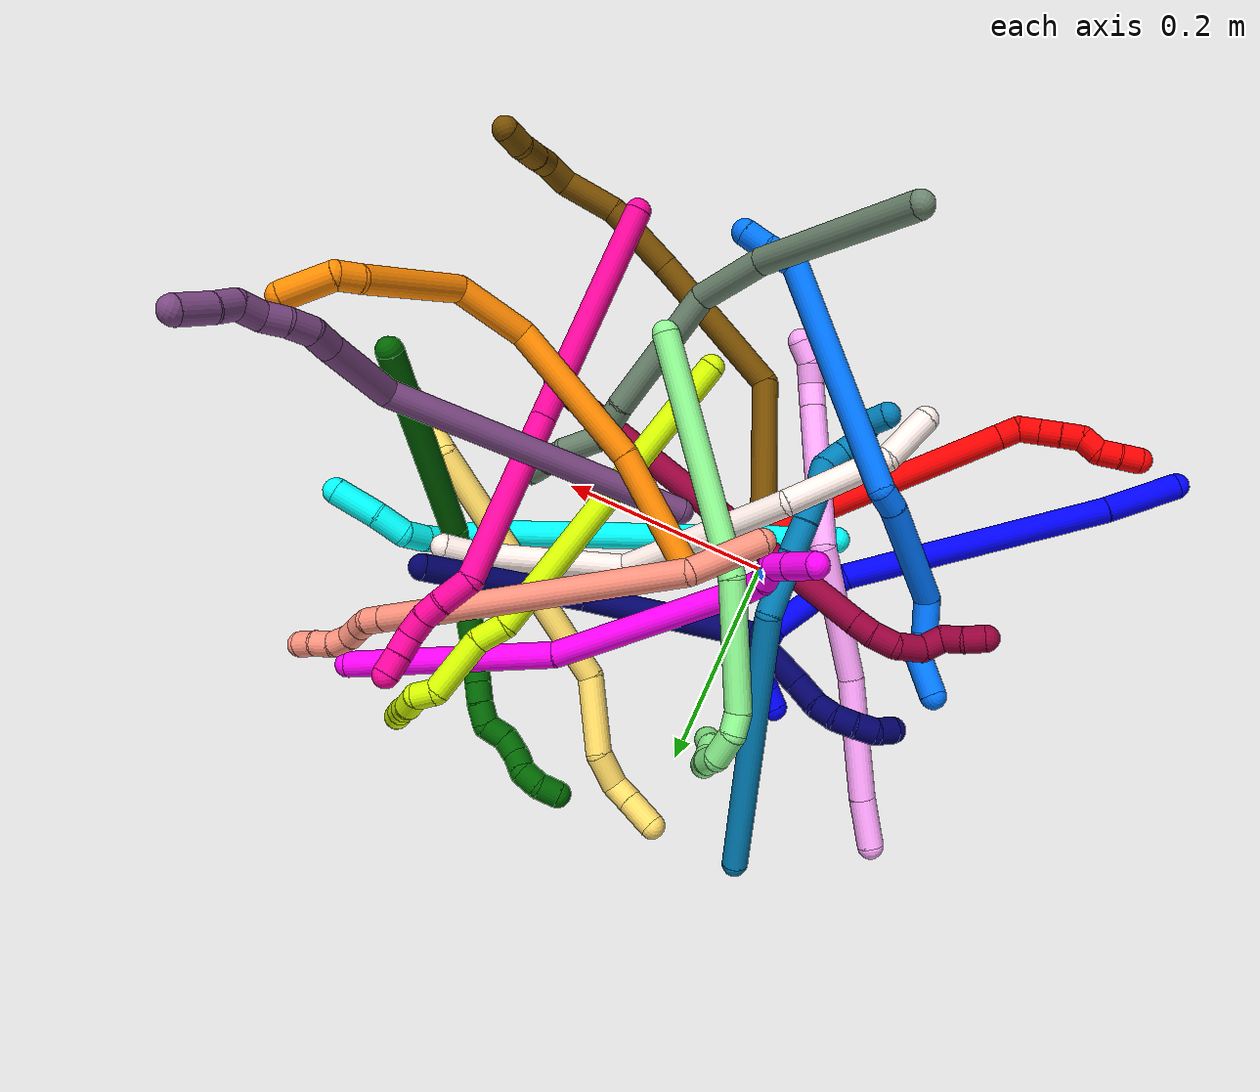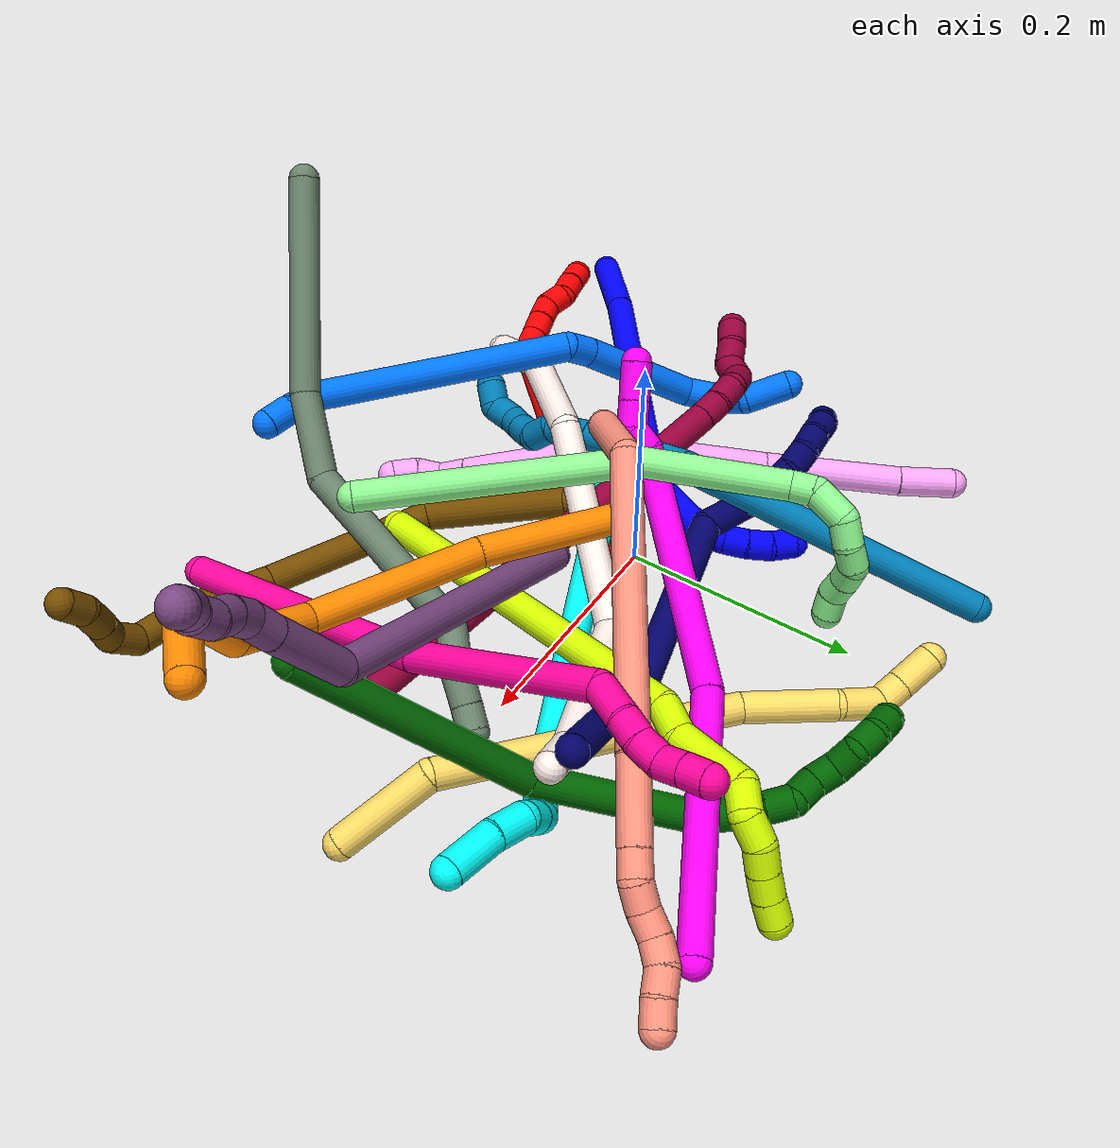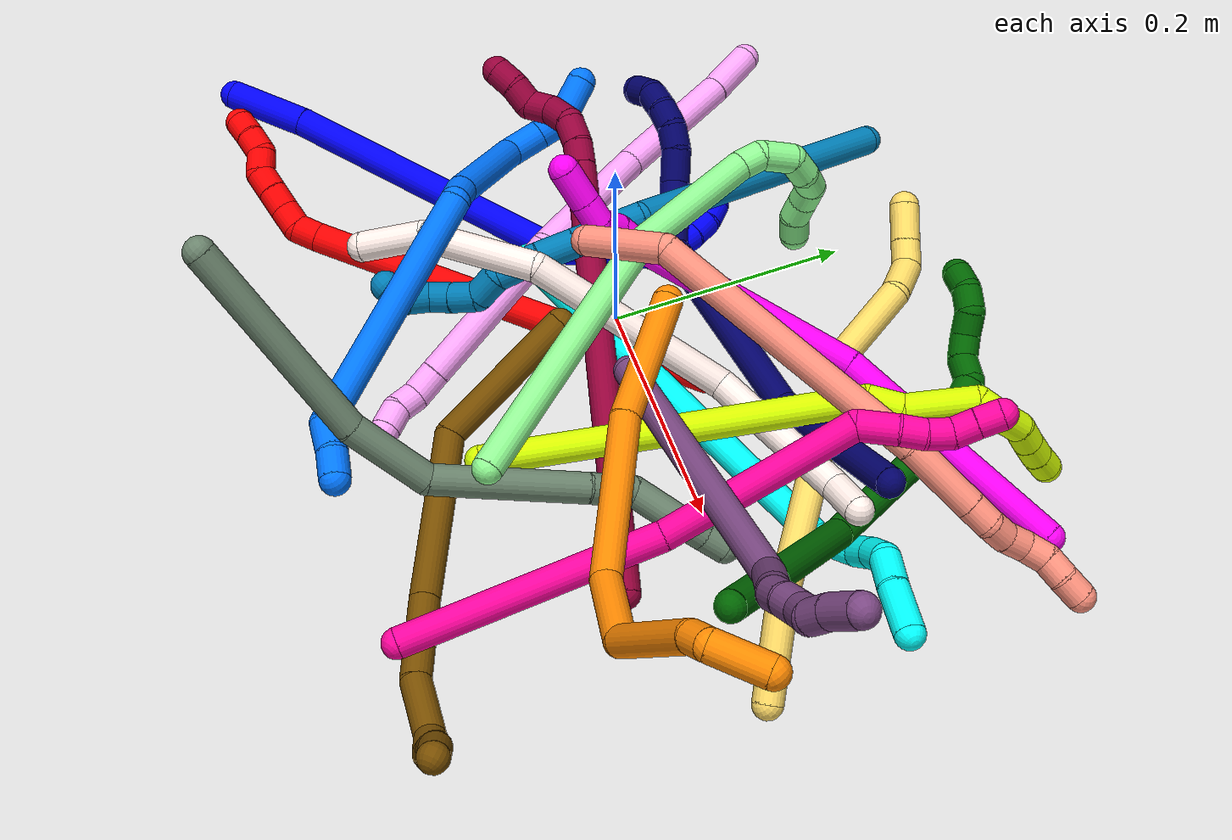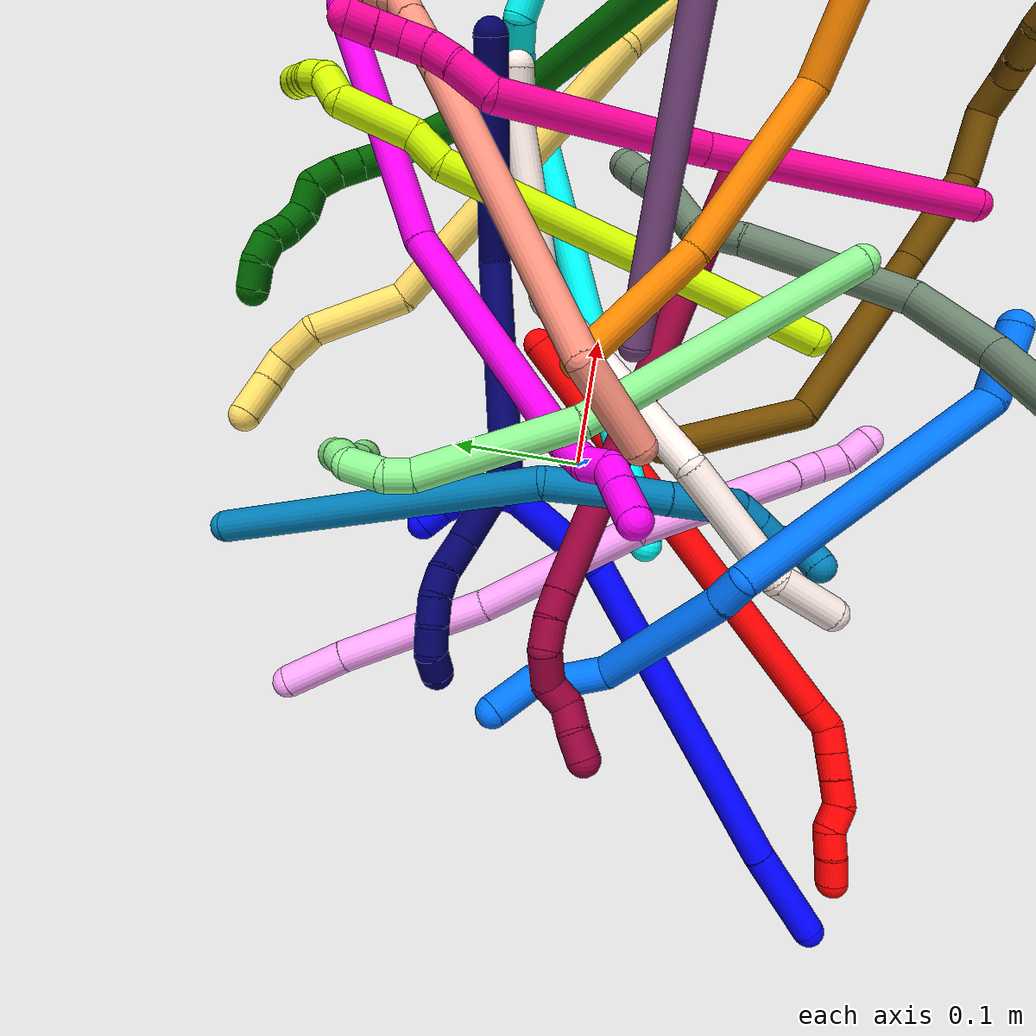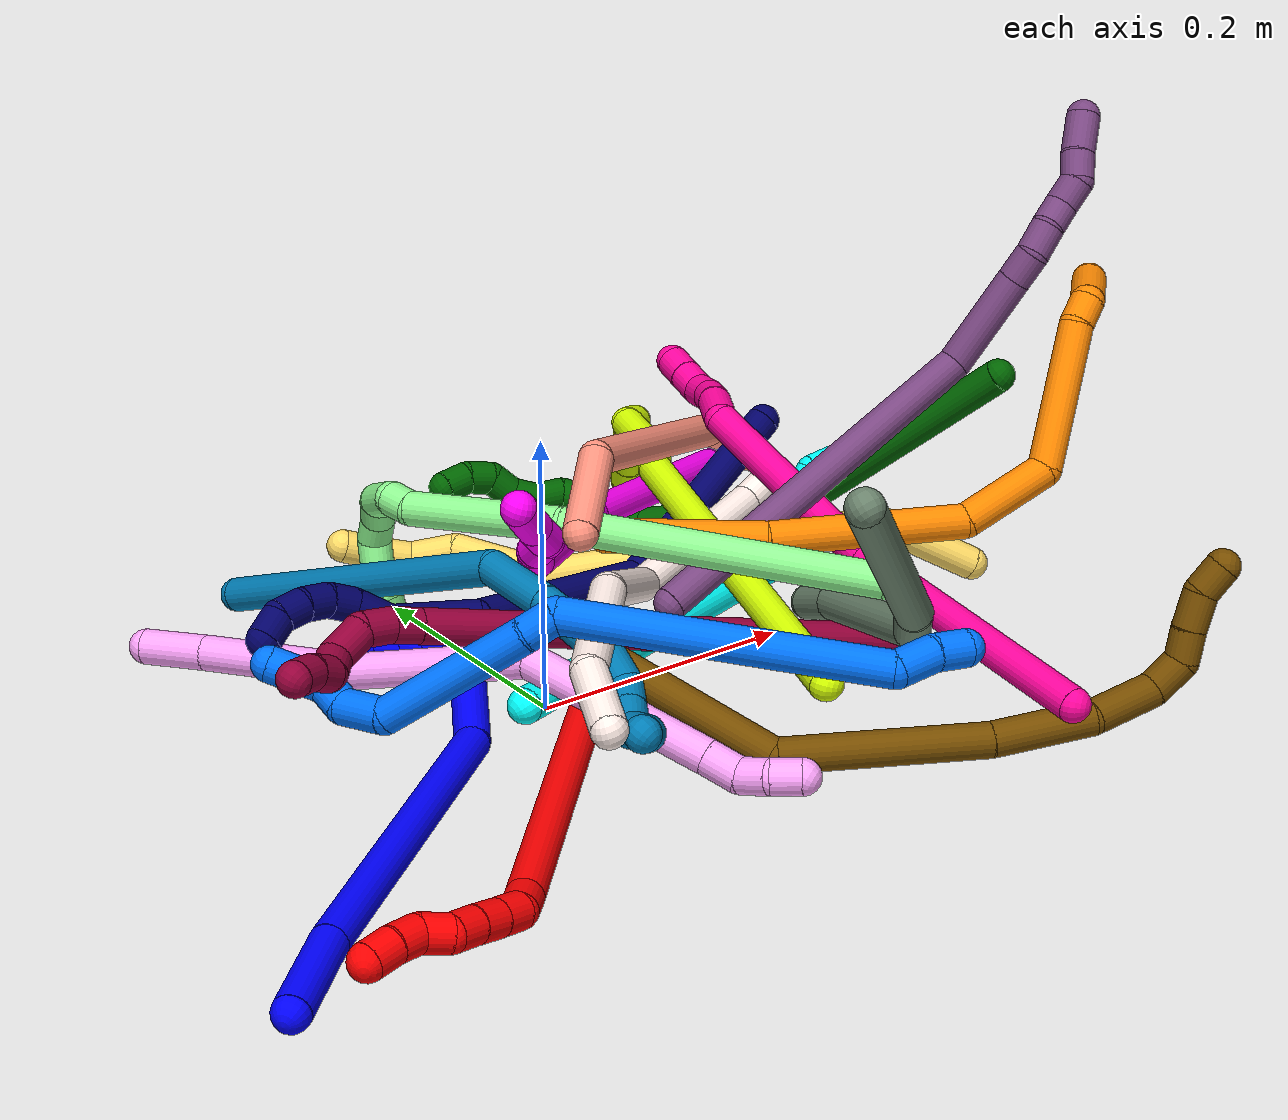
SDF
<sdf version="1.7">
 <world name="default">
  <plugin name="TubeGeneratorPlugin" filename="libtube_generator_plugin.so"/>
  <model name="photoneo_s_sensor">
   <static>1</static>
   <pose>0 0 2 1.57079 1.57079 3.14159</pose>
   <link name="link">
    <inertial><mass>0.1</mass></inertial>
    <sensor name="sensor" type="depth">
     <update_rate>30</update_rate>
     <camera>
      <horizontal_fov>1.22</horizontal_fov>
      <image><width>1920</width><height>1200</height><format>B8G8R8</format></image>
      <clip><near>0.1</near><far>4</far></clip>
      <depth_camera><output>points</output></depth_camera>
     </camera>
     <plugin name="camera_plugin" filename="libgazebo_ros_depth_camera.so">
      <baseline>0.2</baseline>
      <alwaysOn>1</alwaysOn>
      <updateRate>0.0</updateRate>
      <cameraName>camera_ir</cameraName>
      <imageTopicName>/camera/color/image_raw</imageTopicName>
      <cameraInfoTopicName>/camera/color/camera_info</cameraInfoTopicName>
      <depthImageTopicName>/camera/depth/image_raw</depthImageTopicName>
      <depthImageCameraInfoTopicName>/camera/depth/camera_info</depthImageCameraInfoTopicName>
      <pointCloudTopicName>/camera/depth/points</pointCloudTopicName>
      <frameName>fr_optical</frameName>
      <pointCloudCutoff>0.1</pointCloudCutoff>
      <pointCloudCutoffMax>2.0</pointCloudCutoffMax>
      <distortionK1>0</distortionK1>
      <distortionK2>0</distortionK2>
      <distortionK3>0</distortionK3>
      <distortionT1>0</distortionT1>
      <distortionT2>0</distortionT2>
      <CxPrime>0</CxPrime>
      <Cx>0</Cx>
      <Cy>0</Cy>
      <focalLength>0</focalLength>
      <hackBaseline>0</hackBaseline>
     </plugin>
    </sensor>
   </link>
  </model>
  <gravity>0 0 -9.8</gravity>
  <magnetic_field>6e-06 2.3e-05 -4.2e-05</magnetic_field>
  <atmosphere type="adiabatic"/>
  <physics name="default_physics" default="0" type="ode">
   <max_step_size>0.003</max_step_size>
   <real_time_factor>1</real_time_factor>
   <real_time_update_rate>1000</real_time_update_rate>
   <max_contacts>10000</max_contacts>
   <ode>
    <solver>
     <type>quick</type>
     <iters>100</iters>
     <sor>1.3</sor>
     <use_dynamic_moi_rescaling>0</use_dynamic_moi_rescaling>
    </solver>
    <constraints>
     <contact_max_correcting_vel>0</contact_max_correcting_vel>
     <contact_surface_layer>0.001</contact_surface_layer>
     <cfm>0</cfm>
     <erp>0.2</erp>
    </constraints>
   </ode>
  </physics>
  <scene><ambient>0.4 0.4 0.4 1</ambient><background>0.7 0.7 0.7 1</background><shadows>0</shadows></scene>
  <audio><device>default</device></audio>
  <spherical_coordinates>
   <surface_model>EARTH_WGS84</surface_model>
   <latitude_deg>0</latitude_deg>
   <longitude_deg>0</longitude_deg>
   <elevation>0</elevation>
   <heading_deg>0</heading_deg>
  </spherical_coordinates>
  <model name="bin">
   <static>1</static>
   <link name="bottom">
    <collision name="collision-bottom">
     <pose>0 0 -0.01 0 -0 0</pose>
     <geometry><box><size>0.8 0.6 0.02</size></box></geometry>
     <surface>
      <friction><ode><mu>100</mu><mu2>100</mu2></ode></friction>
      <contact><collide_bitmask>65535</collide_bitmask></contact>
     </surface>
    </collision>
   </link>
   <link name="west_wall">
    <collision name="collision-west_wall">
     <pose>-0.41 0 0.1 0 -0 0</pose>
     <geometry><box><size>0.02 0.6 0.2</size></box></geometry>
     <surface>
      <friction><ode><mu>100</mu><mu2>100</mu2></ode></friction>
      <contact><collide_bitmask>65535</collide_bitmask></contact>
     </surface>
    </collision>
   </link>
   <link name="east_wall">
    <collision name="collision-east_wall">
     <pose>0.41 0 0.1 0 -0 0</pose>
     <geometry><box><size>0.02 0.6 0.2</size></box></geometry>
     <surface>
      <friction><ode><mu>100</mu><mu2>100</mu2></ode></friction>
      <contact><collide_bitmask>65535</collide_bitmask></contact>
     </surface>
    </collision>
   </link>
   <link name="south_wall">
    <collision name="collision-south_wall">
     <pose>0 -0.31 0.1 0 -0 0</pose>
     <geometry><box><size>0.8 0.02 0.2</size></box></geometry>
     <surface>
      <friction><ode><mu>100</mu><mu2>100</mu2></ode></friction>
      <contact><collide_bitmask>65535</collide_bitmask></contact>
     </surface>
    </collision>
   </link>
   <link name="north_wall">
    <collision name="collision-north_wall">
     <pose>0 0.31 0.1 0 -0 0</pose>
     <geometry><box><size>0.8 0.02 0.2</size></box></geometry>
     <surface>
      <friction><ode><mu>100</mu><mu2>100</mu2></ode></friction>
      <contact><collide_bitmask>65535</collide_bitmask></contact>
     </surface>
    </collision>
   </link>
  </model>
  <model name="1">
   <static>0</static>
   <link name="1">
    <collision name="collision-cylinder-e_1_1_4">
     <pose>0.001435 0.006426 -0.035388 -2.96195 0.039873 -0.43575</pose>
     <geometry><cylinder><radius>0.0125</radius><length>0.07199</length></cylinder></geometry>
     <surface>
      <friction><ode><mu>1.16</mu><mu2>1.16</mu2><slip1>0</slip1><slip2>0</slip2></ode></friction>
      <contact><ode><kp>1e+06</kp><kd>1</kd><max_vel>0</max_vel><min_depth>0.001</min_depth></ode></contact>
     </surface>
    </collision>
    <visual name="visual-cylinder-e_1_1_4">
     <pose>0.001435 0.006426 -0.035388 -2.96195 0.039873 -0.43575</pose>
     <geometry><cylinder><radius>0.0125</radius><length>0.07199</length></cylinder></geometry>
     <material><ambient>0 0 1 1</ambient></material>
    </visual>
    <collision name="collision-cylinder-e_2_4_5">
     <pose>-0.002937 0.037322 -0.198801 -2.95274 -0.044517 0.46175</pose>
     <geometry><cylinder><radius>0.0125</radius><length>0.260944</length></cylinder></geometry>
     <surface>
      <friction><ode><mu>1.16</mu><mu2>1.16</mu2><slip1>0</slip1><slip2>0</slip2></ode></friction>
      <contact><ode><kp>1e+06</kp><kd>1</kd><max_vel>0</max_vel><min_depth>0.001</min_depth></ode></contact>
     </surface>
    </collision>
    <visual name="visual-cylinder-e_2_4_5">
     <pose>-0.002937 0.037322 -0.198801 -2.95274 -0.044517 0.46175</pose>
     <geometry><cylinder><radius>0.0125</radius><length>0.260944</length></cylinder></geometry>
     <material><ambient>0 0 1 1</ambient></material>
    </visual>
    <collision name="collision-cylinder-e_3_5_6">
     <pose>0.006308 0.068455 -0.366462 -2.97501 0.358316 -2.27769</pose>
     <geometry><cylinder><radius>0.0125</radius><length>0.085836</length></cylinder></geometry>
     <surface>
      <friction><ode><mu>1.16</mu><mu2>1.16</mu2><slip1>0</slip1><slip2>0</slip2></ode></friction>
      <contact><ode><kp>1e+06</kp><kd>1</kd><max_vel>0</max_vel><min_depth>0.001</min_depth></ode></contact>
     </surface>
    </collision>
    <visual name="visual-cylinder-e_3_5_6">
     <pose>0.006308 0.068455 -0.366462 -2.97501 0.358316 -2.27769</pose>
     <geometry><cylinder><radius>0.0125</radius><length>0.085836</length></cylinder></geometry>
     <material><ambient>0 0 1 1</ambient></material>
    </visual>
    <collision name="collision-cylinder-e_4_6_7">
     <pose>0.028628 0.077443 -0.413286 -2.82904 0.766112 -2.39613</pose>
     <geometry><cylinder><radius>0.0125</radius><length>0.020967</length></cylinder></geometry>
     <surface>
      <friction><ode><mu>1.16</mu><mu2>1.16</mu2><slip1>0</slip1><slip2>0</slip2></ode></friction>
      <contact><ode><kp>1e+06</kp><kd>1</kd><max_vel>0</max_vel><min_depth>0.001</min_depth></ode></contact>
     </surface>
    </collision>
    <visual name="visual-cylinder-e_4_6_7">
     <pose>0.028628 0.077443 -0.413286 -2.82904 0.766112 -2.39613</pose>
     <geometry><cylinder><radius>0.0125</radius><length>0.020967</length></cylinder></geometry>
     <material><ambient>0 0 1 1</ambient></material>
    </visual>
    <collision name="collision-cylinder-e_5_7_8">
     <pose>0.044106 0.085349 -0.422339 -1.89303 0.948767 -1.23853</pose>
     <geometry><cylinder><radius>0.0125</radius><length>0.020203</length></cylinder></geometry>
     <surface>
      <friction><ode><mu>1.16</mu><mu2>1.16</mu2><slip1>0</slip1><slip2>0</slip2></ode></friction>
      <contact><ode><kp>1e+06</kp><kd>1</kd><max_vel>0</max_vel><min_depth>0.001</min_depth></ode></contact>
     </surface>
    </collision>
    <visual name="visual-cylinder-e_5_7_8">
     <pose>0.044106 0.085349 -0.422339 -1.89303 0.948767 -1.23853</pose>
     <geometry><cylinder><radius>0.0125</radius><length>0.020203</length></cylinder></geometry>
     <material><ambient>0 0 1 1</ambient></material>
    </visual>
    <collision name="collision-cylinder-e_6_8_9">
     <pose>0.060987 0.095904 -0.424872 -1.7046 1.04627 -1.16614</pose>
     <geometry><cylinder><radius>0.0125</radius><length>0.020036</length></cylinder></geometry>
     <surface>
      <friction><ode><mu>1.16</mu><mu2>1.16</mu2><slip1>0</slip1><slip2>0</slip2></ode></friction>
      <contact><ode><kp>1e+06</kp><kd>1</kd><max_vel>0</max_vel><min_depth>0.001</min_depth></ode></contact>
     </surface>
    </collision>
    <visual name="visual-cylinder-e_6_8_9">
     <pose>0.060987 0.095904 -0.424872 -1.7046 1.04627 -1.16614</pose>
     <geometry><cylinder><radius>0.0125</radius><length>0.020036</length></cylinder></geometry>
     <material><ambient>0 0 1 1</ambient></material>
    </visual>
    <collision name="collision-cylinder-e_7_9_2">
     <pose>0.078496 0.105126 -0.423524 -1.12752 1.08167 -0.725732</pose>
     <geometry><cylinder><radius>0.0125</radius><length>0.020024</length></cylinder></geometry>
     <surface>
      <friction><ode><mu>1.16</mu><mu2>1.16</mu2><slip1>0</slip1><slip2>0</slip2></ode></friction>
      <contact><ode><kp>1e+06</kp><kd>1</kd><max_vel>0</max_vel><min_depth>0.001</min_depth></ode></contact>
     </surface>
    </collision>
    <visual name="visual-cylinder-e_7_9_2">
     <pose>0.078496 0.105126 -0.423524 -1.12752 1.08167 -0.725732</pose>
     <geometry><cylinder><radius>0.0125</radius><length>0.020024</length></cylinder></geometry>
     <material><ambient>0 0 1 1</ambient></material>
    </visual>
    <collision name="collision-sphere-2">
     <pose>0.087334 0.109375 -0.421507 0 -0 0</pose>
     <geometry><sphere><radius>0.0125</radius></sphere></geometry>
     <surface>
      <friction><ode><mu>1.16</mu><mu2>1.16</mu2><slip1>0</slip1><slip2>0</slip2></ode></friction>
      <contact><ode><kp>1e+06</kp><kd>1</kd><max_vel>0</max_vel><min_depth>0.001</min_depth></ode></contact>
     </surface>
    </collision>
    <visual name="visual-sphere-2">
     <pose>0.087334 0.109375 -0.421507 0 -0 0</pose>
     <geometry><sphere><radius>0.0125</radius></sphere></geometry>
     <material><ambient>0 0 1 1</ambient></material>
    </visual>
    <collision name="collision-sphere-9">
     <pose>0.069658 0.100876 -0.425542 0 -0 0</pose>
     <geometry><sphere><radius>0.0125</radius></sphere></geometry>
     <surface>
      <friction><ode><mu>1.16</mu><mu2>1.16</mu2><slip1>0</slip1><slip2>0</slip2></ode></friction>
      <contact><ode><kp>1e+06</kp><kd>1</kd><max_vel>0</max_vel><min_depth>0.001</min_depth></ode></contact>
     </surface>
    </collision>
    <visual name="visual-sphere-9">
     <pose>0.069658 0.100876 -0.425542 0 -0 0</pose>
     <geometry><sphere><radius>0.0125</radius></sphere></geometry>
     <material><ambient>0 0 1 1</ambient></material>
    </visual>
    <collision name="collision-sphere-4">
     <pose>0.00287 0.012853 -0.070775 0 -0 0</pose>
     <geometry><sphere><radius>0.0125</radius></sphere></geometry>
     <surface>
      <friction><ode><mu>1.16</mu><mu2>1.16</mu2><slip1>0</slip1><slip2>0</slip2></ode></friction>
      <contact><ode><kp>1e+06</kp><kd>1</kd><max_vel>0</max_vel><min_depth>0.001</min_depth></ode></contact>
     </surface>
    </collision>
    <visual name="visual-sphere-4">
     <pose>0.00287 0.012853 -0.070775 0 -0 0</pose>
     <geometry><sphere><radius>0.0125</radius></sphere></geometry>
     <material><ambient>0 0 1 1</ambient></material>
    </visual>
    <collision name="collision-sphere-1">
     <geometry><sphere><radius>0.0125</radius></sphere></geometry>
     <surface>
      <friction><ode><mu>1.16</mu><mu2>1.16</mu2><slip1>0</slip1><slip2>0</slip2></ode></friction>
      <contact><ode><kp>1e+06</kp><kd>1</kd><max_vel>0</max_vel><min_depth>0.001</min_depth></ode></contact>
     </surface>
    </collision>
    <visual name="visual-sphere-1">
     <geometry><sphere><radius>0.0125</radius></sphere></geometry>
     <material><ambient>0 0 1 1</ambient></material>
    </visual>
    <collision name="collision-sphere-8">
     <pose>0.052316 0.090932 -0.424203 0 -0 0</pose>
     <geometry><sphere><radius>0.0125</radius></sphere></geometry>
     <surface>
      <friction><ode><mu>1.16</mu><mu2>1.16</mu2><slip1>0</slip1><slip2>0</slip2></ode></friction>
      <contact><ode><kp>1e+06</kp><kd>1</kd><max_vel>0</max_vel><min_depth>0.001</min_depth></ode></contact>
     </surface>
    </collision>
    <visual name="visual-sphere-8">
     <pose>0.052316 0.090932 -0.424203 0 -0 0</pose>
     <geometry><sphere><radius>0.0125</radius></sphere></geometry>
     <material><ambient>0 0 1 1</ambient></material>
    </visual>
    <collision name="collision-sphere-5">
     <pose>-0.008743 0.061791 -0.326826 0 -0 0</pose>
     <geometry><sphere><radius>0.0125</radius></sphere></geometry>
     <surface>
      <friction><ode><mu>1.16</mu><mu2>1.16</mu2><slip1>0</slip1><slip2>0</slip2></ode></friction>
      <contact><ode><kp>1e+06</kp><kd>1</kd><max_vel>0</max_vel><min_depth>0.001</min_depth></ode></contact>
     </surface>
    </collision>
    <visual name="visual-sphere-5">
     <pose>-0.008743 0.061791 -0.326826 0 -0 0</pose>
     <geometry><sphere><radius>0.0125</radius></sphere></geometry>
     <material><ambient>0 0 1 1</ambient></material>
    </visual>
    <collision name="collision-sphere-6">
     <pose>0.021359 0.07512 -0.406098 0 -0 0</pose>
     <geometry><sphere><radius>0.0125</radius></sphere></geometry>
     <surface>
      <friction><ode><mu>1.16</mu><mu2>1.16</mu2><slip1>0</slip1><slip2>0</slip2></ode></friction>
      <contact><ode><kp>1e+06</kp><kd>1</kd><max_vel>0</max_vel><min_depth>0.001</min_depth></ode></contact>
     </surface>
    </collision>
    <visual name="visual-sphere-6">
     <pose>0.021359 0.07512 -0.406098 0 -0 0</pose>
     <geometry><sphere><radius>0.0125</radius></sphere></geometry>
     <material><ambient>0 0 1 1</ambient></material>
    </visual>
    <collision name="collision-sphere-7">
     <pose>0.035897 0.079766 -0.420475 0 -0 0</pose>
     <geometry><sphere><radius>0.0125</radius></sphere></geometry>
     <surface>
      <friction><ode><mu>1.16</mu><mu2>1.16</mu2><slip1>0</slip1><slip2>0</slip2></ode></friction>
      <contact><ode><kp>1e+06</kp><kd>1</kd><max_vel>0</max_vel><min_depth>0.001</min_depth></ode></contact>
     </surface>
    </collision>
    <visual name="visual-sphere-7">
     <pose>0.035897 0.079766 -0.420475 0 -0 0</pose>
     <geometry><sphere><radius>0.0125</radius></sphere></geometry>
     <material><ambient>0 0 1 1</ambient></material>
    </visual>
    <inertial>
     <pose>0.008327 0.046904 -0.240141 0 -0 0</pose>
     <mass>0.5</mass>
     <inertia>
      <ixx>0.001944</ixx>
      <ixy>0</ixy>
      <ixz>0</ixz>
      <iyy>-0.000677</iyy>
      <iyz>0</iyz>
      <izz>-0.000289</izz>
     </inertia>
    </inertial>
   </link>
   <pose>-0.335368 -0.239201 0.011723 -1.76735 -0.413409 2.2858</pose>
  </model>
  <model name="2">
   <static>0</static>
   <link name="2">
    <collision name="collision-cylinder-e_1_1_4">
     <pose>-0.006723 -0.006391 0.179255 0.035641 -0.037463 -0.000668</pose>
     <geometry><cylinder><radius>0.0125</radius><length>0.358989</length></cylinder></geometry>
     <surface>
      <friction><ode><mu>1.16</mu><mu2>1.16</mu2><slip1>0</slip1><slip2>0</slip2></ode></friction>
      <contact><ode><kp>1e+06</kp><kd>1</kd><max_vel>0</max_vel><min_depth>0.001</min_depth></ode></contact>
     </surface>
    </collision>
    <visual name="visual-cylinder-e_1_1_4">
     <pose>-0.006723 -0.006391 0.179255 0.035641 -0.037463 -0.000668</pose>
     <geometry><cylinder><radius>0.0125</radius><length>0.358989</length></cylinder></geometry>
     <material><ambient>1 0 0 1</ambient></material>
    </visual>
    <collision name="collision-cylinder-e_2_4_5">
     <pose>-0.015063 -0.012864 0.368669 0.007967 -0.157913 -0.00063</pose>
     <geometry><cylinder><radius>0.0125</radius><length>0.020577</length></cylinder></geometry>
     <surface>
      <friction><ode><mu>1.16</mu><mu2>1.16</mu2><slip1>0</slip1><slip2>0</slip2></ode></friction>
      <contact><ode><kp>1e+06</kp><kd>1</kd><max_vel>0</max_vel><min_depth>0.001</min_depth></ode></contact>
     </surface>
    </collision>
    <visual name="visual-cylinder-e_2_4_5">
     <pose>-0.015063 -0.012864 0.368669 0.007967 -0.157913 -0.00063</pose>
     <geometry><cylinder><radius>0.0125</radius><length>0.020577</length></cylinder></geometry>
     <material><ambient>1 0 0 1</ambient></material>
    </visual>
    <collision name="collision-cylinder-e_3_5_6">
     <pose>-0.019873 -0.017906 0.386927 0.549661 -0.324202 -0.092158</pose>
     <geometry><cylinder><radius>0.0125</radius><length>0.020036</length></cylinder></geometry>
     <surface>
      <friction><ode><mu>1.16</mu><mu2>1.16</mu2><slip1>0</slip1><slip2>0</slip2></ode></friction>
      <contact><ode><kp>1e+06</kp><kd>1</kd><max_vel>0</max_vel><min_depth>0.001</min_depth></ode></contact>
     </surface>
    </collision>
    <visual name="visual-cylinder-e_3_5_6">
     <pose>-0.019873 -0.017906 0.386927 0.549661 -0.324202 -0.092158</pose>
     <geometry><cylinder><radius>0.0125</radius><length>0.020036</length></cylinder></geometry>
     <material><ambient>1 0 0 1</ambient></material>
    </visual>
    <collision name="collision-cylinder-e_4_6_7">
     <pose>-0.026626 -0.027901 0.403121 0.556305 -0.35753 -0.103105</pose>
     <geometry><cylinder><radius>0.0125</radius><length>0.020355</length></cylinder></geometry>
     <surface>
      <friction><ode><mu>1.16</mu><mu2>1.16</mu2><slip1>0</slip1><slip2>0</slip2></ode></friction>
      <contact><ode><kp>1e+06</kp><kd>1</kd><max_vel>0</max_vel><min_depth>0.001</min_depth></ode></contact>
     </surface>
    </collision>
    <visual name="visual-cylinder-e_4_6_7">
     <pose>-0.026626 -0.027901 0.403121 0.556305 -0.35753 -0.103105</pose>
     <geometry><cylinder><radius>0.0125</radius><length>0.020355</length></cylinder></geometry>
     <material><ambient>1 0 0 1</ambient></material>
    </visual>
    <collision name="collision-cylinder-e_5_7_8">
     <pose>-0.033214 -0.038044 0.419276 0.565014 -0.307133 -0.089799</pose>
     <geometry><cylinder><radius>0.0125</radius><length>0.02002</length></cylinder></geometry>
     <surface>
      <friction><ode><mu>1.16</mu><mu2>1.16</mu2><slip1>0</slip1><slip2>0</slip2></ode></friction>
      <contact><ode><kp>1e+06</kp><kd>1</kd><max_vel>0</max_vel><min_depth>0.001</min_depth></ode></contact>
     </surface>
    </collision>
    <visual name="visual-cylinder-e_5_7_8">
     <pose>-0.033214 -0.038044 0.419276 0.565014 -0.307133 -0.089799</pose>
     <geometry><cylinder><radius>0.0125</radius><length>0.02002</length></cylinder></geometry>
     <material><ambient>1 0 0 1</ambient></material>
    </visual>
    <collision name="collision-cylinder-e_6_8_9">
     <pose>-0.039876 -0.051731 0.430984 1.16855 -0.371834 -0.247494</pose>
     <geometry><cylinder><radius>0.0125</radius><length>0.020012</length></cylinder></geometry>
     <surface>
      <friction><ode><mu>1.16</mu><mu2>1.16</mu2><slip1>0</slip1><slip2>0</slip2></ode></friction>
      <contact><ode><kp>1e+06</kp><kd>1</kd><max_vel>0</max_vel><min_depth>0.001</min_depth></ode></contact>
     </surface>
    </collision>
    <visual name="visual-cylinder-e_6_8_9">
     <pose>-0.039876 -0.051731 0.430984 1.16855 -0.371834 -0.247494</pose>
     <geometry><cylinder><radius>0.0125</radius><length>0.020012</length></cylinder></geometry>
     <material><ambient>1 0 0 1</ambient></material>
    </visual>
    <collision name="collision-cylinder-e_7_9_10">
     <pose>-0.045433 -0.066053 0.442594 0.624996 -0.193368 -0.062649</pose>
     <geometry><cylinder><radius>0.0125</radius><length>0.020004</length></cylinder></geometry>
     <surface>
      <friction><ode><mu>1.16</mu><mu2>1.16</mu2><slip1>0</slip1><slip2>0</slip2></ode></friction>
      <contact><ode><kp>1e+06</kp><kd>1</kd><max_vel>0</max_vel><min_depth>0.001</min_depth></ode></contact>
     </surface>
    </collision>
    <visual name="visual-cylinder-e_7_9_10">
     <pose>-0.045433 -0.066053 0.442594 0.624996 -0.193368 -0.062649</pose>
     <geometry><cylinder><radius>0.0125</radius><length>0.020004</length></cylinder></geometry>
     <material><ambient>1 0 0 1</ambient></material>
    </visual>
    <collision name="collision-cylinder-e_8_10_2">
     <pose>-0.047848 -0.077702 0.458612 0.632527 -0.04931 -0.01614</pose>
     <geometry><cylinder><radius>0.0125</radius><length>0.020006</length></cylinder></geometry>
     <surface>
      <friction><ode><mu>1.16</mu><mu2>1.16</mu2><slip1>0</slip1><slip2>0</slip2></ode></friction>
      <contact><ode><kp>1e+06</kp><kd>1</kd><max_vel>0</max_vel><min_depth>0.001</min_depth></ode></contact>
     </surface>
    </collision>
    <visual name="visual-cylinder-e_8_10_2">
     <pose>-0.047848 -0.077702 0.458612 0.632527 -0.04931 -0.01614</pose>
     <geometry><cylinder><radius>0.0125</radius><length>0.020006</length></cylinder></geometry>
     <material><ambient>1 0 0 1</ambient></material>
    </visual>
    <collision name="collision-sphere-2">
     <pose>-0.048341 -0.083609 0.46667 0 -0 0</pose>
     <geometry><sphere><radius>0.0125</radius></sphere></geometry>
     <surface>
      <friction><ode><mu>1.16</mu><mu2>1.16</mu2><slip1>0</slip1><slip2>0</slip2></ode></friction>
      <contact><ode><kp>1e+06</kp><kd>1</kd><max_vel>0</max_vel><min_depth>0.001</min_depth></ode></contact>
     </surface>
    </collision>
    <visual name="visual-sphere-2">
     <pose>-0.048341 -0.083609 0.46667 0 -0 0</pose>
     <geometry><sphere><radius>0.0125</radius></sphere></geometry>
     <material><ambient>1 0 0 1</ambient></material>
    </visual>
    <collision name="collision-sphere-10">
     <pose>-0.047355 -0.071796 0.450554 0 -0 0</pose>
     <geometry><sphere><radius>0.0125</radius></sphere></geometry>
     <surface>
      <friction><ode><mu>1.16</mu><mu2>1.16</mu2><slip1>0</slip1><slip2>0</slip2></ode></friction>
      <contact><ode><kp>1e+06</kp><kd>1</kd><max_vel>0</max_vel><min_depth>0.001</min_depth></ode></contact>
     </surface>
    </collision>
    <visual name="visual-sphere-10">
     <pose>-0.047355 -0.071796 0.450554 0 -0 0</pose>
     <geometry><sphere><radius>0.0125</radius></sphere></geometry>
     <material><ambient>1 0 0 1</ambient></material>
    </visual>
    <collision name="collision-sphere-9">
     <pose>-0.043511 -0.060309 0.434634 0 -0 0</pose>
     <geometry><sphere><radius>0.0125</radius></sphere></geometry>
     <surface>
      <friction><ode><mu>1.16</mu><mu2>1.16</mu2><slip1>0</slip1><slip2>0</slip2></ode></friction>
      <contact><ode><kp>1e+06</kp><kd>1</kd><max_vel>0</max_vel><min_depth>0.001</min_depth></ode></contact>
     </surface>
    </collision>
    <visual name="visual-sphere-9">
     <pose>-0.043511 -0.060309 0.434634 0 -0 0</pose>
     <geometry><sphere><radius>0.0125</radius></sphere></geometry>
     <material><ambient>1 0 0 1</ambient></material>
    </visual>
    <collision name="collision-sphere-4">
     <pose>-0.013445 -0.012783 0.358509 0 -0 0</pose>
     <geometry><sphere><radius>0.0125</radius></sphere></geometry>
     <surface>
      <friction><ode><mu>1.16</mu><mu2>1.16</mu2><slip1>0</slip1><slip2>0</slip2></ode></friction>
      <contact><ode><kp>1e+06</kp><kd>1</kd><max_vel>0</max_vel><min_depth>0.001</min_depth></ode></contact>
     </surface>
    </collision>
    <visual name="visual-sphere-4">
     <pose>-0.013445 -0.012783 0.358509 0 -0 0</pose>
     <geometry><sphere><radius>0.0125</radius></sphere></geometry>
     <material><ambient>1 0 0 1</ambient></material>
    </visual>
    <collision name="collision-sphere-1">
     <geometry><sphere><radius>0.0125</radius></sphere></geometry>
     <surface>
      <friction><ode><mu>1.16</mu><mu2>1.16</mu2><slip1>0</slip1><slip2>0</slip2></ode></friction>
      <contact><ode><kp>1e+06</kp><kd>1</kd><max_vel>0</max_vel><min_depth>0.001</min_depth></ode></contact>
     </surface>
    </collision>
    <visual name="visual-sphere-1">
     <geometry><sphere><radius>0.0125</radius></sphere></geometry>
     <material><ambient>1 0 0 1</ambient></material>
    </visual>
    <collision name="collision-sphere-8">
     <pose>-0.03624 -0.043153 0.427335 0 -0 0</pose>
     <geometry><sphere><radius>0.0125</radius></sphere></geometry>
     <surface>
      <friction><ode><mu>1.16</mu><mu2>1.16</mu2><slip1>0</slip1><slip2>0</slip2></ode></friction>
      <contact><ode><kp>1e+06</kp><kd>1</kd><max_vel>0</max_vel><min_depth>0.001</min_depth></ode></contact>
     </surface>
    </collision>
    <visual name="visual-sphere-8">
     <pose>-0.03624 -0.043153 0.427335 0 -0 0</pose>
     <geometry><sphere><radius>0.0125</radius></sphere></geometry>
     <material><ambient>1 0 0 1</ambient></material>
    </visual>
    <collision name="collision-sphere-5">
     <pose>-0.016681 -0.012945 0.378829 0 -0 0</pose>
     <geometry><sphere><radius>0.0125</radius></sphere></geometry>
     <surface>
      <friction><ode><mu>1.16</mu><mu2>1.16</mu2><slip1>0</slip1><slip2>0</slip2></ode></friction>
      <contact><ode><kp>1e+06</kp><kd>1</kd><max_vel>0</max_vel><min_depth>0.001</min_depth></ode></contact>
     </surface>
    </collision>
    <visual name="visual-sphere-5">
     <pose>-0.016681 -0.012945 0.378829 0 -0 0</pose>
     <geometry><sphere><radius>0.0125</radius></sphere></geometry>
     <material><ambient>1 0 0 1</ambient></material>
    </visual>
    <collision name="collision-sphere-6">
     <pose>-0.023064 -0.022866 0.395024 0 -0 0</pose>
     <geometry><sphere><radius>0.0125</radius></sphere></geometry>
     <surface>
      <friction><ode><mu>1.16</mu><mu2>1.16</mu2><slip1>0</slip1><slip2>0</slip2></ode></friction>
      <contact><ode><kp>1e+06</kp><kd>1</kd><max_vel>0</max_vel><min_depth>0.001</min_depth></ode></contact>
     </surface>
    </collision>
    <visual name="visual-sphere-6">
     <pose>-0.023064 -0.022866 0.395024 0 -0 0</pose>
     <geometry><sphere><radius>0.0125</radius></sphere></geometry>
     <material><ambient>1 0 0 1</ambient></material>
    </visual>
    <collision name="collision-sphere-7">
     <pose>-0.030187 -0.032935 0.411217 0 -0 0</pose>
     <geometry><sphere><radius>0.0125</radius></sphere></geometry>
     <surface>
      <friction><ode><mu>1.16</mu><mu2>1.16</mu2><slip1>0</slip1><slip2>0</slip2></ode></friction>
      <contact><ode><kp>1e+06</kp><kd>1</kd><max_vel>0</max_vel><min_depth>0.001</min_depth></ode></contact>
     </surface>
    </collision>
    <visual name="visual-sphere-7">
     <pose>-0.030187 -0.032935 0.411217 0 -0 0</pose>
     <geometry><sphere><radius>0.0125</radius></sphere></geometry>
     <material><ambient>1 0 0 1</ambient></material>
    </visual>
    <inertial>
     <pose>-0.013985 -0.016317 0.245885 0 -0 0</pose>
     <mass>0.5</mass>
     <inertia>
      <ixx>0.003869</ixx>
      <ixy>0</ixy>
      <ixz>0</ixz>
      <iyy>0.003865</iyy>
      <iyz>0</iyz>
      <izz>0.000327</izz>
     </inertia>
    </inertial>
   </link>
   <pose>0.088803 0.046941 0.011486 1.74738 1.39472 -0.546762</pose>
  </model>
  <model name="3">
   <static>0</static>
   <link name="3">
    <collision name="collision-cylinder-e_1_1_4">
     <pose>0.08779 0.041048 0.138961 -0.287221 0.544733 -0.080735</pose>
     <geometry><cylinder><radius>0.0125</radius><length>0.338835</length></cylinder></geometry>
     <surface>
      <friction><ode><mu>1.16</mu><mu2>1.16</mu2><slip1>0</slip1><slip2>0</slip2></ode></friction>
      <contact><ode><kp>1e+06</kp><kd>1</kd><max_vel>0</max_vel><min_depth>0.001</min_depth></ode></contact>
     </surface>
    </collision>
    <visual name="visual-cylinder-e_1_1_4">
     <pose>0.08779 0.041048 0.138961 -0.287221 0.544733 -0.080735</pose>
     <geometry><cylinder><radius>0.0125</radius><length>0.338835</length></cylinder></geometry>
     <material><ambient>0.003922 1 0.996078 1</ambient></material>
    </visual>
    <collision name="collision-cylinder-e_2_4_5">
     <pose>0.17766 0.092827 0.294052 -0.587089 0.1069 -0.032341</pose>
     <geometry><cylinder><radius>0.0125</radius><length>0.038969</length></cylinder></geometry>
     <surface>
      <friction><ode><mu>1.16</mu><mu2>1.16</mu2><slip1>0</slip1><slip2>0</slip2></ode></friction>
      <contact><ode><kp>1e+06</kp><kd>1</kd><max_vel>0</max_vel><min_depth>0.001</min_depth></ode></contact>
     </surface>
    </collision>
    <visual name="visual-cylinder-e_2_4_5">
     <pose>0.17766 0.092827 0.294052 -0.587089 0.1069 -0.032341</pose>
     <geometry><cylinder><radius>0.0125</radius><length>0.038969</length></cylinder></geometry>
     <material><ambient>0.003922 1 0.996078 1</ambient></material>
    </visual>
    <collision name="collision-cylinder-e_3_5_6">
     <pose>0.174338 0.108961 0.320677 -0.475337 -0.429104 0.105476</pose>
     <geometry><cylinder><radius>0.0125</radius><length>0.025962</length></cylinder></geometry>
     <surface>
      <friction><ode><mu>1.16</mu><mu2>1.16</mu2><slip1>0</slip1><slip2>0</slip2></ode></friction>
      <contact><ode><kp>1e+06</kp><kd>1</kd><max_vel>0</max_vel><min_depth>0.001</min_depth></ode></contact>
     </surface>
    </collision>
    <visual name="visual-cylinder-e_3_5_6">
     <pose>0.174338 0.108961 0.320677 -0.475337 -0.429104 0.105476</pose>
     <geometry><cylinder><radius>0.0125</radius><length>0.025962</length></cylinder></geometry>
     <material><ambient>0.003922 1 0.996078 1</ambient></material>
    </visual>
    <collision name="collision-cylinder-e_4_6_7">
     <pose>0.163821 0.117746 0.341367 -0.320465 -0.444458 0.073006</pose>
     <geometry><cylinder><radius>0.0125</radius><length>0.023794</length></cylinder></geometry>
     <surface>
      <friction><ode><mu>1.16</mu><mu2>1.16</mu2><slip1>0</slip1><slip2>0</slip2></ode></friction>
      <contact><ode><kp>1e+06</kp><kd>1</kd><max_vel>0</max_vel><min_depth>0.001</min_depth></ode></contact>
     </surface>
    </collision>
    <visual name="visual-cylinder-e_4_6_7">
     <pose>0.163821 0.117746 0.341367 -0.320465 -0.444458 0.073006</pose>
     <geometry><cylinder><radius>0.0125</radius><length>0.023794</length></cylinder></geometry>
     <material><ambient>0.003922 1 0.996078 1</ambient></material>
    </visual>
    <collision name="collision-cylinder-e_5_7_8">
     <pose>0.158695 0.118267 0.366193 0.19317 -0.000761 -7.4e-05</pose>
     <geometry><cylinder><radius>0.0125</radius><length>0.029819</length></cylinder></geometry>
     <surface>
      <friction><ode><mu>1.16</mu><mu2>1.16</mu2><slip1>0</slip1><slip2>0</slip2></ode></friction>
      <contact><ode><kp>1e+06</kp><kd>1</kd><max_vel>0</max_vel><min_depth>0.001</min_depth></ode></contact>
     </surface>
    </collision>
    <visual name="visual-cylinder-e_5_7_8">
     <pose>0.158695 0.118267 0.366193 0.19317 -0.000761 -7.4e-05</pose>
     <geometry><cylinder><radius>0.0125</radius><length>0.029819</length></cylinder></geometry>
     <material><ambient>0.003922 1 0.996078 1</ambient></material>
    </visual>
    <collision name="collision-cylinder-e_6_8_2">
     <pose>0.162154 0.111825 0.401544 0.171087 0.163573 0.014058</pose>
     <geometry><cylinder><radius>0.0125</radius><length>0.042621</length></cylinder></geometry>
     <surface>
      <friction><ode><mu>1.16</mu><mu2>1.16</mu2><slip1>0</slip1><slip2>0</slip2></ode></friction>
      <contact><ode><kp>1e+06</kp><kd>1</kd><max_vel>0</max_vel><min_depth>0.001</min_depth></ode></contact>
     </surface>
    </collision>
    <visual name="visual-cylinder-e_6_8_2">
     <pose>0.162154 0.111825 0.401544 0.171087 0.163573 0.014058</pose>
     <geometry><cylinder><radius>0.0125</radius><length>0.042621</length></cylinder></geometry>
     <material><ambient>0.003922 1 0.996078 1</ambient></material>
    </visual>
    <collision name="collision-sphere-2">
     <pose>0.165624 0.108246 0.422263 0 -0 0</pose>
     <geometry><sphere><radius>0.0125</radius></sphere></geometry>
     <surface>
      <friction><ode><mu>1.16</mu><mu2>1.16</mu2><slip1>0</slip1><slip2>0</slip2></ode></friction>
      <contact><ode><kp>1e+06</kp><kd>1</kd><max_vel>0</max_vel><min_depth>0.001</min_depth></ode></contact>
     </surface>
    </collision>
    <visual name="visual-sphere-2">
     <pose>0.165624 0.108246 0.422263 0 -0 0</pose>
     <geometry><sphere><radius>0.0125</radius></sphere></geometry>
     <material><ambient>0.003922 1 0.996078 1</ambient></material>
    </visual>
    <collision name="collision-sphere-4">
     <pose>0.175581 0.082095 0.277922 0 -0 0</pose>
     <geometry><sphere><radius>0.0125</radius></sphere></geometry>
     <surface>
      <friction><ode><mu>1.16</mu><mu2>1.16</mu2><slip1>0</slip1><slip2>0</slip2></ode></friction>
      <contact><ode><kp>1e+06</kp><kd>1</kd><max_vel>0</max_vel><min_depth>0.001</min_depth></ode></contact>
     </surface>
    </collision>
    <visual name="visual-sphere-4">
     <pose>0.175581 0.082095 0.277922 0 -0 0</pose>
     <geometry><sphere><radius>0.0125</radius></sphere></geometry>
     <material><ambient>0.003922 1 0.996078 1</ambient></material>
    </visual>
    <collision name="collision-sphere-1">
     <geometry><sphere><radius>0.0125</radius></sphere></geometry>
     <surface>
      <friction><ode><mu>1.16</mu><mu2>1.16</mu2><slip1>0</slip1><slip2>0</slip2></ode></friction>
      <contact><ode><kp>1e+06</kp><kd>1</kd><max_vel>0</max_vel><min_depth>0.001</min_depth></ode></contact>
     </surface>
    </collision>
    <visual name="visual-sphere-1">
     <geometry><sphere><radius>0.0125</radius></sphere></geometry>
     <material><ambient>0.003922 1 0.996078 1</ambient></material>
    </visual>
    <collision name="collision-sphere-8">
     <pose>0.158683 0.115405 0.380826 0 -0 0</pose>
     <geometry><sphere><radius>0.0125</radius></sphere></geometry>
     <surface>
      <friction><ode><mu>1.16</mu><mu2>1.16</mu2><slip1>0</slip1><slip2>0</slip2></ode></friction>
      <contact><ode><kp>1e+06</kp><kd>1</kd><max_vel>0</max_vel><min_depth>0.001</min_depth></ode></contact>
     </surface>
    </collision>
    <visual name="visual-sphere-8">
     <pose>0.158683 0.115405 0.380826 0 -0 0</pose>
     <geometry><sphere><radius>0.0125</radius></sphere></geometry>
     <material><ambient>0.003922 1 0.996078 1</ambient></material>
    </visual>
    <collision name="collision-sphere-5">
     <pose>0.179738 0.103558 0.310181 0 -0 0</pose>
     <geometry><sphere><radius>0.0125</radius></sphere></geometry>
     <surface>
      <friction><ode><mu>1.16</mu><mu2>1.16</mu2><slip1>0</slip1><slip2>0</slip2></ode></friction>
      <contact><ode><kp>1e+06</kp><kd>1</kd><max_vel>0</max_vel><min_depth>0.001</min_depth></ode></contact>
     </surface>
    </collision>
    <visual name="visual-sphere-5">
     <pose>0.179738 0.103558 0.310181 0 -0 0</pose>
     <geometry><sphere><radius>0.0125</radius></sphere></geometry>
     <material><ambient>0.003922 1 0.996078 1</ambient></material>
    </visual>
    <collision name="collision-sphere-6">
     <pose>0.168937 0.114363 0.331172 0 -0 0</pose>
     <geometry><sphere><radius>0.0125</radius></sphere></geometry>
     <surface>
      <friction><ode><mu>1.16</mu><mu2>1.16</mu2><slip1>0</slip1><slip2>0</slip2></ode></friction>
      <contact><ode><kp>1e+06</kp><kd>1</kd><max_vel>0</max_vel><min_depth>0.001</min_depth></ode></contact>
     </surface>
    </collision>
    <visual name="visual-sphere-6">
     <pose>0.168937 0.114363 0.331172 0 -0 0</pose>
     <geometry><sphere><radius>0.0125</radius></sphere></geometry>
     <material><ambient>0.003922 1 0.996078 1</ambient></material>
    </visual>
    <collision name="collision-sphere-7">
     <pose>0.158706 0.12113 0.351561 0 -0 0</pose>
     <geometry><sphere><radius>0.0125</radius></sphere></geometry>
     <surface>
      <friction><ode><mu>1.16</mu><mu2>1.16</mu2><slip1>0</slip1><slip2>0</slip2></ode></friction>
      <contact><ode><kp>1e+06</kp><kd>1</kd><max_vel>0</max_vel><min_depth>0.001</min_depth></ode></contact>
     </surface>
    </collision>
    <visual name="visual-sphere-7">
     <pose>0.158706 0.12113 0.351561 0 -0 0</pose>
     <geometry><sphere><radius>0.0125</radius></sphere></geometry>
     <material><ambient>0.003922 1 0.996078 1</ambient></material>
    </visual>
    <inertial>
     <pose>0.113474 0.062898 0.206051 0 -0 0</pose>
     <mass>0.5</mass>
     <inertia>
      <ixx>0.002585</ixx>
      <ixy>0</ixy>
      <ixz>0</ixz>
      <iyy>0.002955</iyy>
      <iyz>0</iyz>
      <izz>-0.002446</izz>
     </inertia>
    </inertial>
   </link>
   <pose>-0.053994 -0.057381 0.043581 0.845409 1.05698 0.873826</pose>
  </model>
  <model name="4">
   <static>0</static>
   <link name="4">
    <collision name="collision-cylinder-e_1_1_4">
     <pose>0.007373 -0.007372 -0.021221 2.80725 0.317135 1.51703</pose>
     <geometry><cylinder><radius>0.0125</radius><length>0.047288</length></cylinder></geometry>
     <surface>
      <friction><ode><mu>1.16</mu><mu2>1.16</mu2><slip1>0</slip1><slip2>0</slip2></ode></friction>
      <contact><ode><kp>1e+06</kp><kd>1</kd><max_vel>0</max_vel><min_depth>0.001</min_depth></ode></contact>
     </surface>
    </collision>
    <visual name="visual-cylinder-e_1_1_4">
     <pose>0.007373 -0.007372 -0.021221 2.80725 0.317135 1.51703</pose>
     <geometry><cylinder><radius>0.0125</radius><length>0.047288</length></cylinder></geometry>
     <material><ambient>1 0.65098 0.996078 1</ambient></material>
    </visual>
    <collision name="collision-cylinder-e_2_4_5">
     <pose>0.03032 -0.036474 -0.094349 2.74512 0.269987 1.18907</pose>
     <geometry><cylinder><radius>0.0125</radius><length>0.116774</length></cylinder></geometry>
     <surface>
      <friction><ode><mu>1.16</mu><mu2>1.16</mu2><slip1>0</slip1><slip2>0</slip2></ode></friction>
      <contact><ode><kp>1e+06</kp><kd>1</kd><max_vel>0</max_vel><min_depth>0.001</min_depth></ode></contact>
     </surface>
    </collision>
    <visual name="visual-cylinder-e_2_4_5">
     <pose>0.03032 -0.036474 -0.094349 2.74512 0.269987 1.18907</pose>
     <geometry><cylinder><radius>0.0125</radius><length>0.116774</length></cylinder></geometry>
     <material><ambient>1 0.65098 0.996078 1</ambient></material>
    </visual>
    <collision name="collision-cylinder-e_3_5_6">
     <pose>0.073631 -0.082759 -0.199274 2.70788 0.443236 1.59322</pose>
     <geometry><cylinder><radius>0.0125</radius><length>0.129357</length></cylinder></geometry>
     <surface>
      <friction><ode><mu>1.16</mu><mu2>1.16</mu2><slip1>0</slip1><slip2>0</slip2></ode></friction>
      <contact><ode><kp>1e+06</kp><kd>1</kd><max_vel>0</max_vel><min_depth>0.001</min_depth></ode></contact>
     </surface>
    </collision>
    <visual name="visual-cylinder-e_3_5_6">
     <pose>0.073631 -0.082759 -0.199274 2.70788 0.443236 1.59322</pose>
     <geometry><cylinder><radius>0.0125</radius><length>0.129357</length></cylinder></geometry>
     <material><ambient>1 0.65098 0.996078 1</ambient></material>
    </visual>
    <collision name="collision-cylinder-e_4_6_7">
     <pose>0.101384 -0.115601 -0.320945 3.02145 0.000211 0.003514</pose>
     <geometry><cylinder><radius>0.0125</radius><length>0.138301</length></cylinder></geometry>
     <surface>
      <friction><ode><mu>1.16</mu><mu2>1.16</mu2><slip1>0</slip1><slip2>0</slip2></ode></friction>
      <contact><ode><kp>1e+06</kp><kd>1</kd><max_vel>0</max_vel><min_depth>0.001</min_depth></ode></contact>
     </surface>
    </collision>
    <visual name="visual-cylinder-e_4_6_7">
     <pose>0.101384 -0.115601 -0.320945 3.02145 0.000211 0.003514</pose>
     <geometry><cylinder><radius>0.0125</radius><length>0.138301</length></cylinder></geometry>
     <material><ambient>1 0.65098 0.996078 1</ambient></material>
    </visual>
    <collision name="collision-cylinder-e_5_7_8">
     <pose>0.10116 -0.125139 -0.40213 3.04214 -0.01894 -0.37609</pose>
     <geometry><cylinder><radius>0.0125</radius><length>0.025194</length></cylinder></geometry>
     <surface>
      <friction><ode><mu>1.16</mu><mu2>1.16</mu2><slip1>0</slip1><slip2>0</slip2></ode></friction>
      <contact><ode><kp>1e+06</kp><kd>1</kd><max_vel>0</max_vel><min_depth>0.001</min_depth></ode></contact>
     </surface>
    </collision>
    <visual name="visual-cylinder-e_5_7_8">
     <pose>0.10116 -0.125139 -0.40213 3.04214 -0.01894 -0.37609</pose>
     <geometry><cylinder><radius>0.0125</radius><length>0.025194</length></cylinder></geometry>
     <material><ambient>1 0.65098 0.996078 1</ambient></material>
    </visual>
    <collision name="collision-cylinder-e_6_8_9">
     <pose>0.104256 -0.131446 -0.423688 2.6309 0.311798 1.08393</pose>
     <geometry><cylinder><radius>0.0125</radius><length>0.021738</length></cylinder></geometry>
     <surface>
      <friction><ode><mu>1.16</mu><mu2>1.16</mu2><slip1>0</slip1><slip2>0</slip2></ode></friction>
      <contact><ode><kp>1e+06</kp><kd>1</kd><max_vel>0</max_vel><min_depth>0.001</min_depth></ode></contact>
     </surface>
    </collision>
    <visual name="visual-cylinder-e_6_8_9">
     <pose>0.104256 -0.131446 -0.423688 2.6309 0.311798 1.08393</pose>
     <geometry><cylinder><radius>0.0125</radius><length>0.021738</length></cylinder></geometry>
     <material><ambient>1 0.65098 0.996078 1</ambient></material>
    </visual>
    <collision name="collision-cylinder-e_7_9_2">
     <pose>0.112731 -0.138038 -0.44194 2.97676 0.502525 2.51891</pose>
     <geometry><cylinder><radius>0.0125</radius><length>0.021347</length></cylinder></geometry>
     <surface>
      <friction><ode><mu>1.16</mu><mu2>1.16</mu2><slip1>0</slip1><slip2>0</slip2></ode></friction>
      <contact><ode><kp>1e+06</kp><kd>1</kd><max_vel>0</max_vel><min_depth>0.001</min_depth></ode></contact>
     </surface>
    </collision>
    <visual name="visual-cylinder-e_7_9_2">
     <pose>0.112731 -0.138038 -0.44194 2.97676 0.502525 2.51891</pose>
     <geometry><cylinder><radius>0.0125</radius><length>0.021347</length></cylinder></geometry>
     <material><ambient>1 0.65098 0.996078 1</ambient></material>
    </visual>
    <collision name="collision-sphere-2">
     <pose>0.117871 -0.139572 -0.451167 0 -0 0</pose>
     <geometry><sphere><radius>0.0125</radius></sphere></geometry>
     <surface>
      <friction><ode><mu>1.16</mu><mu2>1.16</mu2><slip1>0</slip1><slip2>0</slip2></ode></friction>
      <contact><ode><kp>1e+06</kp><kd>1</kd><max_vel>0</max_vel><min_depth>0.001</min_depth></ode></contact>
     </surface>
    </collision>
    <visual name="visual-sphere-2">
     <pose>0.117871 -0.139572 -0.451167 0 -0 0</pose>
     <geometry><sphere><radius>0.0125</radius></sphere></geometry>
     <material><ambient>1 0.65098 0.996078 1</ambient></material>
    </visual>
    <collision name="collision-sphere-9">
     <pose>0.10759 -0.136503 -0.432713 0 -0 0</pose>
     <geometry><sphere><radius>0.0125</radius></sphere></geometry>
     <surface>
      <friction><ode><mu>1.16</mu><mu2>1.16</mu2><slip1>0</slip1><slip2>0</slip2></ode></friction>
      <contact><ode><kp>1e+06</kp><kd>1</kd><max_vel>0</max_vel><min_depth>0.001</min_depth></ode></contact>
     </surface>
    </collision>
    <visual name="visual-sphere-9">
     <pose>0.10759 -0.136503 -0.432713 0 -0 0</pose>
     <geometry><sphere><radius>0.0125</radius></sphere></geometry>
     <material><ambient>1 0.65098 0.996078 1</ambient></material>
    </visual>
    <collision name="collision-sphere-4">
     <pose>0.014747 -0.014744 -0.042442 0 -0 0</pose>
     <geometry><sphere><radius>0.0125</radius></sphere></geometry>
     <surface>
      <friction><ode><mu>1.16</mu><mu2>1.16</mu2><slip1>0</slip1><slip2>0</slip2></ode></friction>
      <contact><ode><kp>1e+06</kp><kd>1</kd><max_vel>0</max_vel><min_depth>0.001</min_depth></ode></contact>
     </surface>
    </collision>
    <visual name="visual-sphere-4">
     <pose>0.014747 -0.014744 -0.042442 0 -0 0</pose>
     <geometry><sphere><radius>0.0125</radius></sphere></geometry>
     <material><ambient>1 0.65098 0.996078 1</ambient></material>
    </visual>
    <collision name="collision-sphere-1">
     <geometry><sphere><radius>0.0125</radius></sphere></geometry>
     <surface>
      <friction><ode><mu>1.16</mu><mu2>1.16</mu2><slip1>0</slip1><slip2>0</slip2></ode></friction>
      <contact><ode><kp>1e+06</kp><kd>1</kd><max_vel>0</max_vel><min_depth>0.001</min_depth></ode></contact>
     </surface>
    </collision>
    <visual name="visual-sphere-1">
     <geometry><sphere><radius>0.0125</radius></sphere></geometry>
     <material><ambient>1 0.65098 0.996078 1</ambient></material>
    </visual>
    <collision name="collision-sphere-8">
     <pose>0.100921 -0.12639 -0.414663 0 -0 0</pose>
     <geometry><sphere><radius>0.0125</radius></sphere></geometry>
     <surface>
      <friction><ode><mu>1.16</mu><mu2>1.16</mu2><slip1>0</slip1><slip2>0</slip2></ode></friction>
      <contact><ode><kp>1e+06</kp><kd>1</kd><max_vel>0</max_vel><min_depth>0.001</min_depth></ode></contact>
     </surface>
    </collision>
    <visual name="visual-sphere-8">
     <pose>0.100921 -0.12639 -0.414663 0 -0 0</pose>
     <geometry><sphere><radius>0.0125</radius></sphere></geometry>
     <material><ambient>1 0.65098 0.996078 1</ambient></material>
    </visual>
    <collision name="collision-sphere-5">
     <pose>0.045892 -0.058204 -0.146256 0 -0 0</pose>
     <geometry><sphere><radius>0.0125</radius></sphere></geometry>
     <surface>
      <friction><ode><mu>1.16</mu><mu2>1.16</mu2><slip1>0</slip1><slip2>0</slip2></ode></friction>
      <contact><ode><kp>1e+06</kp><kd>1</kd><max_vel>0</max_vel><min_depth>0.001</min_depth></ode></contact>
     </surface>
    </collision>
    <visual name="visual-sphere-5">
     <pose>0.045892 -0.058204 -0.146256 0 -0 0</pose>
     <geometry><sphere><radius>0.0125</radius></sphere></geometry>
     <material><ambient>1 0.65098 0.996078 1</ambient></material>
    </visual>
    <collision name="collision-sphere-6">
     <pose>0.101369 -0.107313 -0.252293 0 -0 0</pose>
     <geometry><sphere><radius>0.0125</radius></sphere></geometry>
     <surface>
      <friction><ode><mu>1.16</mu><mu2>1.16</mu2><slip1>0</slip1><slip2>0</slip2></ode></friction>
      <contact><ode><kp>1e+06</kp><kd>1</kd><max_vel>0</max_vel><min_depth>0.001</min_depth></ode></contact>
     </surface>
    </collision>
    <visual name="visual-sphere-6">
     <pose>0.101369 -0.107313 -0.252293 0 -0 0</pose>
     <geometry><sphere><radius>0.0125</radius></sphere></geometry>
     <material><ambient>1 0.65098 0.996078 1</ambient></material>
    </visual>
    <collision name="collision-sphere-7">
     <pose>0.101398 -0.123889 -0.389598 0 -0 0</pose>
     <geometry><sphere><radius>0.0125</radius></sphere></geometry>
     <surface>
      <friction><ode><mu>1.16</mu><mu2>1.16</mu2><slip1>0</slip1><slip2>0</slip2></ode></friction>
      <contact><ode><kp>1e+06</kp><kd>1</kd><max_vel>0</max_vel><min_depth>0.001</min_depth></ode></contact>
     </surface>
    </collision>
    <visual name="visual-sphere-7">
     <pose>0.101398 -0.123889 -0.389598 0 -0 0</pose>
     <geometry><sphere><radius>0.0125</radius></sphere></geometry>
     <material><ambient>1 0.65098 0.996078 1</ambient></material>
    </visual>
    <inertial>
     <pose>0.069314 -0.080516 -0.221923 0 -0 0</pose>
     <mass>0.5</mass>
     <inertia><ixx>0.000585</ixx><ixy>0</ixy><ixz>0</ixz><iyy>7e-05</iyy><iyz>0</iyz><izz>-3e-06</izz></inertia>
    </inertial>
   </link>
   <pose>-0.203582 0.196083 0.029973 -1.07228 -0.641198 0.242874</pose>
  </model>
  <model name="5">
   <static>0</static>
   <link name="5">
    <collision name="collision-cylinder-e_1_1_4">
     <pose>-0.037051 0.008114 -0.01436 -2.62729 -1.15197 2.37211</pose>
     <geometry><cylinder><radius>0.0125</radius><length>0.081112</length></cylinder></geometry>
     <surface>
      <friction><ode><mu>1.16</mu><mu2>1.16</mu2><slip1>0</slip1><slip2>0</slip2></ode></friction>
      <contact><ode><kp>1e+06</kp><kd>1</kd><max_vel>0</max_vel><min_depth>0.001</min_depth></ode></contact>
     </surface>
    </collision>
    <visual name="visual-cylinder-e_1_1_4">
     <pose>-0.037051 0.008114 -0.01436 -2.62729 -1.15197 2.37211</pose>
     <geometry><cylinder><radius>0.0125</radius><length>0.081112</length></cylinder></geometry>
     <material><ambient>1 0.858824 0.4 1</ambient></material>
    </visual>
    <collision name="collision-cylinder-e_2_4_5">
     <pose>-0.179542 0.083252 -0.006091 -1.24519 -0.97986 0.731219</pose>
     <geometry><cylinder><radius>0.0125</radius><length>0.253944</length></cylinder></geometry>
     <surface>
      <friction><ode><mu>1.16</mu><mu2>1.16</mu2><slip1>0</slip1><slip2>0</slip2></ode></friction>
      <contact><ode><kp>1e+06</kp><kd>1</kd><max_vel>0</max_vel><min_depth>0.001</min_depth></ode></contact>
     </surface>
    </collision>
    <visual name="visual-cylinder-e_2_4_5">
     <pose>-0.179542 0.083252 -0.006091 -1.24519 -0.97986 0.731219</pose>
     <geometry><cylinder><radius>0.0125</radius><length>0.253944</length></cylinder></geometry>
     <material><ambient>1 0.858824 0.4 1</ambient></material>
    </visual>
    <collision name="collision-cylinder-e_3_5_6">
     <pose>-0.321306 0.152115 0.025261 -0.207765 -1.33013 0.163167</pose>
     <geometry><cylinder><radius>0.0125</radius><length>0.074804</length></cylinder></geometry>
     <surface>
      <friction><ode><mu>1.16</mu><mu2>1.16</mu2><slip1>0</slip1><slip2>0</slip2></ode></friction>
      <contact><ode><kp>1e+06</kp><kd>1</kd><max_vel>0</max_vel><min_depth>0.001</min_depth></ode></contact>
     </surface>
    </collision>
    <visual name="visual-cylinder-e_3_5_6">
     <pose>-0.321306 0.152115 0.025261 -0.207765 -1.33013 0.163167</pose>
     <geometry><cylinder><radius>0.0125</radius><length>0.074804</length></cylinder></geometry>
     <material><ambient>1 0.858824 0.4 1</ambient></material>
    </visual>
    <collision name="collision-cylinder-e_4_6_7">
     <pose>-0.372246 0.162408 0.039593 -0.985015 -0.963998 0.547374</pose>
     <geometry><cylinder><radius>0.0125</radius><length>0.035584</length></cylinder></geometry>
     <surface>
      <friction><ode><mu>1.16</mu><mu2>1.16</mu2><slip1>0</slip1><slip2>0</slip2></ode></friction>
      <contact><ode><kp>1e+06</kp><kd>1</kd><max_vel>0</max_vel><min_depth>0.001</min_depth></ode></contact>
     </surface>
    </collision>
    <visual name="visual-cylinder-e_4_6_7">
     <pose>-0.372246 0.162408 0.039593 -0.985015 -0.963998 0.547374</pose>
     <geometry><cylinder><radius>0.0125</radius><length>0.035584</length></cylinder></geometry>
     <material><ambient>1 0.858824 0.4 1</ambient></material>
    </visual>
    <collision name="collision-cylinder-e_5_7_8">
     <pose>-0.396011 0.175736 0.041758 -2.18594 -0.992873 1.61577</pose>
     <geometry><cylinder><radius>0.0125</radius><length>0.021848</length></cylinder></geometry>
     <surface>
      <friction><ode><mu>1.16</mu><mu2>1.16</mu2><slip1>0</slip1><slip2>0</slip2></ode></friction>
      <contact><ode><kp>1e+06</kp><kd>1</kd><max_vel>0</max_vel><min_depth>0.001</min_depth></ode></contact>
     </surface>
    </collision>
    <visual name="visual-cylinder-e_5_7_8">
     <pose>-0.396011 0.175736 0.041758 -2.18594 -0.992873 1.61577</pose>
     <geometry><cylinder><radius>0.0125</radius><length>0.021848</length></cylinder></geometry>
     <material><ambient>1 0.858824 0.4 1</ambient></material>
    </visual>
    <collision name="collision-cylinder-e_6_8_2">
     <pose>-0.419051 0.18716 0.032693 -2.27999 -1.01472 1.75991</pose>
     <geometry><cylinder><radius>0.0125</radius><length>0.032708</length></cylinder></geometry>
     <surface>
      <friction><ode><mu>1.16</mu><mu2>1.16</mu2><slip1>0</slip1><slip2>0</slip2></ode></friction>
      <contact><ode><kp>1e+06</kp><kd>1</kd><max_vel>0</max_vel><min_depth>0.001</min_depth></ode></contact>
     </surface>
    </collision>
    <visual name="visual-cylinder-e_6_8_2">
     <pose>-0.419051 0.18716 0.032693 -2.27999 -1.01472 1.75991</pose>
     <geometry><cylinder><radius>0.0125</radius><length>0.032708</length></cylinder></geometry>
     <material><ambient>1 0.858824 0.4 1</ambient></material>
    </visual>
    <collision name="collision-sphere-2">
     <pose>-0.432941 0.193711 0.027071 0 -0 0</pose>
     <geometry><sphere><radius>0.0125</radius></sphere></geometry>
     <surface>
      <friction><ode><mu>1.16</mu><mu2>1.16</mu2><slip1>0</slip1><slip2>0</slip2></ode></friction>
      <contact><ode><kp>1e+06</kp><kd>1</kd><max_vel>0</max_vel><min_depth>0.001</min_depth></ode></contact>
     </surface>
    </collision>
    <visual name="visual-sphere-2">
     <pose>-0.432941 0.193711 0.027071 0 -0 0</pose>
     <geometry><sphere><radius>0.0125</radius></sphere></geometry>
     <material><ambient>1 0.858824 0.4 1</ambient></material>
    </visual>
    <collision name="collision-sphere-4">
     <pose>-0.074101 0.016227 -0.02872 0 -0 0</pose>
     <geometry><sphere><radius>0.0125</radius></sphere></geometry>
     <surface>
      <friction><ode><mu>1.16</mu><mu2>1.16</mu2><slip1>0</slip1><slip2>0</slip2></ode></friction>
      <contact><ode><kp>1e+06</kp><kd>1</kd><max_vel>0</max_vel><min_depth>0.001</min_depth></ode></contact>
     </surface>
    </collision>
    <visual name="visual-sphere-4">
     <pose>-0.074101 0.016227 -0.02872 0 -0 0</pose>
     <geometry><sphere><radius>0.0125</radius></sphere></geometry>
     <material><ambient>1 0.858824 0.4 1</ambient></material>
    </visual>
    <collision name="collision-sphere-1">
     <geometry><sphere><radius>0.0125</radius></sphere></geometry>
     <surface>
      <friction><ode><mu>1.16</mu><mu2>1.16</mu2><slip1>0</slip1><slip2>0</slip2></ode></friction>
      <contact><ode><kp>1e+06</kp><kd>1</kd><max_vel>0</max_vel><min_depth>0.001</min_depth></ode></contact>
     </surface>
    </collision>
    <visual name="visual-sphere-1">
     <geometry><sphere><radius>0.0125</radius></sphere></geometry>
     <material><ambient>1 0.858824 0.4 1</ambient></material>
    </visual>
    <collision name="collision-sphere-8">
     <pose>-0.405161 0.180609 0.038314 0 -0 0</pose>
     <geometry><sphere><radius>0.0125</radius></sphere></geometry>
     <surface>
      <friction><ode><mu>1.16</mu><mu2>1.16</mu2><slip1>0</slip1><slip2>0</slip2></ode></friction>
      <contact><ode><kp>1e+06</kp><kd>1</kd><max_vel>0</max_vel><min_depth>0.001</min_depth></ode></contact>
     </surface>
    </collision>
    <visual name="visual-sphere-8">
     <pose>-0.405161 0.180609 0.038314 0 -0 0</pose>
     <geometry><sphere><radius>0.0125</radius></sphere></geometry>
     <material><ambient>1 0.858824 0.4 1</ambient></material>
    </visual>
    <collision name="collision-sphere-5">
     <pose>-0.284982 0.150276 0.016538 0 -0 0</pose>
     <geometry><sphere><radius>0.0125</radius></sphere></geometry>
     <surface>
      <friction><ode><mu>1.16</mu><mu2>1.16</mu2><slip1>0</slip1><slip2>0</slip2></ode></friction>
      <contact><ode><kp>1e+06</kp><kd>1</kd><max_vel>0</max_vel><min_depth>0.001</min_depth></ode></contact>
     </surface>
    </collision>
    <visual name="visual-sphere-5">
     <pose>-0.284982 0.150276 0.016538 0 -0 0</pose>
     <geometry><sphere><radius>0.0125</radius></sphere></geometry>
     <material><ambient>1 0.858824 0.4 1</ambient></material>
    </visual>
    <collision name="collision-sphere-6">
     <pose>-0.35763 0.153954 0.033984 0 -0 0</pose>
     <geometry><sphere><radius>0.0125</radius></sphere></geometry>
     <surface>
      <friction><ode><mu>1.16</mu><mu2>1.16</mu2><slip1>0</slip1><slip2>0</slip2></ode></friction>
      <contact><ode><kp>1e+06</kp><kd>1</kd><max_vel>0</max_vel><min_depth>0.001</min_depth></ode></contact>
     </surface>
    </collision>
    <visual name="visual-sphere-6">
     <pose>-0.35763 0.153954 0.033984 0 -0 0</pose>
     <geometry><sphere><radius>0.0125</radius></sphere></geometry>
     <material><ambient>1 0.858824 0.4 1</ambient></material>
    </visual>
    <collision name="collision-sphere-7">
     <pose>-0.386862 0.170862 0.045202 0 -0 0</pose>
     <geometry><sphere><radius>0.0125</radius></sphere></geometry>
     <surface>
      <friction><ode><mu>1.16</mu><mu2>1.16</mu2><slip1>0</slip1><slip2>0</slip2></ode></friction>
      <contact><ode><kp>1e+06</kp><kd>1</kd><max_vel>0</max_vel><min_depth>0.001</min_depth></ode></contact>
     </surface>
    </collision>
    <visual name="visual-sphere-7">
     <pose>-0.386862 0.170862 0.045202 0 -0 0</pose>
     <geometry><sphere><radius>0.0125</radius></sphere></geometry>
     <material><ambient>1 0.858824 0.4 1</ambient></material>
    </visual>
    <inertial>
     <pose>-0.216476 0.097837 0.005137 0 -0 0</pose>
     <mass>0.5</mass>
     <inertia>
      <ixx>0.001064</ixx>
      <ixy>0</ixy>
      <ixz>0</ixz>
      <iyy>0.001687</iyy>
      <iyz>0</iyz>
      <izz>0.000491</izz>
     </inertia>
    </inertial>
   </link>
   <pose>0.377731 -0.016365 0.013686 -2.54491 0.32754 -0.942035</pose>
  </model>
  <model name="6">
   <static>0</static>
   <link name="6">
    <collision name="collision-cylinder-e_1_1_4">
     <pose>0.014207 0.012767 -0.098984 -3.01332 0.141397 -1.66836</pose>
     <geometry><cylinder><radius>0.0125</radius><length>0.201619</length></cylinder></geometry>
     <surface>
      <friction><ode><mu>1.16</mu><mu2>1.16</mu2><slip1>0</slip1><slip2>0</slip2></ode></friction>
      <contact><ode><kp>1e+06</kp><kd>1</kd><max_vel>0</max_vel><min_depth>0.001</min_depth></ode></contact>
     </surface>
    </collision>
    <visual name="visual-cylinder-e_1_1_4">
     <pose>0.014207 0.012767 -0.098984 -3.01332 0.141397 -1.66836</pose>
     <geometry><cylinder><radius>0.0125</radius><length>0.201619</length></cylinder></geometry>
     <material><ambient>0 0.392157 0.003922 1</ambient></material>
    </visual>
    <collision name="collision-cylinder-e_2_4_5">
     <pose>0.039665 0.058309 -0.251472 -2.59198 0.177434 -0.611223</pose>
     <geometry><cylinder><radius>0.0125</radius><length>0.127493</length></cylinder></geometry>
     <surface>
      <friction><ode><mu>1.16</mu><mu2>1.16</mu2><slip1>0</slip1><slip2>0</slip2></ode></friction>
      <contact><ode><kp>1e+06</kp><kd>1</kd><max_vel>0</max_vel><min_depth>0.001</min_depth></ode></contact>
     </surface>
    </collision>
    <visual name="visual-cylinder-e_2_4_5">
     <pose>0.039665 0.058309 -0.251472 -2.59198 0.177434 -0.611223</pose>
     <geometry><cylinder><radius>0.0125</radius><length>0.127493</length></cylinder></geometry>
     <material><ambient>0 0.392157 0.003922 1</ambient></material>
    </visual>
    <collision name="collision-cylinder-e_3_5_6">
     <pose>0.051952 0.102854 -0.31136 -2.06773 0.077223 -0.129612</pose>
     <geometry><cylinder><radius>0.0125</radius><length>0.026857</length></cylinder></geometry>
     <surface>
      <friction><ode><mu>1.16</mu><mu2>1.16</mu2><slip1>0</slip1><slip2>0</slip2></ode></friction>
      <contact><ode><kp>1e+06</kp><kd>1</kd><max_vel>0</max_vel><min_depth>0.001</min_depth></ode></contact>
     </surface>
    </collision>
    <visual name="visual-cylinder-e_3_5_6">
     <pose>0.051952 0.102854 -0.31136 -2.06773 0.077223 -0.129612</pose>
     <geometry><cylinder><radius>0.0125</radius><length>0.026857</length></cylinder></geometry>
     <material><ambient>0 0.392157 0.003922 1</ambient></material>
    </visual>
    <collision name="collision-cylinder-e_4_6_7">
     <pose>0.053493 0.123465 -0.322396 -2.0552 0.050432 -0.083495</pose>
     <geometry><cylinder><radius>0.0125</radius><length>0.02001</length></cylinder></geometry>
     <surface>
      <friction><ode><mu>1.16</mu><mu2>1.16</mu2><slip1>0</slip1><slip2>0</slip2></ode></friction>
      <contact><ode><kp>1e+06</kp><kd>1</kd><max_vel>0</max_vel><min_depth>0.001</min_depth></ode></contact>
     </surface>
    </collision>
    <visual name="visual-cylinder-e_4_6_7">
     <pose>0.053493 0.123465 -0.322396 -2.0552 0.050432 -0.083495</pose>
     <geometry><cylinder><radius>0.0125</radius><length>0.02001</length></cylinder></geometry>
     <material><ambient>0 0.392157 0.003922 1</ambient></material>
    </visual>
    <collision name="collision-cylinder-e_5_7_8">
     <pose>0.053013 0.14149 -0.332609 -2.11525 -0.091402 0.161953</pose>
     <geometry><cylinder><radius>0.0125</radius><length>0.021558</length></cylinder></geometry>
     <surface>
      <friction><ode><mu>1.16</mu><mu2>1.16</mu2><slip1>0</slip1><slip2>0</slip2></ode></friction>
      <contact><ode><kp>1e+06</kp><kd>1</kd><max_vel>0</max_vel><min_depth>0.001</min_depth></ode></contact>
     </surface>
    </collision>
    <visual name="visual-cylinder-e_5_7_8">
     <pose>0.053013 0.14149 -0.332609 -2.11525 -0.091402 0.161953</pose>
     <geometry><cylinder><radius>0.0125</radius><length>0.021558</length></cylinder></geometry>
     <material><ambient>0 0.392157 0.003922 1</ambient></material>
    </visual>
    <collision name="collision-cylinder-e_6_8_9">
     <pose>0.044733 0.15571 -0.344624 -2.479 -0.727847 1.67256</pose>
     <geometry><cylinder><radius>0.0125</radius><length>0.021935</length></cylinder></geometry>
     <surface>
      <friction><ode><mu>1.16</mu><mu2>1.16</mu2><slip1>0</slip1><slip2>0</slip2></ode></friction>
      <contact><ode><kp>1e+06</kp><kd>1</kd><max_vel>0</max_vel><min_depth>0.001</min_depth></ode></contact>
     </surface>
    </collision>
    <visual name="visual-cylinder-e_6_8_9">
     <pose>0.044733 0.15571 -0.344624 -2.479 -0.727847 1.67256</pose>
     <geometry><cylinder><radius>0.0125</radius><length>0.021935</length></cylinder></geometry>
     <material><ambient>0 0.392157 0.003922 1</ambient></material>
    </visual>
    <collision name="collision-cylinder-e_7_9_10">
     <pose>0.033499 0.169047 -0.355544 -2.06424 -0.395786 0.647434</pose>
     <geometry><cylinder><radius>0.0125</radius><length>0.020428</length></cylinder></geometry>
     <surface>
      <friction><ode><mu>1.16</mu><mu2>1.16</mu2><slip1>0</slip1><slip2>0</slip2></ode></friction>
      <contact><ode><kp>1e+06</kp><kd>1</kd><max_vel>0</max_vel><min_depth>0.001</min_depth></ode></contact>
     </surface>
    </collision>
    <visual name="visual-cylinder-e_7_9_10">
     <pose>0.033499 0.169047 -0.355544 -2.06424 -0.395786 0.647434</pose>
     <geometry><cylinder><radius>0.0125</radius><length>0.020428</length></cylinder></geometry>
     <material><ambient>0 0.392157 0.003922 1</ambient></material>
    </visual>
    <collision name="collision-cylinder-e_8_10_11">
     <pose>0.026524 0.18691 -0.360472 -1.61922 -0.307225 0.322216</pose>
     <geometry><cylinder><radius>0.0125</radius><length>0.020088</length></cylinder></geometry>
     <surface>
      <friction><ode><mu>1.16</mu><mu2>1.16</mu2><slip1>0</slip1><slip2>0</slip2></ode></friction>
      <contact><ode><kp>1e+06</kp><kd>1</kd><max_vel>0</max_vel><min_depth>0.001</min_depth></ode></contact>
     </surface>
    </collision>
    <visual name="visual-cylinder-e_8_10_11">
     <pose>0.026524 0.18691 -0.360472 -1.61922 -0.307225 0.322216</pose>
     <geometry><cylinder><radius>0.0125</radius><length>0.020088</length></cylinder></geometry>
     <material><ambient>0 0.392157 0.003922 1</ambient></material>
    </visual>
    <collision name="collision-cylinder-e_9_11_12">
     <pose>0.017409 0.20284 -0.365687 -2.21188 -0.65294 1.18768</pose>
     <geometry><cylinder><radius>0.0125</radius><length>0.020006</length></cylinder></geometry>
     <surface>
      <friction><ode><mu>1.16</mu><mu2>1.16</mu2><slip1>0</slip1><slip2>0</slip2></ode></friction>
      <contact><ode><kp>1e+06</kp><kd>1</kd><max_vel>0</max_vel><min_depth>0.001</min_depth></ode></contact>
     </surface>
    </collision>
    <visual name="visual-cylinder-e_9_11_12">
     <pose>0.017409 0.20284 -0.365687 -2.21188 -0.65294 1.18768</pose>
     <geometry><cylinder><radius>0.0125</radius><length>0.020006</length></cylinder></geometry>
     <material><ambient>0 0.392157 0.003922 1</ambient></material>
    </visual>
    <collision name="collision-cylinder-e_10_12_2">
     <pose>0.004325 0.211954 -0.377028 -2.74673 -0.77605 2.23134</pose>
     <geometry><cylinder><radius>0.0125</radius><length>0.020005</length></cylinder></geometry>
     <surface>
      <friction><ode><mu>1.16</mu><mu2>1.16</mu2><slip1>0</slip1><slip2>0</slip2></ode></friction>
      <contact><ode><kp>1e+06</kp><kd>1</kd><max_vel>0</max_vel><min_depth>0.001</min_depth></ode></contact>
     </surface>
    </collision>
    <visual name="visual-cylinder-e_10_12_2">
     <pose>0.004325 0.211954 -0.377028 -2.74673 -0.77605 2.23134</pose>
     <geometry><cylinder><radius>0.0125</radius><length>0.020005</length></cylinder></geometry>
     <material><ambient>0 0.392157 0.003922 1</ambient></material>
    </visual>
    <collision name="collision-sphere-2">
     <pose>-0.002681 0.2147 -0.383618 0 -0 0</pose>
     <geometry><sphere><radius>0.0125</radius></sphere></geometry>
     <surface>
      <friction><ode><mu>1.16</mu><mu2>1.16</mu2><slip1>0</slip1><slip2>0</slip2></ode></friction>
      <contact><ode><kp>1e+06</kp><kd>1</kd><max_vel>0</max_vel><min_depth>0.001</min_depth></ode></contact>
     </surface>
    </collision>
    <visual name="visual-sphere-2">
     <pose>-0.002681 0.2147 -0.383618 0 -0 0</pose>
     <geometry><sphere><radius>0.0125</radius></sphere></geometry>
     <material><ambient>0 0.392157 0.003922 1</ambient></material>
    </visual>
    <collision name="collision-sphere-12">
     <pose>0.011332 0.209208 -0.370439 0 -0 0</pose>
     <geometry><sphere><radius>0.0125</radius></sphere></geometry>
     <surface>
      <friction><ode><mu>1.16</mu><mu2>1.16</mu2><slip1>0</slip1><slip2>0</slip2></ode></friction>
      <contact><ode><kp>1e+06</kp><kd>1</kd><max_vel>0</max_vel><min_depth>0.001</min_depth></ode></contact>
     </surface>
    </collision>
    <visual name="visual-sphere-12">
     <pose>0.011332 0.209208 -0.370439 0 -0 0</pose>
     <geometry><sphere><radius>0.0125</radius></sphere></geometry>
     <material><ambient>0 0.392157 0.003922 1</ambient></material>
    </visual>
    <collision name="collision-sphere-11">
     <pose>0.023486 0.196472 -0.360935 0 -0 0</pose>
     <geometry><sphere><radius>0.0125</radius></sphere></geometry>
     <surface>
      <friction><ode><mu>1.16</mu><mu2>1.16</mu2><slip1>0</slip1><slip2>0</slip2></ode></friction>
      <contact><ode><kp>1e+06</kp><kd>1</kd><max_vel>0</max_vel><min_depth>0.001</min_depth></ode></contact>
     </surface>
    </collision>
    <visual name="visual-sphere-11">
     <pose>0.023486 0.196472 -0.360935 0 -0 0</pose>
     <geometry><sphere><radius>0.0125</radius></sphere></geometry>
     <material><ambient>0 0.392157 0.003922 1</ambient></material>
    </visual>
    <collision name="collision-sphere-10">
     <pose>0.029561 0.177347 -0.360008 0 -0 0</pose>
     <geometry><sphere><radius>0.0125</radius></sphere></geometry>
     <surface>
      <friction><ode><mu>1.16</mu><mu2>1.16</mu2><slip1>0</slip1><slip2>0</slip2></ode></friction>
      <contact><ode><kp>1e+06</kp><kd>1</kd><max_vel>0</max_vel><min_depth>0.001</min_depth></ode></contact>
     </surface>
    </collision>
    <visual name="visual-sphere-10">
     <pose>0.029561 0.177347 -0.360008 0 -0 0</pose>
     <geometry><sphere><radius>0.0125</radius></sphere></geometry>
     <material><ambient>0 0.392157 0.003922 1</ambient></material>
    </visual>
    <collision name="collision-sphere-9">
     <pose>0.037437 0.160747 -0.35108 0 -0 0</pose>
     <geometry><sphere><radius>0.0125</radius></sphere></geometry>
     <surface>
      <friction><ode><mu>1.16</mu><mu2>1.16</mu2><slip1>0</slip1><slip2>0</slip2></ode></friction>
      <contact><ode><kp>1e+06</kp><kd>1</kd><max_vel>0</max_vel><min_depth>0.001</min_depth></ode></contact>
     </surface>
    </collision>
    <visual name="visual-sphere-9">
     <pose>0.037437 0.160747 -0.35108 0 -0 0</pose>
     <geometry><sphere><radius>0.0125</radius></sphere></geometry>
     <material><ambient>0 0.392157 0.003922 1</ambient></material>
    </visual>
    <collision name="collision-sphere-4">
     <pose>0.028413 0.025534 -0.197967 0 -0 0</pose>
     <geometry><sphere><radius>0.0125</radius></sphere></geometry>
     <surface>
      <friction><ode><mu>1.16</mu><mu2>1.16</mu2><slip1>0</slip1><slip2>0</slip2></ode></friction>
      <contact><ode><kp>1e+06</kp><kd>1</kd><max_vel>0</max_vel><min_depth>0.001</min_depth></ode></contact>
     </surface>
    </collision>
    <visual name="visual-sphere-4">
     <pose>0.028413 0.025534 -0.197967 0 -0 0</pose>
     <geometry><sphere><radius>0.0125</radius></sphere></geometry>
     <material><ambient>0 0.392157 0.003922 1</ambient></material>
    </visual>
    <collision name="collision-sphere-1">
     <geometry><sphere><radius>0.0125</radius></sphere></geometry>
     <surface>
      <friction><ode><mu>1.16</mu><mu2>1.16</mu2><slip1>0</slip1><slip2>0</slip2></ode></friction>
      <contact><ode><kp>1e+06</kp><kd>1</kd><max_vel>0</max_vel><min_depth>0.001</min_depth></ode></contact>
     </surface>
    </collision>
    <visual name="visual-sphere-1">
     <geometry><sphere><radius>0.0125</radius></sphere></geometry>
     <material><ambient>0 0.392157 0.003922 1</ambient></material>
    </visual>
    <collision name="collision-sphere-8">
     <pose>0.052029 0.150672 -0.338169 0 -0 0</pose>
     <geometry><sphere><radius>0.0125</radius></sphere></geometry>
     <surface>
      <friction><ode><mu>1.16</mu><mu2>1.16</mu2><slip1>0</slip1><slip2>0</slip2></ode></friction>
      <contact><ode><kp>1e+06</kp><kd>1</kd><max_vel>0</max_vel><min_depth>0.001</min_depth></ode></contact>
     </surface>
    </collision>
    <visual name="visual-sphere-8">
     <pose>0.052029 0.150672 -0.338169 0 -0 0</pose>
     <geometry><sphere><radius>0.0125</radius></sphere></geometry>
     <material><ambient>0 0.392157 0.003922 1</ambient></material>
    </visual>
    <collision name="collision-sphere-5">
     <pose>0.050917 0.091085 -0.304977 0 -0 0</pose>
     <geometry><sphere><radius>0.0125</radius></sphere></geometry>
     <surface>
      <friction><ode><mu>1.16</mu><mu2>1.16</mu2><slip1>0</slip1><slip2>0</slip2></ode></friction>
      <contact><ode><kp>1e+06</kp><kd>1</kd><max_vel>0</max_vel><min_depth>0.001</min_depth></ode></contact>
     </surface>
    </collision>
    <visual name="visual-sphere-5">
     <pose>0.050917 0.091085 -0.304977 0 -0 0</pose>
     <geometry><sphere><radius>0.0125</radius></sphere></geometry>
     <material><ambient>0 0.392157 0.003922 1</ambient></material>
    </visual>
    <collision name="collision-sphere-6">
     <pose>0.052988 0.114623 -0.317743 0 -0 0</pose>
     <geometry><sphere><radius>0.0125</radius></sphere></geometry>
     <surface>
      <friction><ode><mu>1.16</mu><mu2>1.16</mu2><slip1>0</slip1><slip2>0</slip2></ode></friction>
      <contact><ode><kp>1e+06</kp><kd>1</kd><max_vel>0</max_vel><min_depth>0.001</min_depth></ode></contact>
     </surface>
    </collision>
    <visual name="visual-sphere-6">
     <pose>0.052988 0.114623 -0.317743 0 -0 0</pose>
     <geometry><sphere><radius>0.0125</radius></sphere></geometry>
     <material><ambient>0 0.392157 0.003922 1</ambient></material>
    </visual>
    <collision name="collision-sphere-7">
     <pose>0.053997 0.132308 -0.327049 0 -0 0</pose>
     <geometry><sphere><radius>0.0125</radius></sphere></geometry>
     <surface>
      <friction><ode><mu>1.16</mu><mu2>1.16</mu2><slip1>0</slip1><slip2>0</slip2></ode></friction>
      <contact><ode><kp>1e+06</kp><kd>1</kd><max_vel>0</max_vel><min_depth>0.001</min_depth></ode></contact>
     </surface>
    </collision>
    <visual name="visual-sphere-7">
     <pose>0.053997 0.132308 -0.327049 0 -0 0</pose>
     <geometry><sphere><radius>0.0125</radius></sphere></geometry>
     <material><ambient>0 0.392157 0.003922 1</ambient></material>
    </visual>
    <inertial>
     <pose>0.028326 0.074426 -0.221848 0 -0 0</pose>
     <mass>0.5</mass>
     <inertia>
      <ixx>-0.000693</ixx>
      <ixy>0</ixy>
      <ixz>0</ixz>
      <iyy>-0.000796</iyy>
      <iyz>0</iyz>
      <izz>-0.000343</izz>
     </inertia>
    </inertial>
   </link>
   <pose>0.366614 -0.048152 0.177878 0.765214 0.129088 0.677006</pose>
  </model>
  <model name="7">
   <static>0</static>
   <link name="7">
    <collision name="collision-cylinder-e_1_1_4">
     <pose>-0.00225 -0.014789 -0.079566 2.95782 -0.027795 -0.299409</pose>
     <geometry><cylinder><radius>0.0125</radius><length>0.16192</length></cylinder></geometry>
     <surface>
      <friction><ode><mu>1.16</mu><mu2>1.16</mu2><slip1>0</slip1><slip2>0</slip2></ode></friction>
      <contact><ode><kp>1e+06</kp><kd>1</kd><max_vel>0</max_vel><min_depth>0.001</min_depth></ode></contact>
     </surface>
    </collision>
    <visual name="visual-cylinder-e_1_1_4">
     <pose>-0.00225 -0.014789 -0.079566 2.95782 -0.027795 -0.299409</pose>
     <geometry><cylinder><radius>0.0125</radius><length>0.16192</length></cylinder></geometry>
     <material><ambient>0.003922 0 0.403922 1</ambient></material>
    </visual>
    <collision name="collision-cylinder-e_2_4_5">
     <pose>-0.055432 -0.060682 -0.216453 2.64442 -0.663031 -1.87078</pose>
     <geometry><cylinder><radius>0.0125</radius><length>0.165497</length></cylinder></geometry>
     <surface>
      <friction><ode><mu>1.16</mu><mu2>1.16</mu2><slip1>0</slip1><slip2>0</slip2></ode></friction>
      <contact><ode><kp>1e+06</kp><kd>1</kd><max_vel>0</max_vel><min_depth>0.001</min_depth></ode></contact>
     </surface>
    </collision>
    <visual name="visual-cylinder-e_2_4_5">
     <pose>-0.055432 -0.060682 -0.216453 2.64442 -0.663031 -1.87078</pose>
     <geometry><cylinder><radius>0.0125</radius><length>0.165497</length></cylinder></geometry>
     <material><ambient>0.003922 0 0.403922 1</ambient></material>
    </visual>
    <collision name="collision-cylinder-e_3_5_6">
     <pose>-0.126393 -0.084674 -0.296724 -2.84105 -0.694863 2.34953</pose>
     <geometry><cylinder><radius>0.0125</radius><length>0.06256</length></cylinder></geometry>
     <surface>
      <friction><ode><mu>1.16</mu><mu2>1.16</mu2><slip1>0</slip1><slip2>0</slip2></ode></friction>
      <contact><ode><kp>1e+06</kp><kd>1</kd><max_vel>0</max_vel><min_depth>0.001</min_depth></ode></contact>
     </surface>
    </collision>
    <visual name="visual-cylinder-e_3_5_6">
     <pose>-0.126393 -0.084674 -0.296724 -2.84105 -0.694863 2.34953</pose>
     <geometry><cylinder><radius>0.0125</radius><length>0.06256</length></cylinder></geometry>
     <material><ambient>0.003922 0 0.403922 1</ambient></material>
    </visual>
    <collision name="collision-cylinder-e_4_6_7">
     <pose>-0.160407 -0.075746 -0.324678 -2.79361 -1.20719 2.64233</pose>
     <geometry><cylinder><radius>0.0125</radius><length>0.029928</length></cylinder></geometry>
     <surface>
      <friction><ode><mu>1.16</mu><mu2>1.16</mu2><slip1>0</slip1><slip2>0</slip2></ode></friction>
      <contact><ode><kp>1e+06</kp><kd>1</kd><max_vel>0</max_vel><min_depth>0.001</min_depth></ode></contact>
     </surface>
    </collision>
    <visual name="visual-cylinder-e_4_6_7">
     <pose>-0.160407 -0.075746 -0.324678 -2.79361 -1.20719 2.64233</pose>
     <geometry><cylinder><radius>0.0125</radius><length>0.029928</length></cylinder></geometry>
     <material><ambient>0.003922 0 0.403922 1</ambient></material>
    </visual>
    <collision name="collision-cylinder-e_5_7_8">
     <pose>-0.182927 -0.074653 -0.334859 3.00299 -1.02119 -2.89502</pose>
     <geometry><cylinder><radius>0.0125</radius><length>0.020018</length></cylinder></geometry>
     <surface>
      <friction><ode><mu>1.16</mu><mu2>1.16</mu2><slip1>0</slip1><slip2>0</slip2></ode></friction>
      <contact><ode><kp>1e+06</kp><kd>1</kd><max_vel>0</max_vel><min_depth>0.001</min_depth></ode></contact>
     </surface>
    </collision>
    <visual name="visual-cylinder-e_5_7_8">
     <pose>-0.182927 -0.074653 -0.334859 3.00299 -1.02119 -2.89502</pose>
     <geometry><cylinder><radius>0.0125</radius><length>0.020018</length></cylinder></geometry>
     <material><ambient>0.003922 0 0.403922 1</ambient></material>
    </visual>
    <collision name="collision-cylinder-e_6_8_9">
     <pose>-0.197829 -0.077701 -0.347434 2.83697 -0.687457 -2.33134</pose>
     <geometry><cylinder><radius>0.0125</radius><length>0.020067</length></cylinder></geometry>
     <surface>
      <friction><ode><mu>1.16</mu><mu2>1.16</mu2><slip1>0</slip1><slip2>0</slip2></ode></friction>
      <contact><ode><kp>1e+06</kp><kd>1</kd><max_vel>0</max_vel><min_depth>0.001</min_depth></ode></contact>
     </surface>
    </collision>
    <visual name="visual-cylinder-e_6_8_9">
     <pose>-0.197829 -0.077701 -0.347434 2.83697 -0.687457 -2.33134</pose>
     <geometry><cylinder><radius>0.0125</radius><length>0.020067</length></cylinder></geometry>
     <material><ambient>0.003922 0 0.403922 1</ambient></material>
    </visual>
    <collision name="collision-cylinder-e_7_9_10">
     <pose>-0.208468 -0.082172 -0.363619 2.90215 -0.441237 -2.15692</pose>
     <geometry><cylinder><radius>0.0125</radius><length>0.020006</length></cylinder></geometry>
     <surface>
      <friction><ode><mu>1.16</mu><mu2>1.16</mu2><slip1>0</slip1><slip2>0</slip2></ode></friction>
      <contact><ode><kp>1e+06</kp><kd>1</kd><max_vel>0</max_vel><min_depth>0.001</min_depth></ode></contact>
     </surface>
    </collision>
    <visual name="visual-cylinder-e_7_9_10">
     <pose>-0.208468 -0.082172 -0.363619 2.90215 -0.441237 -2.15692</pose>
     <geometry><cylinder><radius>0.0125</radius><length>0.020006</length></cylinder></geometry>
     <material><ambient>0.003922 0 0.403922 1</ambient></material>
    </visual>
    <collision name="collision-cylinder-e_8_10_2">
     <pose>-0.212341 -0.087787 -0.381778 2.78701 0.039926 0.221953</pose>
     <geometry><cylinder><radius>0.0125</radius><length>0.020004</length></cylinder></geometry>
     <surface>
      <friction><ode><mu>1.16</mu><mu2>1.16</mu2><slip1>0</slip1><slip2>0</slip2></ode></friction>
      <contact><ode><kp>1e+06</kp><kd>1</kd><max_vel>0</max_vel><min_depth>0.001</min_depth></ode></contact>
     </surface>
    </collision>
    <visual name="visual-cylinder-e_8_10_2">
     <pose>-0.212341 -0.087787 -0.381778 2.78701 0.039926 0.221953</pose>
     <geometry><cylinder><radius>0.0125</radius><length>0.020004</length></cylinder></geometry>
     <material><ambient>0.003922 0 0.403922 1</ambient></material>
    </visual>
    <collision name="collision-sphere-2">
     <pose>-0.211942 -0.091257 -0.391151 0 -0 0</pose>
     <geometry><sphere><radius>0.0125</radius></sphere></geometry>
     <surface>
      <friction><ode><mu>1.16</mu><mu2>1.16</mu2><slip1>0</slip1><slip2>0</slip2></ode></friction>
      <contact><ode><kp>1e+06</kp><kd>1</kd><max_vel>0</max_vel><min_depth>0.001</min_depth></ode></contact>
     </surface>
    </collision>
    <visual name="visual-sphere-2">
     <pose>-0.211942 -0.091257 -0.391151 0 -0 0</pose>
     <geometry><sphere><radius>0.0125</radius></sphere></geometry>
     <material><ambient>0.003922 0 0.403922 1</ambient></material>
    </visual>
    <collision name="collision-sphere-10">
     <pose>-0.21274 -0.084318 -0.372406 0 -0 0</pose>
     <geometry><sphere><radius>0.0125</radius></sphere></geometry>
     <surface>
      <friction><ode><mu>1.16</mu><mu2>1.16</mu2><slip1>0</slip1><slip2>0</slip2></ode></friction>
      <contact><ode><kp>1e+06</kp><kd>1</kd><max_vel>0</max_vel><min_depth>0.001</min_depth></ode></contact>
     </surface>
    </collision>
    <visual name="visual-sphere-10">
     <pose>-0.21274 -0.084318 -0.372406 0 -0 0</pose>
     <geometry><sphere><radius>0.0125</radius></sphere></geometry>
     <material><ambient>0.003922 0 0.403922 1</ambient></material>
    </visual>
    <collision name="collision-sphere-9">
     <pose>-0.204196 -0.080027 -0.354832 0 -0 0</pose>
     <geometry><sphere><radius>0.0125</radius></sphere></geometry>
     <surface>
      <friction><ode><mu>1.16</mu><mu2>1.16</mu2><slip1>0</slip1><slip2>0</slip2></ode></friction>
      <contact><ode><kp>1e+06</kp><kd>1</kd><max_vel>0</max_vel><min_depth>0.001</min_depth></ode></contact>
     </surface>
    </collision>
    <visual name="visual-sphere-9">
     <pose>-0.204196 -0.080027 -0.354832 0 -0 0</pose>
     <geometry><sphere><radius>0.0125</radius></sphere></geometry>
     <material><ambient>0.003922 0 0.403922 1</ambient></material>
    </visual>
    <collision name="collision-sphere-4">
     <pose>-0.0045 -0.029578 -0.159132 0 -0 0</pose>
     <geometry><sphere><radius>0.0125</radius></sphere></geometry>
     <surface>
      <friction><ode><mu>1.16</mu><mu2>1.16</mu2><slip1>0</slip1><slip2>0</slip2></ode></friction>
      <contact><ode><kp>1e+06</kp><kd>1</kd><max_vel>0</max_vel><min_depth>0.001</min_depth></ode></contact>
     </surface>
    </collision>
    <visual name="visual-sphere-4">
     <pose>-0.0045 -0.029578 -0.159132 0 -0 0</pose>
     <geometry><sphere><radius>0.0125</radius></sphere></geometry>
     <material><ambient>0.003922 0 0.403922 1</ambient></material>
    </visual>
    <collision name="collision-sphere-1">
     <geometry><sphere><radius>0.0125</radius></sphere></geometry>
     <surface>
      <friction><ode><mu>1.16</mu><mu2>1.16</mu2><slip1>0</slip1><slip2>0</slip2></ode></friction>
      <contact><ode><kp>1e+06</kp><kd>1</kd><max_vel>0</max_vel><min_depth>0.001</min_depth></ode></contact>
     </surface>
    </collision>
    <visual name="visual-sphere-1">
     <geometry><sphere><radius>0.0125</radius></sphere></geometry>
     <material><ambient>0.003922 0 0.403922 1</ambient></material>
    </visual>
    <collision name="collision-sphere-8">
     <pose>-0.191462 -0.075376 -0.340037 0 -0 0</pose>
     <geometry><sphere><radius>0.0125</radius></sphere></geometry>
     <surface>
      <friction><ode><mu>1.16</mu><mu2>1.16</mu2><slip1>0</slip1><slip2>0</slip2></ode></friction>
      <contact><ode><kp>1e+06</kp><kd>1</kd><max_vel>0</max_vel><min_depth>0.001</min_depth></ode></contact>
     </surface>
    </collision>
    <visual name="visual-sphere-8">
     <pose>-0.191462 -0.075376 -0.340037 0 -0 0</pose>
     <geometry><sphere><radius>0.0125</radius></sphere></geometry>
     <material><ambient>0.003922 0 0.403922 1</ambient></material>
    </visual>
    <collision name="collision-sphere-5">
     <pose>-0.106365 -0.091787 -0.273774 0 -0 0</pose>
     <geometry><sphere><radius>0.0125</radius></sphere></geometry>
     <surface>
      <friction><ode><mu>1.16</mu><mu2>1.16</mu2><slip1>0</slip1><slip2>0</slip2></ode></friction>
      <contact><ode><kp>1e+06</kp><kd>1</kd><max_vel>0</max_vel><min_depth>0.001</min_depth></ode></contact>
     </surface>
    </collision>
    <visual name="visual-sphere-5">
     <pose>-0.106365 -0.091787 -0.273774 0 -0 0</pose>
     <geometry><sphere><radius>0.0125</radius></sphere></geometry>
     <material><ambient>0.003922 0 0.403922 1</ambient></material>
    </visual>
    <collision name="collision-sphere-6">
     <pose>-0.146421 -0.077561 -0.319675 0 -0 0</pose>
     <geometry><sphere><radius>0.0125</radius></sphere></geometry>
     <surface>
      <friction><ode><mu>1.16</mu><mu2>1.16</mu2><slip1>0</slip1><slip2>0</slip2></ode></friction>
      <contact><ode><kp>1e+06</kp><kd>1</kd><max_vel>0</max_vel><min_depth>0.001</min_depth></ode></contact>
     </surface>
    </collision>
    <visual name="visual-sphere-6">
     <pose>-0.146421 -0.077561 -0.319675 0 -0 0</pose>
     <geometry><sphere><radius>0.0125</radius></sphere></geometry>
     <material><ambient>0.003922 0 0.403922 1</ambient></material>
    </visual>
    <collision name="collision-sphere-7">
     <pose>-0.174392 -0.073931 -0.329681 0 -0 0</pose>
     <geometry><sphere><radius>0.0125</radius></sphere></geometry>
     <surface>
      <friction><ode><mu>1.16</mu><mu2>1.16</mu2><slip1>0</slip1><slip2>0</slip2></ode></friction>
      <contact><ode><kp>1e+06</kp><kd>1</kd><max_vel>0</max_vel><min_depth>0.001</min_depth></ode></contact>
     </surface>
    </collision>
    <visual name="visual-sphere-7">
     <pose>-0.174392 -0.073931 -0.329681 0 -0 0</pose>
     <geometry><sphere><radius>0.0125</radius></sphere></geometry>
     <material><ambient>0.003922 0 0.403922 1</ambient></material>
    </visual>
    <inertial>
     <pose>-0.076592 -0.05291 -0.211145 0 -0 0</pose>
     <mass>0.5</mass>
     <inertia>
      <ixx>-0.00016</ixx>
      <ixy>0</ixy>
      <ixz>0</ixz>
      <iyy>-0.000498</iyy>
      <iyz>0</iyz>
      <izz>0.000442</izz>
     </inertia>
    </inertial>
   </link>
   <pose>0.280164 0.116796 0.109931 -0.297013 0.926148 -0.386349</pose>
  </model>
  <model name="8">
   <static>0</static>
   <link name="8">
    <collision name="collision-cylinder-e_1_1_4">
     <pose>-0.138444 0.062929 0.103771 -0.545127 -0.851059 0.252026</pose>
     <geometry><cylinder><radius>0.0125</radius><length>0.368212</length></cylinder></geometry>
     <surface>
      <friction><ode><mu>1.16</mu><mu2>1.16</mu2><slip1>0</slip1><slip2>0</slip2></ode></friction>
      <contact><ode><kp>1e+06</kp><kd>1</kd><max_vel>0</max_vel><min_depth>0.001</min_depth></ode></contact>
     </surface>
    </collision>
    <visual name="visual-cylinder-e_1_1_4">
     <pose>-0.138444 0.062929 0.103771 -0.545127 -0.851059 0.252026</pose>
     <geometry><cylinder><radius>0.0125</radius><length>0.368212</length></cylinder></geometry>
     <material><ambient>0.584314 0 0.227451 1</ambient></material>
    </visual>
    <collision name="collision-cylinder-e_2_4_5">
     <pose>-0.284914 0.129147 0.212984 -0.54359 -0.900725 0.267882</pose>
     <geometry><cylinder><radius>0.0125</radius><length>0.020481</length></cylinder></geometry>
     <surface>
      <friction><ode><mu>1.16</mu><mu2>1.16</mu2><slip1>0</slip1><slip2>0</slip2></ode></friction>
      <contact><ode><kp>1e+06</kp><kd>1</kd><max_vel>0</max_vel><min_depth>0.001</min_depth></ode></contact>
     </surface>
    </collision>
    <visual name="visual-cylinder-e_2_4_5">
     <pose>-0.284914 0.129147 0.212984 -0.54359 -0.900725 0.267882</pose>
     <geometry><cylinder><radius>0.0125</radius><length>0.020481</length></cylinder></geometry>
     <material><ambient>0.584314 0 0.227451 1</ambient></material>
    </visual>
    <collision name="collision-cylinder-e_3_5_6">
     <pose>-0.302265 0.137196 0.222355 -0.880964 -0.986159 0.496147</pose>
     <geometry><cylinder><radius>0.0125</radius><length>0.022365</length></cylinder></geometry>
     <surface>
      <friction><ode><mu>1.16</mu><mu2>1.16</mu2><slip1>0</slip1><slip2>0</slip2></ode></friction>
      <contact><ode><kp>1e+06</kp><kd>1</kd><max_vel>0</max_vel><min_depth>0.001</min_depth></ode></contact>
     </surface>
    </collision>
    <visual name="visual-cylinder-e_3_5_6">
     <pose>-0.302265 0.137196 0.222355 -0.880964 -0.986159 0.496147</pose>
     <geometry><cylinder><radius>0.0125</radius><length>0.022365</length></cylinder></geometry>
     <material><ambient>0.584314 0 0.227451 1</ambient></material>
    </visual>
    <collision name="collision-cylinder-e_4_6_7">
     <pose>-0.320651 0.152666 0.225386 -1.65433 -0.700448 0.756084</pose>
     <geometry><cylinder><radius>0.0125</radius><length>0.028113</length></cylinder></geometry>
     <surface>
      <friction><ode><mu>1.16</mu><mu2>1.16</mu2><slip1>0</slip1><slip2>0</slip2></ode></friction>
      <contact><ode><kp>1e+06</kp><kd>1</kd><max_vel>0</max_vel><min_depth>0.001</min_depth></ode></contact>
     </surface>
    </collision>
    <visual name="visual-cylinder-e_4_6_7">
     <pose>-0.320651 0.152666 0.225386 -1.65433 -0.700448 0.756084</pose>
     <geometry><cylinder><radius>0.0125</radius><length>0.028113</length></cylinder></geometry>
     <material><ambient>0.584314 0 0.227451 1</ambient></material>
    </visual>
    <collision name="collision-cylinder-e_5_7_8">
     <pose>-0.337931 0.166551 0.219027 -2.61502 -0.915467 2.14028</pose>
     <geometry><cylinder><radius>0.0125</radius><length>0.020737</length></cylinder></geometry>
     <surface>
      <friction><ode><mu>1.16</mu><mu2>1.16</mu2><slip1>0</slip1><slip2>0</slip2></ode></friction>
      <contact><ode><kp>1e+06</kp><kd>1</kd><max_vel>0</max_vel><min_depth>0.001</min_depth></ode></contact>
     </surface>
    </collision>
    <visual name="visual-cylinder-e_5_7_8">
     <pose>-0.337931 0.166551 0.219027 -2.61502 -0.915467 2.14028</pose>
     <geometry><cylinder><radius>0.0125</radius><length>0.020737</length></cylinder></geometry>
     <material><ambient>0.584314 0 0.227451 1</ambient></material>
    </visual>
    <collision name="collision-cylinder-e_6_8_9">
     <pose>-0.356156 0.170031 0.214115 -0.503835 -1.50795 0.4743</pose>
     <geometry><cylinder><radius>0.0125</radius><length>0.020049</length></cylinder></geometry>
     <surface>
      <friction><ode><mu>1.16</mu><mu2>1.16</mu2><slip1>0</slip1><slip2>0</slip2></ode></friction>
      <contact><ode><kp>1e+06</kp><kd>1</kd><max_vel>0</max_vel><min_depth>0.001</min_depth></ode></contact>
     </surface>
    </collision>
    <visual name="visual-cylinder-e_6_8_9">
     <pose>-0.356156 0.170031 0.214115 -0.503835 -1.50795 0.4743</pose>
     <geometry><cylinder><radius>0.0125</radius><length>0.020049</length></cylinder></geometry>
     <material><ambient>0.584314 0 0.227451 1</ambient></material>
    </visual>
    <collision name="collision-cylinder-e_7_9_2">
     <pose>-0.375852 0.172598 0.213481 -2.05317 -1.313 1.81003</pose>
     <geometry><cylinder><radius>0.0125</radius><length>0.020044</length></cylinder></geometry>
     <surface>
      <friction><ode><mu>1.16</mu><mu2>1.16</mu2><slip1>0</slip1><slip2>0</slip2></ode></friction>
      <contact><ode><kp>1e+06</kp><kd>1</kd><max_vel>0</max_vel><min_depth>0.001</min_depth></ode></contact>
     </surface>
    </collision>
    <visual name="visual-cylinder-e_7_9_2">
     <pose>-0.375852 0.172598 0.213481 -2.05317 -1.313 1.81003</pose>
     <geometry><cylinder><radius>0.0125</radius><length>0.020044</length></cylinder></geometry>
     <material><ambient>0.584314 0 0.227451 1</ambient></material>
    </visual>
    <collision name="collision-sphere-2">
     <pose>-0.385543 0.174862 0.212296 0 -0 0</pose>
     <geometry><sphere><radius>0.0125</radius></sphere></geometry>
     <surface>
      <friction><ode><mu>1.16</mu><mu2>1.16</mu2><slip1>0</slip1><slip2>0</slip2></ode></friction>
      <contact><ode><kp>1e+06</kp><kd>1</kd><max_vel>0</max_vel><min_depth>0.001</min_depth></ode></contact>
     </surface>
    </collision>
    <visual name="visual-sphere-2">
     <pose>-0.385543 0.174862 0.212296 0 -0 0</pose>
     <geometry><sphere><radius>0.0125</radius></sphere></geometry>
     <material><ambient>0.584314 0 0.227451 1</ambient></material>
    </visual>
    <collision name="collision-sphere-9">
     <pose>-0.366161 0.170335 0.214667 0 -0 0</pose>
     <geometry><sphere><radius>0.0125</radius></sphere></geometry>
     <surface>
      <friction><ode><mu>1.16</mu><mu2>1.16</mu2><slip1>0</slip1><slip2>0</slip2></ode></friction>
      <contact><ode><kp>1e+06</kp><kd>1</kd><max_vel>0</max_vel><min_depth>0.001</min_depth></ode></contact>
     </surface>
    </collision>
    <visual name="visual-sphere-9">
     <pose>-0.366161 0.170335 0.214667 0 -0 0</pose>
     <geometry><sphere><radius>0.0125</radius></sphere></geometry>
     <material><ambient>0.584314 0 0.227451 1</ambient></material>
    </visual>
    <collision name="collision-sphere-4">
     <pose>-0.276888 0.125857 0.207541 0 -0 0</pose>
     <geometry><sphere><radius>0.0125</radius></sphere></geometry>
     <surface>
      <friction><ode><mu>1.16</mu><mu2>1.16</mu2><slip1>0</slip1><slip2>0</slip2></ode></friction>
      <contact><ode><kp>1e+06</kp><kd>1</kd><max_vel>0</max_vel><min_depth>0.001</min_depth></ode></contact>
     </surface>
    </collision>
    <visual name="visual-sphere-4">
     <pose>-0.276888 0.125857 0.207541 0 -0 0</pose>
     <geometry><sphere><radius>0.0125</radius></sphere></geometry>
     <material><ambient>0.584314 0 0.227451 1</ambient></material>
    </visual>
    <collision name="collision-sphere-1">
     <geometry><sphere><radius>0.0125</radius></sphere></geometry>
     <surface>
      <friction><ode><mu>1.16</mu><mu2>1.16</mu2><slip1>0</slip1><slip2>0</slip2></ode></friction>
      <contact><ode><kp>1e+06</kp><kd>1</kd><max_vel>0</max_vel><min_depth>0.001</min_depth></ode></contact>
     </surface>
    </collision>
    <visual name="visual-sphere-1">
     <geometry><sphere><radius>0.0125</radius></sphere></geometry>
     <material><ambient>0.584314 0 0.227451 1</ambient></material>
    </visual>
    <collision name="collision-sphere-8">
     <pose>-0.346152 0.169727 0.213564 0 -0 0</pose>
     <geometry><sphere><radius>0.0125</radius></sphere></geometry>
     <surface>
      <friction><ode><mu>1.16</mu><mu2>1.16</mu2><slip1>0</slip1><slip2>0</slip2></ode></friction>
      <contact><ode><kp>1e+06</kp><kd>1</kd><max_vel>0</max_vel><min_depth>0.001</min_depth></ode></contact>
     </surface>
    </collision>
    <visual name="visual-sphere-8">
     <pose>-0.346152 0.169727 0.213564 0 -0 0</pose>
     <geometry><sphere><radius>0.0125</radius></sphere></geometry>
     <material><ambient>0.584314 0 0.227451 1</ambient></material>
    </visual>
    <collision name="collision-sphere-5">
     <pose>-0.29294 0.132436 0.218427 0 -0 0</pose>
     <geometry><sphere><radius>0.0125</radius></sphere></geometry>
     <surface>
      <friction><ode><mu>1.16</mu><mu2>1.16</mu2><slip1>0</slip1><slip2>0</slip2></ode></friction>
      <contact><ode><kp>1e+06</kp><kd>1</kd><max_vel>0</max_vel><min_depth>0.001</min_depth></ode></contact>
     </surface>
    </collision>
    <visual name="visual-sphere-5">
     <pose>-0.29294 0.132436 0.218427 0 -0 0</pose>
     <geometry><sphere><radius>0.0125</radius></sphere></geometry>
     <material><ambient>0.584314 0 0.227451 1</ambient></material>
    </visual>
    <collision name="collision-sphere-6">
     <pose>-0.311591 0.141957 0.226283 0 -0 0</pose>
     <geometry><sphere><radius>0.0125</radius></sphere></geometry>
     <surface>
      <friction><ode><mu>1.16</mu><mu2>1.16</mu2><slip1>0</slip1><slip2>0</slip2></ode></friction>
      <contact><ode><kp>1e+06</kp><kd>1</kd><max_vel>0</max_vel><min_depth>0.001</min_depth></ode></contact>
     </surface>
    </collision>
    <visual name="visual-sphere-6">
     <pose>-0.311591 0.141957 0.226283 0 -0 0</pose>
     <geometry><sphere><radius>0.0125</radius></sphere></geometry>
     <material><ambient>0.584314 0 0.227451 1</ambient></material>
    </visual>
    <collision name="collision-sphere-7">
     <pose>-0.329711 0.163376 0.224489 0 -0 0</pose>
     <geometry><sphere><radius>0.0125</radius></sphere></geometry>
     <surface>
      <friction><ode><mu>1.16</mu><mu2>1.16</mu2><slip1>0</slip1><slip2>0</slip2></ode></friction>
      <contact><ode><kp>1e+06</kp><kd>1</kd><max_vel>0</max_vel><min_depth>0.001</min_depth></ode></contact>
     </surface>
    </collision>
    <visual name="visual-sphere-7">
     <pose>-0.329711 0.163376 0.224489 0 -0 0</pose>
     <geometry><sphere><radius>0.0125</radius></sphere></geometry>
     <material><ambient>0.584314 0 0.227451 1</ambient></material>
    </visual>
    <inertial>
     <pose>-0.188536 0.086997 0.133989 0 -0 0</pose>
     <mass>0.5</mass>
     <inertia>
      <ixx>0.003327</ixx>
      <ixy>0</ixy>
      <ixz>0</ixz>
      <iyy>0.004574</iyy>
      <iyz>0</iyz>
      <izz>0.001733</izz>
     </inertia>
    </inertial>
   </link>
   <pose>0.252622 -0.084831 0.012269 -1.2511 0.473224 0.467085</pose>
  </model>
  <model name="9">
   <static>0</static>
   <link name="9">
    <collision name="collision-cylinder-e_1_1_4">
     <pose>0.048228 -0.079497 -0.094496 2.44218 0.372331 0.953442</pose>
     <geometry><cylinder><radius>0.0125</radius><length>0.265143</length></cylinder></geometry>
     <surface>
      <friction><ode><mu>1.16</mu><mu2>1.16</mu2><slip1>0</slip1><slip2>0</slip2></ode></friction>
      <contact><ode><kp>1e+06</kp><kd>1</kd><max_vel>0</max_vel><min_depth>0.001</min_depth></ode></contact>
     </surface>
    </collision>
    <visual name="visual-cylinder-e_1_1_4">
     <pose>0.048228 -0.079497 -0.094496 2.44218 0.372331 0.953442</pose>
     <geometry><cylinder><radius>0.0125</radius><length>0.265143</length></cylinder></geometry>
     <material><ambient>0 0.490196 0.709804 1</ambient></material>
    </visual>
    <collision name="collision-cylinder-e_2_4_5">
     <pose>0.095524 -0.171157 -0.216262 2.72208 -0.031212 -0.146361</pose>
     <geometry><cylinder><radius>0.0125</radius><length>0.059749</length></cylinder></geometry>
     <surface>
      <friction><ode><mu>1.16</mu><mu2>1.16</mu2><slip1>0</slip1><slip2>0</slip2></ode></friction>
      <contact><ode><kp>1e+06</kp><kd>1</kd><max_vel>0</max_vel><min_depth>0.001</min_depth></ode></contact>
     </surface>
    </collision>
    <visual name="visual-cylinder-e_2_4_5">
     <pose>0.095524 -0.171157 -0.216262 2.72208 -0.031212 -0.146361</pose>
     <geometry><cylinder><radius>0.0125</radius><length>0.059749</length></cylinder></geometry>
     <material><ambient>0 0.490196 0.709804 1</ambient></material>
    </visual>
    <collision name="collision-cylinder-e_3_5_6">
     <pose>0.093251 -0.189365 -0.257811 2.74113 -0.086212 -0.418824</pose>
     <geometry><cylinder><radius>0.0125</radius><length>0.031127</length></cylinder></geometry>
     <surface>
      <friction><ode><mu>1.16</mu><mu2>1.16</mu2><slip1>0</slip1><slip2>0</slip2></ode></friction>
      <contact><ode><kp>1e+06</kp><kd>1</kd><max_vel>0</max_vel><min_depth>0.001</min_depth></ode></contact>
     </surface>
    </collision>
    <visual name="visual-cylinder-e_3_5_6">
     <pose>0.093251 -0.189365 -0.257811 2.74113 -0.086212 -0.418824</pose>
     <geometry><cylinder><radius>0.0125</radius><length>0.031127</length></cylinder></geometry>
     <material><ambient>0 0.490196 0.709804 1</ambient></material>
    </visual>
    <collision name="collision-cylinder-e_4_6_7">
     <pose>0.090156 -0.201208 -0.28944 2.81903 -0.095647 -0.572205</pose>
     <geometry><cylinder><radius>0.0125</radius><length>0.036754</length></cylinder></geometry>
     <surface>
      <friction><ode><mu>1.16</mu><mu2>1.16</mu2><slip1>0</slip1><slip2>0</slip2></ode></friction>
      <contact><ode><kp>1e+06</kp><kd>1</kd><max_vel>0</max_vel><min_depth>0.001</min_depth></ode></contact>
     </surface>
    </collision>
    <visual name="visual-cylinder-e_4_6_7">
     <pose>0.090156 -0.201208 -0.28944 2.81903 -0.095647 -0.572205</pose>
     <geometry><cylinder><radius>0.0125</radius><length>0.036754</length></cylinder></geometry>
     <material><ambient>0 0.490196 0.709804 1</ambient></material>
    </visual>
    <collision name="collision-cylinder-e_5_7_8">
     <pose>0.085141 -0.204453 -0.318222 -2.92183 -0.271409 1.78239</pose>
     <geometry><cylinder><radius>0.0125</radius><length>0.024318</length></cylinder></geometry>
     <surface>
      <friction><ode><mu>1.16</mu><mu2>1.16</mu2><slip1>0</slip1><slip2>0</slip2></ode></friction>
      <contact><ode><kp>1e+06</kp><kd>1</kd><max_vel>0</max_vel><min_depth>0.001</min_depth></ode></contact>
     </surface>
    </collision>
    <visual name="visual-cylinder-e_5_7_8">
     <pose>0.085141 -0.204453 -0.318222 -2.92183 -0.271409 1.78239</pose>
     <geometry><cylinder><radius>0.0125</radius><length>0.024318</length></cylinder></geometry>
     <material><ambient>0 0.490196 0.709804 1</ambient></material>
    </visual>
    <collision name="collision-cylinder-e_6_8_9">
     <pose>0.075338 -0.20598 -0.337812 2.67783 -0.622296 -1.87491</pose>
     <geometry><cylinder><radius>0.0125</radius><length>0.022452</length></cylinder></geometry>
     <surface>
      <friction><ode><mu>1.16</mu><mu2>1.16</mu2><slip1>0</slip1><slip2>0</slip2></ode></friction>
      <contact><ode><kp>1e+06</kp><kd>1</kd><max_vel>0</max_vel><min_depth>0.001</min_depth></ode></contact>
     </surface>
    </collision>
    <visual name="visual-cylinder-e_6_8_9">
     <pose>0.075338 -0.20598 -0.337812 2.67783 -0.622296 -1.87491</pose>
     <geometry><cylinder><radius>0.0125</radius><length>0.022452</length></cylinder></geometry>
     <material><ambient>0 0.490196 0.709804 1</ambient></material>
    </visual>
    <collision name="collision-cylinder-e_7_9_10">
     <pose>0.062518 -0.214196 -0.352869 2.60158 -0.662612 -1.78653</pose>
     <geometry><cylinder><radius>0.0125</radius><length>0.020404</length></cylinder></geometry>
     <surface>
      <friction><ode><mu>1.16</mu><mu2>1.16</mu2><slip1>0</slip1><slip2>0</slip2></ode></friction>
      <contact><ode><kp>1e+06</kp><kd>1</kd><max_vel>0</max_vel><min_depth>0.001</min_depth></ode></contact>
     </surface>
    </collision>
    <visual name="visual-cylinder-e_7_9_10">
     <pose>0.062518 -0.214196 -0.352869 2.60158 -0.662612 -1.78653</pose>
     <geometry><cylinder><radius>0.0125</radius><length>0.020404</length></cylinder></geometry>
     <material><ambient>0 0.490196 0.709804 1</ambient></material>
    </visual>
    <collision name="collision-cylinder-e_8_10_11">
     <pose>0.05688 -0.225261 -0.366956 2.37452 0.063819 0.15788</pose>
     <geometry><cylinder><radius>0.0125</radius><length>0.020009</length></cylinder></geometry>
     <surface>
      <friction><ode><mu>1.16</mu><mu2>1.16</mu2><slip1>0</slip1><slip2>0</slip2></ode></friction>
      <contact><ode><kp>1e+06</kp><kd>1</kd><max_vel>0</max_vel><min_depth>0.001</min_depth></ode></contact>
     </surface>
    </collision>
    <visual name="visual-cylinder-e_8_10_11">
     <pose>0.05688 -0.225261 -0.366956 2.37452 0.063819 0.15788</pose>
     <geometry><cylinder><radius>0.0125</radius><length>0.020009</length></cylinder></geometry>
     <material><ambient>0 0.490196 0.709804 1</ambient></material>
    </visual>
    <collision name="collision-cylinder-e_9_11_2">
     <pose>0.05391 -0.241313 -0.376191 1.79156 -0.368331 -0.457286</pose>
     <geometry><cylinder><radius>0.0125</radius><length>0.020044</length></cylinder></geometry>
     <surface>
      <friction><ode><mu>1.16</mu><mu2>1.16</mu2><slip1>0</slip1><slip2>0</slip2></ode></friction>
      <contact><ode><kp>1e+06</kp><kd>1</kd><max_vel>0</max_vel><min_depth>0.001</min_depth></ode></contact>
     </surface>
    </collision>
    <visual name="visual-cylinder-e_9_11_2">
     <pose>0.05391 -0.241313 -0.376191 1.79156 -0.368331 -0.457286</pose>
     <geometry><cylinder><radius>0.0125</radius><length>0.020044</length></cylinder></geometry>
     <material><ambient>0 0.490196 0.709804 1</ambient></material>
    </visual>
    <collision name="collision-sphere-2">
     <pose>0.050301 -0.250435 -0.378238 0 -0 0</pose>
     <geometry><sphere><radius>0.0125</radius></sphere></geometry>
     <surface>
      <friction><ode><mu>1.16</mu><mu2>1.16</mu2><slip1>0</slip1><slip2>0</slip2></ode></friction>
      <contact><ode><kp>1e+06</kp><kd>1</kd><max_vel>0</max_vel><min_depth>0.001</min_depth></ode></contact>
     </surface>
    </collision>
    <visual name="visual-sphere-2">
     <pose>0.050301 -0.250435 -0.378238 0 -0 0</pose>
     <geometry><sphere><radius>0.0125</radius></sphere></geometry>
     <material><ambient>0 0.490196 0.709804 1</ambient></material>
    </visual>
    <collision name="collision-sphere-11">
     <pose>0.057518 -0.23219 -0.374144 0 -0 0</pose>
     <geometry><sphere><radius>0.0125</radius></sphere></geometry>
     <surface>
      <friction><ode><mu>1.16</mu><mu2>1.16</mu2><slip1>0</slip1><slip2>0</slip2></ode></friction>
      <contact><ode><kp>1e+06</kp><kd>1</kd><max_vel>0</max_vel><min_depth>0.001</min_depth></ode></contact>
     </surface>
    </collision>
    <visual name="visual-sphere-11">
     <pose>0.057518 -0.23219 -0.374144 0 -0 0</pose>
     <geometry><sphere><radius>0.0125</radius></sphere></geometry>
     <material><ambient>0 0.490196 0.709804 1</ambient></material>
    </visual>
    <collision name="collision-sphere-10">
     <pose>0.056242 -0.218331 -0.359768 0 -0 0</pose>
     <geometry><sphere><radius>0.0125</radius></sphere></geometry>
     <surface>
      <friction><ode><mu>1.16</mu><mu2>1.16</mu2><slip1>0</slip1><slip2>0</slip2></ode></friction>
      <contact><ode><kp>1e+06</kp><kd>1</kd><max_vel>0</max_vel><min_depth>0.001</min_depth></ode></contact>
     </surface>
    </collision>
    <visual name="visual-sphere-10">
     <pose>0.056242 -0.218331 -0.359768 0 -0 0</pose>
     <geometry><sphere><radius>0.0125</radius></sphere></geometry>
     <material><ambient>0 0.490196 0.709804 1</ambient></material>
    </visual>
    <collision name="collision-sphere-9">
     <pose>0.068794 -0.21006 -0.345971 0 -0 0</pose>
     <geometry><sphere><radius>0.0125</radius></sphere></geometry>
     <surface>
      <friction><ode><mu>1.16</mu><mu2>1.16</mu2><slip1>0</slip1><slip2>0</slip2></ode></friction>
      <contact><ode><kp>1e+06</kp><kd>1</kd><max_vel>0</max_vel><min_depth>0.001</min_depth></ode></contact>
     </surface>
    </collision>
    <visual name="visual-sphere-9">
     <pose>0.068794 -0.21006 -0.345971 0 -0 0</pose>
     <geometry><sphere><radius>0.0125</radius></sphere></geometry>
     <material><ambient>0 0.490196 0.709804 1</ambient></material>
    </visual>
    <collision name="collision-sphere-4">
     <pose>0.096456 -0.158995 -0.188992 0 -0 0</pose>
     <geometry><sphere><radius>0.0125</radius></sphere></geometry>
     <surface>
      <friction><ode><mu>1.16</mu><mu2>1.16</mu2><slip1>0</slip1><slip2>0</slip2></ode></friction>
      <contact><ode><kp>1e+06</kp><kd>1</kd><max_vel>0</max_vel><min_depth>0.001</min_depth></ode></contact>
     </surface>
    </collision>
    <visual name="visual-sphere-4">
     <pose>0.096456 -0.158995 -0.188992 0 -0 0</pose>
     <geometry><sphere><radius>0.0125</radius></sphere></geometry>
     <material><ambient>0 0.490196 0.709804 1</ambient></material>
    </visual>
    <collision name="collision-sphere-1">
     <geometry><sphere><radius>0.0125</radius></sphere></geometry>
     <surface>
      <friction><ode><mu>1.16</mu><mu2>1.16</mu2><slip1>0</slip1><slip2>0</slip2></ode></friction>
      <contact><ode><kp>1e+06</kp><kd>1</kd><max_vel>0</max_vel><min_depth>0.001</min_depth></ode></contact>
     </surface>
    </collision>
    <visual name="visual-sphere-1">
     <geometry><sphere><radius>0.0125</radius></sphere></geometry>
     <material><ambient>0 0.490196 0.709804 1</ambient></material>
    </visual>
    <collision name="collision-sphere-8">
     <pose>0.081882 -0.2019 -0.329654 0 -0 0</pose>
     <geometry><sphere><radius>0.0125</radius></sphere></geometry>
     <surface>
      <friction><ode><mu>1.16</mu><mu2>1.16</mu2><slip1>0</slip1><slip2>0</slip2></ode></friction>
      <contact><ode><kp>1e+06</kp><kd>1</kd><max_vel>0</max_vel><min_depth>0.001</min_depth></ode></contact>
     </surface>
    </collision>
    <visual name="visual-sphere-8">
     <pose>0.081882 -0.2019 -0.329654 0 -0 0</pose>
     <geometry><sphere><radius>0.0125</radius></sphere></geometry>
     <material><ambient>0 0.490196 0.709804 1</ambient></material>
    </visual>
    <collision name="collision-sphere-5">
     <pose>0.094591 -0.18332 -0.243533 0 -0 0</pose>
     <geometry><sphere><radius>0.0125</radius></sphere></geometry>
     <surface>
      <friction><ode><mu>1.16</mu><mu2>1.16</mu2><slip1>0</slip1><slip2>0</slip2></ode></friction>
      <contact><ode><kp>1e+06</kp><kd>1</kd><max_vel>0</max_vel><min_depth>0.001</min_depth></ode></contact>
     </surface>
    </collision>
    <visual name="visual-sphere-5">
     <pose>0.094591 -0.18332 -0.243533 0 -0 0</pose>
     <geometry><sphere><radius>0.0125</radius></sphere></geometry>
     <material><ambient>0 0.490196 0.709804 1</ambient></material>
    </visual>
    <collision name="collision-sphere-6">
     <pose>0.091911 -0.195409 -0.27209 0 -0 0</pose>
     <geometry><sphere><radius>0.0125</radius></sphere></geometry>
     <surface>
      <friction><ode><mu>1.16</mu><mu2>1.16</mu2><slip1>0</slip1><slip2>0</slip2></ode></friction>
      <contact><ode><kp>1e+06</kp><kd>1</kd><max_vel>0</max_vel><min_depth>0.001</min_depth></ode></contact>
     </surface>
    </collision>
    <visual name="visual-sphere-6">
     <pose>0.091911 -0.195409 -0.27209 0 -0 0</pose>
     <geometry><sphere><radius>0.0125</radius></sphere></geometry>
     <material><ambient>0 0.490196 0.709804 1</ambient></material>
    </visual>
    <collision name="collision-sphere-7">
     <pose>0.088401 -0.207007 -0.30679 0 -0 0</pose>
     <geometry><sphere><radius>0.0125</radius></sphere></geometry>
     <surface>
      <friction><ode><mu>1.16</mu><mu2>1.16</mu2><slip1>0</slip1><slip2>0</slip2></ode></friction>
      <contact><ode><kp>1e+06</kp><kd>1</kd><max_vel>0</max_vel><min_depth>0.001</min_depth></ode></contact>
     </surface>
    </collision>
    <visual name="visual-sphere-7">
     <pose>0.088401 -0.207007 -0.30679 0 -0 0</pose>
     <geometry><sphere><radius>0.0125</radius></sphere></geometry>
     <material><ambient>0 0.490196 0.709804 1</ambient></material>
    </visual>
    <inertial>
     <pose>0.063934 -0.135811 -0.18809 0 -0 0</pose>
     <mass>0.5</mass>
     <inertia>
      <ixx>0.002056</ixx>
      <ixy>0</ixy>
      <ixz>0</ixz>
      <iyy>0.000741</iyy>
      <iyz>0</iyz>
      <izz>0.000358</izz>
     </inertia>
    </inertial>
   </link>
   <pose>-0.094061 0.268371 0.011494 -1.08259 -0.490902 0.049957</pose>
  </model>
  <model name="10">
   <static>0</static>
   <link name="10">
    <collision name="collision-cylinder-e_1_1_4">
     <pose>-0.085674 -0.058853 0.006232 1.4653 -0.966282 -0.88198</pose>
     <geometry><cylinder><radius>0.0125</radius><length>0.208255</length></cylinder></geometry>
     <surface>
      <friction><ode><mu>1.16</mu><mu2>1.16</mu2><slip1>0</slip1><slip2>0</slip2></ode></friction>
      <contact><ode><kp>1e+06</kp><kd>1</kd><max_vel>0</max_vel><min_depth>0.001</min_depth></ode></contact>
     </surface>
    </collision>
    <visual name="visual-cylinder-e_1_1_4">
     <pose>-0.085674 -0.058853 0.006232 1.4653 -0.966282 -0.88198</pose>
     <geometry><cylinder><radius>0.0125</radius><length>0.208255</length></cylinder></geometry>
     <material><ambient>1 0 0.964706 1</ambient></material>
    </visual>
    <collision name="collision-cylinder-e_2_4_5">
     <pose>-0.262154 -0.152068 0.004725 1.79232 -1.20077 -1.41601</pose>
     <geometry><cylinder><radius>0.0125</radius><length>0.194797</length></cylinder></geometry>
     <surface>
      <friction><ode><mu>1.16</mu><mu2>1.16</mu2><slip1>0</slip1><slip2>0</slip2></ode></friction>
      <contact><ode><kp>1e+06</kp><kd>1</kd><max_vel>0</max_vel><min_depth>0.001</min_depth></ode></contact>
     </surface>
    </collision>
    <visual name="visual-cylinder-e_2_4_5">
     <pose>-0.262154 -0.152068 0.004725 1.79232 -1.20077 -1.41601</pose>
     <geometry><cylinder><radius>0.0125</radius><length>0.194797</length></cylinder></geometry>
     <material><ambient>1 0 0.964706 1</ambient></material>
    </visual>
    <collision name="collision-cylinder-e_3_5_6">
     <pose>-0.361916 -0.19018 -0.009514 2.61836 -0.873356 -2.0999</pose>
     <geometry><cylinder><radius>0.0125</radius><length>0.023367</length></cylinder></geometry>
     <surface>
      <friction><ode><mu>1.16</mu><mu2>1.16</mu2><slip1>0</slip1><slip2>0</slip2></ode></friction>
      <contact><ode><kp>1e+06</kp><kd>1</kd><max_vel>0</max_vel><min_depth>0.001</min_depth></ode></contact>
     </surface>
    </collision>
    <visual name="visual-cylinder-e_3_5_6">
     <pose>-0.361916 -0.19018 -0.009514 2.61836 -0.873356 -2.0999</pose>
     <geometry><cylinder><radius>0.0125</radius><length>0.023367</length></cylinder></geometry>
     <material><ambient>1 0 0.964706 1</ambient></material>
    </visual>
    <collision name="collision-cylinder-e_4_6_7">
     <pose>-0.378263 -0.192866 -0.023169 -2.99401 -0.796206 2.79358</pose>
     <geometry><cylinder><radius>0.0125</radius><length>0.020683</length></cylinder></geometry>
     <surface>
      <friction><ode><mu>1.16</mu><mu2>1.16</mu2><slip1>0</slip1><slip2>0</slip2></ode></friction>
      <contact><ode><kp>1e+06</kp><kd>1</kd><max_vel>0</max_vel><min_depth>0.001</min_depth></ode></contact>
     </surface>
    </collision>
    <visual name="visual-cylinder-e_4_6_7">
     <pose>-0.378263 -0.192866 -0.023169 -2.99401 -0.796206 2.79358</pose>
     <geometry><cylinder><radius>0.0125</radius><length>0.020683</length></cylinder></geometry>
     <material><ambient>1 0 0.964706 1</ambient></material>
    </visual>
    <collision name="collision-cylinder-e_5_7_8">
     <pose>-0.392372 -0.198395 -0.035655 2.25087 -0.670102 -1.26038</pose>
     <geometry><cylinder><radius>0.0125</radius><length>0.021635</length></cylinder></geometry>
     <surface>
      <friction><ode><mu>1.16</mu><mu2>1.16</mu2><slip1>0</slip1><slip2>0</slip2></ode></friction>
      <contact><ode><kp>1e+06</kp><kd>1</kd><max_vel>0</max_vel><min_depth>0.001</min_depth></ode></contact>
     </surface>
    </collision>
    <visual name="visual-cylinder-e_5_7_8">
     <pose>-0.392372 -0.198395 -0.035655 2.25087 -0.670102 -1.26038</pose>
     <geometry><cylinder><radius>0.0125</radius><length>0.021635</length></cylinder></geometry>
     <material><ambient>1 0 0.964706 1</ambient></material>
    </visual>
    <collision name="collision-cylinder-e_6_8_2">
     <pose>-0.408639 -0.214266 -0.049176 2.29393 -0.657108 -1.29415</pose>
     <geometry><cylinder><radius>0.0125</radius><length>0.031262</length></cylinder></geometry>
     <surface>
      <friction><ode><mu>1.16</mu><mu2>1.16</mu2><slip1>0</slip1><slip2>0</slip2></ode></friction>
      <contact><ode><kp>1e+06</kp><kd>1</kd><max_vel>0</max_vel><min_depth>0.001</min_depth></ode></contact>
     </surface>
    </collision>
    <visual name="visual-cylinder-e_6_8_2">
     <pose>-0.408639 -0.214266 -0.049176 2.29393 -0.657108 -1.29415</pose>
     <geometry><cylinder><radius>0.0125</radius><length>0.031262</length></cylinder></geometry>
     <material><ambient>1 0 0.964706 1</ambient></material>
    </visual>
    <collision name="collision-sphere-2">
     <pose>-0.418187 -0.223544 -0.057366 0 -0 0</pose>
     <geometry><sphere><radius>0.0125</radius></sphere></geometry>
     <surface>
      <friction><ode><mu>1.16</mu><mu2>1.16</mu2><slip1>0</slip1><slip2>0</slip2></ode></friction>
      <contact><ode><kp>1e+06</kp><kd>1</kd><max_vel>0</max_vel><min_depth>0.001</min_depth></ode></contact>
     </surface>
    </collision>
    <visual name="visual-sphere-2">
     <pose>-0.418187 -0.223544 -0.057366 0 -0 0</pose>
     <geometry><sphere><radius>0.0125</radius></sphere></geometry>
     <material><ambient>1 0 0.964706 1</ambient></material>
    </visual>
    <collision name="collision-sphere-4">
     <pose>-0.171348 -0.117706 0.012464 0 -0 0</pose>
     <geometry><sphere><radius>0.0125</radius></sphere></geometry>
     <surface>
      <friction><ode><mu>1.16</mu><mu2>1.16</mu2><slip1>0</slip1><slip2>0</slip2></ode></friction>
      <contact><ode><kp>1e+06</kp><kd>1</kd><max_vel>0</max_vel><min_depth>0.001</min_depth></ode></contact>
     </surface>
    </collision>
    <visual name="visual-sphere-4">
     <pose>-0.171348 -0.117706 0.012464 0 -0 0</pose>
     <geometry><sphere><radius>0.0125</radius></sphere></geometry>
     <material><ambient>1 0 0.964706 1</ambient></material>
    </visual>
    <collision name="collision-sphere-1">
     <geometry><sphere><radius>0.0125</radius></sphere></geometry>
     <surface>
      <friction><ode><mu>1.16</mu><mu2>1.16</mu2><slip1>0</slip1><slip2>0</slip2></ode></friction>
      <contact><ode><kp>1e+06</kp><kd>1</kd><max_vel>0</max_vel><min_depth>0.001</min_depth></ode></contact>
     </surface>
    </collision>
    <visual name="visual-sphere-1">
     <geometry><sphere><radius>0.0125</radius></sphere></geometry>
     <material><ambient>1 0 0.964706 1</ambient></material>
    </visual>
    <collision name="collision-sphere-8">
     <pose>-0.399091 -0.204987 -0.040987 0 -0 0</pose>
     <geometry><sphere><radius>0.0125</radius></sphere></geometry>
     <surface>
      <friction><ode><mu>1.16</mu><mu2>1.16</mu2><slip1>0</slip1><slip2>0</slip2></ode></friction>
      <contact><ode><kp>1e+06</kp><kd>1</kd><max_vel>0</max_vel><min_depth>0.001</min_depth></ode></contact>
     </surface>
    </collision>
    <visual name="visual-sphere-8">
     <pose>-0.399091 -0.204987 -0.040987 0 -0 0</pose>
     <geometry><sphere><radius>0.0125</radius></sphere></geometry>
     <material><ambient>1 0 0.964706 1</ambient></material>
    </visual>
    <collision name="collision-sphere-5">
     <pose>-0.352961 -0.186431 -0.003014 0 -0 0</pose>
     <geometry><sphere><radius>0.0125</radius></sphere></geometry>
     <surface>
      <friction><ode><mu>1.16</mu><mu2>1.16</mu2><slip1>0</slip1><slip2>0</slip2></ode></friction>
      <contact><ode><kp>1e+06</kp><kd>1</kd><max_vel>0</max_vel><min_depth>0.001</min_depth></ode></contact>
     </surface>
    </collision>
    <visual name="visual-sphere-5">
     <pose>-0.352961 -0.186431 -0.003014 0 -0 0</pose>
     <geometry><sphere><radius>0.0125</radius></sphere></geometry>
     <material><ambient>1 0 0.964706 1</ambient></material>
    </visual>
    <collision name="collision-sphere-6">
     <pose>-0.370871 -0.19393 -0.016014 0 -0 0</pose>
     <geometry><sphere><radius>0.0125</radius></sphere></geometry>
     <surface>
      <friction><ode><mu>1.16</mu><mu2>1.16</mu2><slip1>0</slip1><slip2>0</slip2></ode></friction>
      <contact><ode><kp>1e+06</kp><kd>1</kd><max_vel>0</max_vel><min_depth>0.001</min_depth></ode></contact>
     </surface>
    </collision>
    <visual name="visual-sphere-6">
     <pose>-0.370871 -0.19393 -0.016014 0 -0 0</pose>
     <geometry><sphere><radius>0.0125</radius></sphere></geometry>
     <material><ambient>1 0 0.964706 1</ambient></material>
    </visual>
    <collision name="collision-sphere-7">
     <pose>-0.385654 -0.191802 -0.030323 0 -0 0</pose>
     <geometry><sphere><radius>0.0125</radius></sphere></geometry>
     <surface>
      <friction><ode><mu>1.16</mu><mu2>1.16</mu2><slip1>0</slip1><slip2>0</slip2></ode></friction>
      <contact><ode><kp>1e+06</kp><kd>1</kd><max_vel>0</max_vel><min_depth>0.001</min_depth></ode></contact>
     </surface>
    </collision>
    <visual name="visual-sphere-7">
     <pose>-0.385654 -0.191802 -0.030323 0 -0 0</pose>
     <geometry><sphere><radius>0.0125</radius></sphere></geometry>
     <material><ambient>1 0 0.964706 1</ambient></material>
    </visual>
    <inertial>
     <pose>-0.212907 -0.122606 -0.001584 0 -0 0</pose>
     <mass>0.5</mass>
     <inertia>
      <ixx>-0.000285</ixx>
      <ixy>0</ixy>
      <ixz>0</ixz>
      <iyy>0.000496</iyy>
      <iyz>0</iyz>
      <izz>0.001863</izz>
     </inertia>
    </inertial>
   </link>
   <pose>0.324642 0.243217 0.020188 -2.79582 0.051792 1.07998</pose>
  </model>
  <model name="11">
   <static>0</static>
   <link name="11">
    <collision name="collision-cylinder-e_1_1_4">
     <pose>-0.011351 0.012177 -0.002119 -1.74307 -0.742903 0.8675</pose>
     <geometry><cylinder><radius>0.0125</radius><length>0.033563</length></cylinder></geometry>
     <surface>
      <friction><ode><mu>1.16</mu><mu2>1.16</mu2><slip1>0</slip1><slip2>0</slip2></ode></friction>
      <contact><ode><kp>1e+06</kp><kd>1</kd><max_vel>0</max_vel><min_depth>0.001</min_depth></ode></contact>
     </surface>
    </collision>
    <visual name="visual-cylinder-e_1_1_4">
     <pose>-0.011351 0.012177 -0.002119 -1.74307 -0.742903 0.8675</pose>
     <geometry><cylinder><radius>0.0125</radius><length>0.033563</length></cylinder></geometry>
     <material><ambient>1 0.933333 0.909804 1</ambient></material>
    </visual>
    <collision name="collision-cylinder-e_2_4_5">
     <pose>-0.07843 0.063002 0.000584 -1.44668 -0.960803 0.862519</pose>
     <geometry><cylinder><radius>0.0125</radius><length>0.135977</length></cylinder></geometry>
     <surface>
      <friction><ode><mu>1.16</mu><mu2>1.16</mu2><slip1>0</slip1><slip2>0</slip2></ode></friction>
      <contact><ode><kp>1e+06</kp><kd>1</kd><max_vel>0</max_vel><min_depth>0.001</min_depth></ode></contact>
     </surface>
    </collision>
    <visual name="visual-cylinder-e_2_4_5">
     <pose>-0.07843 0.063002 0.000584 -1.44668 -0.960803 0.862519</pose>
     <geometry><cylinder><radius>0.0125</radius><length>0.135977</length></cylinder></geometry>
     <material><ambient>1 0.933333 0.909804 1</ambient></material>
    </visual>
    <collision name="collision-cylinder-e_3_5_6">
     <pose>-0.213132 0.100241 0.04514 0.035457 -1.1044 -0.021847</pose>
     <geometry><cylinder><radius>0.0125</radius><length>0.176838</length></cylinder></geometry>
     <surface>
      <friction><ode><mu>1.16</mu><mu2>1.16</mu2><slip1>0</slip1><slip2>0</slip2></ode></friction>
      <contact><ode><kp>1e+06</kp><kd>1</kd><max_vel>0</max_vel><min_depth>0.001</min_depth></ode></contact>
     </surface>
    </collision>
    <visual name="visual-cylinder-e_3_5_6">
     <pose>-0.213132 0.100241 0.04514 0.035457 -1.1044 -0.021847</pose>
     <geometry><cylinder><radius>0.0125</radius><length>0.176838</length></cylinder></geometry>
     <material><ambient>1 0.933333 0.909804 1</ambient></material>
    </visual>
    <collision name="collision-cylinder-e_4_6_7">
     <pose>-0.342062 0.104401 0.083773 -1.76615 -1.45763 1.65391</pose>
     <geometry><cylinder><radius>0.0125</radius><length>0.100552</length></cylinder></geometry>
     <surface>
      <friction><ode><mu>1.16</mu><mu2>1.16</mu2><slip1>0</slip1><slip2>0</slip2></ode></friction>
      <contact><ode><kp>1e+06</kp><kd>1</kd><max_vel>0</max_vel><min_depth>0.001</min_depth></ode></contact>
     </surface>
    </collision>
    <visual name="visual-cylinder-e_4_6_7">
     <pose>-0.342062 0.104401 0.083773 -1.76615 -1.45763 1.65391</pose>
     <geometry><cylinder><radius>0.0125</radius><length>0.100552</length></cylinder></geometry>
     <material><ambient>1 0.933333 0.909804 1</ambient></material>
    </visual>
    <collision name="collision-cylinder-e_5_7_2">
     <pose>-0.416611 0.105505 0.073766 2.67682 -1.18597 -2.46612</pose>
     <geometry><cylinder><radius>0.0125</radius><length>0.05307</length></cylinder></geometry>
     <surface>
      <friction><ode><mu>1.16</mu><mu2>1.16</mu2><slip1>0</slip1><slip2>0</slip2></ode></friction>
      <contact><ode><kp>1e+06</kp><kd>1</kd><max_vel>0</max_vel><min_depth>0.001</min_depth></ode></contact>
     </surface>
    </collision>
    <visual name="visual-cylinder-e_5_7_2">
     <pose>-0.416611 0.105505 0.073766 2.67682 -1.18597 -2.46612</pose>
     <geometry><cylinder><radius>0.0125</radius><length>0.05307</length></cylinder></geometry>
     <material><ambient>1 0.933333 0.909804 1</ambient></material>
    </visual>
    <collision name="collision-sphere-2">
     <pose>-0.441205 0.10104 0.064861 0 -0 0</pose>
     <geometry><sphere><radius>0.0125</radius></sphere></geometry>
     <surface>
      <friction><ode><mu>1.16</mu><mu2>1.16</mu2><slip1>0</slip1><slip2>0</slip2></ode></friction>
      <contact><ode><kp>1e+06</kp><kd>1</kd><max_vel>0</max_vel><min_depth>0.001</min_depth></ode></contact>
     </surface>
    </collision>
    <visual name="visual-sphere-2">
     <pose>-0.441205 0.10104 0.064861 0 -0 0</pose>
     <geometry><sphere><radius>0.0125</radius></sphere></geometry>
     <material><ambient>1 0.933333 0.909804 1</ambient></material>
    </visual>
    <collision name="collision-sphere-7">
     <pose>-0.392016 0.10997 0.082671 0 -0 0</pose>
     <geometry><sphere><radius>0.0125</radius></sphere></geometry>
     <surface>
      <friction><ode><mu>1.16</mu><mu2>1.16</mu2><slip1>0</slip1><slip2>0</slip2></ode></friction>
      <contact><ode><kp>1e+06</kp><kd>1</kd><max_vel>0</max_vel><min_depth>0.001</min_depth></ode></contact>
     </surface>
    </collision>
    <visual name="visual-sphere-7">
     <pose>-0.392016 0.10997 0.082671 0 -0 0</pose>
     <geometry><sphere><radius>0.0125</radius></sphere></geometry>
     <material><ambient>1 0.933333 0.909804 1</ambient></material>
    </visual>
    <collision name="collision-sphere-6">
     <pose>-0.292107 0.098832 0.084875 0 -0 0</pose>
     <geometry><sphere><radius>0.0125</radius></sphere></geometry>
     <surface>
      <friction><ode><mu>1.16</mu><mu2>1.16</mu2><slip1>0</slip1><slip2>0</slip2></ode></friction>
      <contact><ode><kp>1e+06</kp><kd>1</kd><max_vel>0</max_vel><min_depth>0.001</min_depth></ode></contact>
     </surface>
    </collision>
    <visual name="visual-sphere-6">
     <pose>-0.292107 0.098832 0.084875 0 -0 0</pose>
     <geometry><sphere><radius>0.0125</radius></sphere></geometry>
     <material><ambient>1 0.933333 0.909804 1</ambient></material>
    </visual>
    <collision name="collision-sphere-5">
     <pose>-0.134157 0.10165 0.005406 0 -0 0</pose>
     <geometry><sphere><radius>0.0125</radius></sphere></geometry>
     <surface>
      <friction><ode><mu>1.16</mu><mu2>1.16</mu2><slip1>0</slip1><slip2>0</slip2></ode></friction>
      <contact><ode><kp>1e+06</kp><kd>1</kd><max_vel>0</max_vel><min_depth>0.001</min_depth></ode></contact>
     </surface>
    </collision>
    <visual name="visual-sphere-5">
     <pose>-0.134157 0.10165 0.005406 0 -0 0</pose>
     <geometry><sphere><radius>0.0125</radius></sphere></geometry>
     <material><ambient>1 0.933333 0.909804 1</ambient></material>
    </visual>
    <collision name="collision-sphere-1">
     <geometry><sphere><radius>0.0125</radius></sphere></geometry>
     <surface>
      <friction><ode><mu>1.16</mu><mu2>1.16</mu2><slip1>0</slip1><slip2>0</slip2></ode></friction>
      <contact><ode><kp>1e+06</kp><kd>1</kd><max_vel>0</max_vel><min_depth>0.001</min_depth></ode></contact>
     </surface>
    </collision>
    <visual name="visual-sphere-1">
     <geometry><sphere><radius>0.0125</radius></sphere></geometry>
     <material><ambient>1 0.933333 0.909804 1</ambient></material>
    </visual>
    <collision name="collision-sphere-4">
     <pose>-0.022703 0.024353 -0.004238 0 -0 0</pose>
     <geometry><sphere><radius>0.0125</radius></sphere></geometry>
     <surface>
      <friction><ode><mu>1.16</mu><mu2>1.16</mu2><slip1>0</slip1><slip2>0</slip2></ode></friction>
      <contact><ode><kp>1e+06</kp><kd>1</kd><max_vel>0</max_vel><min_depth>0.001</min_depth></ode></contact>
     </surface>
    </collision>
    <visual name="visual-sphere-4">
     <pose>-0.022703 0.024353 -0.004238 0 -0 0</pose>
     <geometry><sphere><radius>0.0125</radius></sphere></geometry>
     <material><ambient>1 0.933333 0.909804 1</ambient></material>
    </visual>
    <inertial>
     <pose>-0.21048 0.085598 0.040658 0 -0 0</pose>
     <mass>0.5</mass>
     <inertia>
      <ixx>0.000351</ixx>
      <ixy>0</ixy>
      <ixz>0</ixz>
      <iyy>0.000827</iyy>
      <iyz>0</iyz>
      <izz>0.000578</izz>
     </inertia>
    </inertial>
   </link>
   <pose>0.276458 0.096342 0.073857 -0.301787 -0.034075 0.93369</pose>
  </model>
  <model name="12">
   <static>0</static>
   <link name="12">
    <collision name="collision-cylinder-e_1_1_4">
     <pose>-0.01902 -0.021047 0.056872 0.354452 -0.303931 -0.054845</pose>
     <geometry><cylinder><radius>0.0125</radius><length>0.127108</length></cylinder></geometry>
     <surface>
      <friction><ode><mu>1.16</mu><mu2>1.16</mu2><slip1>0</slip1><slip2>0</slip2></ode></friction>
      <contact><ode><kp>1e+06</kp><kd>1</kd><max_vel>0</max_vel><min_depth>0.001</min_depth></ode></contact>
     </surface>
    </collision>
    <visual name="visual-cylinder-e_1_1_4">
     <pose>-0.01902 -0.021047 0.056872 0.354452 -0.303931 -0.054845</pose>
     <geometry><cylinder><radius>0.0125</radius><length>0.127108</length></cylinder></geometry>
     <material><ambient>0.466667 0.301961 0 1</ambient></material>
    </visual>
    <collision name="collision-cylinder-e_2_4_5">
     <pose>-0.015948 -0.033982 0.184211 -0.114623 0.301928 -0.017455</pose>
     <geometry><cylinder><radius>0.0125</radius><length>0.148588</length></cylinder></geometry>
     <surface>
      <friction><ode><mu>1.16</mu><mu2>1.16</mu2><slip1>0</slip1><slip2>0</slip2></ode></friction>
      <contact><ode><kp>1e+06</kp><kd>1</kd><max_vel>0</max_vel><min_depth>0.001</min_depth></ode></contact>
     </surface>
    </collision>
    <visual name="visual-cylinder-e_2_4_5">
     <pose>-0.015948 -0.033982 0.184211 -0.114623 0.301928 -0.017455</pose>
     <geometry><cylinder><radius>0.0125</radius><length>0.148588</length></cylinder></geometry>
     <material><ambient>0.466667 0.301961 0 1</ambient></material>
    </visual>
    <collision name="collision-cylinder-e_3_5_6">
     <pose>0.017358 -0.017065 0.287979 -0.258456 0.314743 -0.041237</pose>
     <geometry><cylinder><radius>0.0125</radius><length>0.072447</length></cylinder></geometry>
     <surface>
      <friction><ode><mu>1.16</mu><mu2>1.16</mu2><slip1>0</slip1><slip2>0</slip2></ode></friction>
      <contact><ode><kp>1e+06</kp><kd>1</kd><max_vel>0</max_vel><min_depth>0.001</min_depth></ode></contact>
     </surface>
    </collision>
    <visual name="visual-cylinder-e_3_5_6">
     <pose>0.017358 -0.017065 0.287979 -0.258456 0.314743 -0.041237</pose>
     <geometry><cylinder><radius>0.0125</radius><length>0.072447</length></cylinder></geometry>
     <material><ambient>0.466667 0.301961 0 1</ambient></material>
    </visual>
    <collision name="collision-cylinder-e_4_6_7">
     <pose>0.04317 0.000383 0.340993 -0.413251 0.59594 -0.128575</pose>
     <geometry><cylinder><radius>0.0125</radius><length>0.052019</length></cylinder></geometry>
     <surface>
      <friction><ode><mu>1.16</mu><mu2>1.16</mu2><slip1>0</slip1><slip2>0</slip2></ode></friction>
      <contact><ode><kp>1e+06</kp><kd>1</kd><max_vel>0</max_vel><min_depth>0.001</min_depth></ode></contact>
     </surface>
    </collision>
    <visual name="visual-cylinder-e_4_6_7">
     <pose>0.04317 0.000383 0.340993 -0.413251 0.59594 -0.128575</pose>
     <geometry><cylinder><radius>0.0125</radius><length>0.052019</length></cylinder></geometry>
     <material><ambient>0.466667 0.301961 0 1</ambient></material>
    </visual>
    <collision name="collision-cylinder-e_5_7_8">
     <pose>0.059991 0.019268 0.369539 -0.859074 0.162811 -0.074708</pose>
     <geometry><cylinder><radius>0.0125</radius><length>0.027409</length></cylinder></geometry>
     <surface>
      <friction><ode><mu>1.16</mu><mu2>1.16</mu2><slip1>0</slip1><slip2>0</slip2></ode></friction>
      <contact><ode><kp>1e+06</kp><kd>1</kd><max_vel>0</max_vel><min_depth>0.001</min_depth></ode></contact>
     </surface>
    </collision>
    <visual name="visual-cylinder-e_5_7_8">
     <pose>0.059991 0.019268 0.369539 -0.859074 0.162811 -0.074708</pose>
     <geometry><cylinder><radius>0.0125</radius><length>0.027409</length></cylinder></geometry>
     <material><ambient>0.466667 0.301961 0 1</ambient></material>
    </visual>
    <collision name="collision-cylinder-e_6_8_9">
     <pose>0.062449 0.04096 0.379694 -1.45585 0.020564 -0.018326</pose>
     <geometry><cylinder><radius>0.0125</radius><length>0.023062</length></cylinder></geometry>
     <surface>
      <friction><ode><mu>1.16</mu><mu2>1.16</mu2><slip1>0</slip1><slip2>0</slip2></ode></friction>
      <contact><ode><kp>1e+06</kp><kd>1</kd><max_vel>0</max_vel><min_depth>0.001</min_depth></ode></contact>
     </surface>
    </collision>
    <visual name="visual-cylinder-e_6_8_9">
     <pose>0.062449 0.04096 0.379694 -1.45585 0.020564 -0.018326</pose>
     <geometry><cylinder><radius>0.0125</radius><length>0.023062</length></cylinder></geometry>
     <material><ambient>0.466667 0.301961 0 1</ambient></material>
    </visual>
    <collision name="collision-cylinder-e_7_9_10">
     <pose>0.063234 0.065437 0.383751 -1.36386 0.041163 -0.03342</pose>
     <geometry><cylinder><radius>0.0125</radius><length>0.02664</length></cylinder></geometry>
     <surface>
      <friction><ode><mu>1.16</mu><mu2>1.16</mu2><slip1>0</slip1><slip2>0</slip2></ode></friction>
      <contact><ode><kp>1e+06</kp><kd>1</kd><max_vel>0</max_vel><min_depth>0.001</min_depth></ode></contact>
     </surface>
    </collision>
    <visual name="visual-cylinder-e_7_9_10">
     <pose>0.063234 0.065437 0.383751 -1.36386 0.041163 -0.03342</pose>
     <geometry><cylinder><radius>0.0125</radius><length>0.02664</length></cylinder></geometry>
     <material><ambient>0.466667 0.301961 0 1</ambient></material>
    </visual>
    <collision name="collision-cylinder-e_8_10_2">
     <pose>0.064592 0.08787 0.392807 -0.979147 0.071256 -0.03798</pose>
     <geometry><cylinder><radius>0.0125</radius><length>0.022728</length></cylinder></geometry>
     <surface>
      <friction><ode><mu>1.16</mu><mu2>1.16</mu2><slip1>0</slip1><slip2>0</slip2></ode></friction>
      <contact><ode><kp>1e+06</kp><kd>1</kd><max_vel>0</max_vel><min_depth>0.001</min_depth></ode></contact>
     </surface>
    </collision>
    <visual name="visual-cylinder-e_8_10_2">
     <pose>0.064592 0.08787 0.392807 -0.979147 0.071256 -0.03798</pose>
     <geometry><cylinder><radius>0.0125</radius><length>0.022728</length></cylinder></geometry>
     <material><ambient>0.466667 0.301961 0 1</ambient></material>
    </visual>
    <collision name="collision-sphere-2">
     <pose>0.065401 0.097279 0.399129 0 -0 0</pose>
     <geometry><sphere><radius>0.0125</radius></sphere></geometry>
     <surface>
      <friction><ode><mu>1.16</mu><mu2>1.16</mu2><slip1>0</slip1><slip2>0</slip2></ode></friction>
      <contact><ode><kp>1e+06</kp><kd>1</kd><max_vel>0</max_vel><min_depth>0.001</min_depth></ode></contact>
     </surface>
    </collision>
    <visual name="visual-sphere-2">
     <pose>0.065401 0.097279 0.399129 0 -0 0</pose>
     <geometry><sphere><radius>0.0125</radius></sphere></geometry>
     <material><ambient>0.466667 0.301961 0 1</ambient></material>
    </visual>
    <collision name="collision-sphere-10">
     <pose>0.063782 0.078462 0.386485 0 -0 0</pose>
     <geometry><sphere><radius>0.0125</radius></sphere></geometry>
     <surface>
      <friction><ode><mu>1.16</mu><mu2>1.16</mu2><slip1>0</slip1><slip2>0</slip2></ode></friction>
      <contact><ode><kp>1e+06</kp><kd>1</kd><max_vel>0</max_vel><min_depth>0.001</min_depth></ode></contact>
     </surface>
    </collision>
    <visual name="visual-sphere-10">
     <pose>0.063782 0.078462 0.386485 0 -0 0</pose>
     <geometry><sphere><radius>0.0125</radius></sphere></geometry>
     <material><ambient>0.466667 0.301961 0 1</ambient></material>
    </visual>
    <collision name="collision-sphere-9">
     <pose>0.062686 0.052412 0.381016 0 -0 0</pose>
     <geometry><sphere><radius>0.0125</radius></sphere></geometry>
     <surface>
      <friction><ode><mu>1.16</mu><mu2>1.16</mu2><slip1>0</slip1><slip2>0</slip2></ode></friction>
      <contact><ode><kp>1e+06</kp><kd>1</kd><max_vel>0</max_vel><min_depth>0.001</min_depth></ode></contact>
     </surface>
    </collision>
    <visual name="visual-sphere-9">
     <pose>0.062686 0.052412 0.381016 0 -0 0</pose>
     <geometry><sphere><radius>0.0125</radius></sphere></geometry>
     <material><ambient>0.466667 0.301961 0 1</ambient></material>
    </visual>
    <collision name="collision-sphere-4">
     <pose>-0.03804 -0.042094 0.113743 0 -0 0</pose>
     <geometry><sphere><radius>0.0125</radius></sphere></geometry>
     <surface>
      <friction><ode><mu>1.16</mu><mu2>1.16</mu2><slip1>0</slip1><slip2>0</slip2></ode></friction>
      <contact><ode><kp>1e+06</kp><kd>1</kd><max_vel>0</max_vel><min_depth>0.001</min_depth></ode></contact>
     </surface>
    </collision>
    <visual name="visual-sphere-4">
     <pose>-0.03804 -0.042094 0.113743 0 -0 0</pose>
     <geometry><sphere><radius>0.0125</radius></sphere></geometry>
     <material><ambient>0.466667 0.301961 0 1</ambient></material>
    </visual>
    <collision name="collision-sphere-1">
     <geometry><sphere><radius>0.0125</radius></sphere></geometry>
     <surface>
      <friction><ode><mu>1.16</mu><mu2>1.16</mu2><slip1>0</slip1><slip2>0</slip2></ode></friction>
      <contact><ode><kp>1e+06</kp><kd>1</kd><max_vel>0</max_vel><min_depth>0.001</min_depth></ode></contact>
     </surface>
    </collision>
    <visual name="visual-sphere-1">
     <geometry><sphere><radius>0.0125</radius></sphere></geometry>
     <material><ambient>0.466667 0.301961 0 1</ambient></material>
    </visual>
    <collision name="collision-sphere-8">
     <pose>0.062212 0.029508 0.378372 0 -0 0</pose>
     <geometry><sphere><radius>0.0125</radius></sphere></geometry>
     <surface>
      <friction><ode><mu>1.16</mu><mu2>1.16</mu2><slip1>0</slip1><slip2>0</slip2></ode></friction>
      <contact><ode><kp>1e+06</kp><kd>1</kd><max_vel>0</max_vel><min_depth>0.001</min_depth></ode></contact>
     </surface>
    </collision>
    <visual name="visual-sphere-8">
     <pose>0.062212 0.029508 0.378372 0 -0 0</pose>
     <geometry><sphere><radius>0.0125</radius></sphere></geometry>
     <material><ambient>0.466667 0.301961 0 1</ambient></material>
    </visual>
    <collision name="collision-sphere-5">
     <pose>0.006144 -0.025869 0.254679 0 -0 0</pose>
     <geometry><sphere><radius>0.0125</radius></sphere></geometry>
     <surface>
      <friction><ode><mu>1.16</mu><mu2>1.16</mu2><slip1>0</slip1><slip2>0</slip2></ode></friction>
      <contact><ode><kp>1e+06</kp><kd>1</kd><max_vel>0</max_vel><min_depth>0.001</min_depth></ode></contact>
     </surface>
    </collision>
    <visual name="visual-sphere-5">
     <pose>0.006144 -0.025869 0.254679 0 -0 0</pose>
     <geometry><sphere><radius>0.0125</radius></sphere></geometry>
     <material><ambient>0.466667 0.301961 0 1</ambient></material>
    </visual>
    <collision name="collision-sphere-6">
     <pose>0.028572 -0.008262 0.321279 0 -0 0</pose>
     <geometry><sphere><radius>0.0125</radius></sphere></geometry>
     <surface>
      <friction><ode><mu>1.16</mu><mu2>1.16</mu2><slip1>0</slip1><slip2>0</slip2></ode></friction>
      <contact><ode><kp>1e+06</kp><kd>1</kd><max_vel>0</max_vel><min_depth>0.001</min_depth></ode></contact>
     </surface>
    </collision>
    <visual name="visual-sphere-6">
     <pose>0.028572 -0.008262 0.321279 0 -0 0</pose>
     <geometry><sphere><radius>0.0125</radius></sphere></geometry>
     <material><ambient>0.466667 0.301961 0 1</ambient></material>
    </visual>
    <collision name="collision-sphere-7">
     <pose>0.057769 0.009027 0.360707 0 -0 0</pose>
     <geometry><sphere><radius>0.0125</radius></sphere></geometry>
     <surface>
      <friction><ode><mu>1.16</mu><mu2>1.16</mu2><slip1>0</slip1><slip2>0</slip2></ode></friction>
      <contact><ode><kp>1e+06</kp><kd>1</kd><max_vel>0</max_vel><min_depth>0.001</min_depth></ode></contact>
     </surface>
    </collision>
    <visual name="visual-sphere-7">
     <pose>0.057769 0.009027 0.360707 0 -0 0</pose>
     <geometry><sphere><radius>0.0125</radius></sphere></geometry>
     <material><ambient>0.466667 0.301961 0 1</ambient></material>
    </visual>
    <inertial>
     <pose>0.009906 -0.007456 0.222475 0 -0 0</pose>
     <mass>0.5</mass>
     <inertia>
      <ixx>0.000476</ixx>
      <ixy>0</ixy>
      <ixz>0</ixz>
      <iyy>0.000484</iyy>
      <iyz>0</iyz>
      <izz>-1.2e-05</izz>
     </inertia>
    </inertial>
   </link>
   <pose>0.021184 -0.056375 0.051336 1.62483 0.258471 0.818271</pose>
  </model>
  <model name="13">
   <static>0</static>
   <link name="13">
    <collision name="collision-cylinder-e_1_1_4">
     <pose>-0.063509 0.066194 -0.066411 -2.35783 -0.595341 1.27719</pose>
     <geometry><cylinder><radius>0.0125</radius><length>0.226499</length></cylinder></geometry>
     <surface>
      <friction><ode><mu>1.16</mu><mu2>1.16</mu2><slip1>0</slip1><slip2>0</slip2></ode></friction>
      <contact><ode><kp>1e+06</kp><kd>1</kd><max_vel>0</max_vel><min_depth>0.001</min_depth></ode></contact>
     </surface>
    </collision>
    <visual name="visual-cylinder-e_1_1_4">
     <pose>-0.063509 0.066194 -0.066411 -2.35783 -0.595341 1.27719</pose>
     <geometry><cylinder><radius>0.0125</radius><length>0.226499</length></cylinder></geometry>
     <material><ambient>0.564706 0.984314 0.572549 1</ambient></material>
    </visual>
    <collision name="collision-cylinder-e_2_4_5">
     <pose>-0.148864 0.179008 -0.164422 -2.1665 -0.370011 0.678594</pose>
     <geometry><cylinder><radius>0.0125</radius><length>0.120817</length></cylinder></geometry>
     <surface>
      <friction><ode><mu>1.16</mu><mu2>1.16</mu2><slip1>0</slip1><slip2>0</slip2></ode></friction>
      <contact><ode><kp>1e+06</kp><kd>1</kd><max_vel>0</max_vel><min_depth>0.001</min_depth></ode></contact>
     </surface>
    </collision>
    <visual name="visual-cylinder-e_2_4_5">
     <pose>-0.148864 0.179008 -0.164422 -2.1665 -0.370011 0.678594</pose>
     <geometry><cylinder><radius>0.0125</radius><length>0.120817</length></cylinder></geometry>
     <material><ambient>0.564706 0.984314 0.572549 1</ambient></material>
    </visual>
    <collision name="collision-cylinder-e_3_5_6">
     <pose>-0.174827 0.234618 -0.198076 -1.79528 -0.419905 0.522259</pose>
     <geometry><cylinder><radius>0.0125</radius><length>0.020201</length></cylinder></geometry>
     <surface>
      <friction><ode><mu>1.16</mu><mu2>1.16</mu2><slip1>0</slip1><slip2>0</slip2></ode></friction>
      <contact><ode><kp>1e+06</kp><kd>1</kd><max_vel>0</max_vel><min_depth>0.001</min_depth></ode></contact>
     </surface>
    </collision>
    <visual name="visual-cylinder-e_3_5_6">
     <pose>-0.174827 0.234618 -0.198076 -1.79528 -0.419905 0.522259</pose>
     <geometry><cylinder><radius>0.0125</radius><length>0.020201</length></cylinder></geometry>
     <material><ambient>0.564706 0.984314 0.572549 1</ambient></material>
    </visual>
    <collision name="collision-cylinder-e_4_6_7">
     <pose>-0.176651 0.258164 -0.202808 -1.75279 0.153752 -0.184468</pose>
     <geometry><cylinder><radius>0.0125</radius><length>0.029951</length></cylinder></geometry>
     <surface>
      <friction><ode><mu>1.16</mu><mu2>1.16</mu2><slip1>0</slip1><slip2>0</slip2></ode></friction>
      <contact><ode><kp>1e+06</kp><kd>1</kd><max_vel>0</max_vel><min_depth>0.001</min_depth></ode></contact>
     </surface>
    </collision>
    <visual name="visual-cylinder-e_4_6_7">
     <pose>-0.176651 0.258164 -0.202808 -1.75279 0.153752 -0.184468</pose>
     <geometry><cylinder><radius>0.0125</radius><length>0.029951</length></cylinder></geometry>
     <material><ambient>0.564706 0.984314 0.572549 1</ambient></material>
    </visual>
    <collision name="collision-cylinder-e_5_7_8">
     <pose>-0.166397 0.279789 -0.208129 -1.92848 0.811984 -1.1094</pose>
     <geometry><cylinder><radius>0.0125</radius><length>0.02194</length></cylinder></geometry>
     <surface>
      <friction><ode><mu>1.16</mu><mu2>1.16</mu2><slip1>0</slip1><slip2>0</slip2></ode></friction>
      <contact><ode><kp>1e+06</kp><kd>1</kd><max_vel>0</max_vel><min_depth>0.001</min_depth></ode></contact>
     </surface>
    </collision>
    <visual name="visual-cylinder-e_5_7_8">
     <pose>-0.166397 0.279789 -0.208129 -1.92848 0.811984 -1.1094</pose>
     <geometry><cylinder><radius>0.0125</radius><length>0.02194</length></cylinder></geometry>
     <material><ambient>0.564706 0.984314 0.572549 1</ambient></material>
    </visual>
    <collision name="collision-cylinder-e_6_8_9">
     <pose>-0.15125 0.292208 -0.215732 -2.31859 0.777973 -1.50809</pose>
     <geometry><cylinder><radius>0.0125</radius><length>0.02048</length></cylinder></geometry>
     <surface>
      <friction><ode><mu>1.16</mu><mu2>1.16</mu2><slip1>0</slip1><slip2>0</slip2></ode></friction>
      <contact><ode><kp>1e+06</kp><kd>1</kd><max_vel>0</max_vel><min_depth>0.001</min_depth></ode></contact>
     </surface>
    </collision>
    <visual name="visual-cylinder-e_6_8_9">
     <pose>-0.15125 0.292208 -0.215732 -2.31859 0.777973 -1.50809</pose>
     <geometry><cylinder><radius>0.0125</radius><length>0.02048</length></cylinder></geometry>
     <material><ambient>0.564706 0.984314 0.572549 1</ambient></material>
    </visual>
    <collision name="collision-cylinder-e_7_9_10">
     <pose>-0.135425 0.296707 -0.225746 2.97521 1.03534 2.85081</pose>
     <geometry><cylinder><radius>0.0125</radius><length>0.020088</length></cylinder></geometry>
     <surface>
      <friction><ode><mu>1.16</mu><mu2>1.16</mu2><slip1>0</slip1><slip2>0</slip2></ode></friction>
      <contact><ode><kp>1e+06</kp><kd>1</kd><max_vel>0</max_vel><min_depth>0.001</min_depth></ode></contact>
     </surface>
    </collision>
    <visual name="visual-cylinder-e_7_9_10">
     <pose>-0.135425 0.296707 -0.225746 2.97521 1.03534 2.85081</pose>
     <geometry><cylinder><radius>0.0125</radius><length>0.020088</length></cylinder></geometry>
     <material><ambient>0.564706 0.984314 0.572549 1</ambient></material>
    </visual>
    <collision name="collision-cylinder-e_8_10_11">
     <pose>-0.117663 0.294348 -0.234635 2.76639 1.14653 2.56961</pose>
     <geometry><cylinder><radius>0.0125</radius><length>0.020023</length></cylinder></geometry>
     <surface>
      <friction><ode><mu>1.16</mu><mu2>1.16</mu2><slip1>0</slip1><slip2>0</slip2></ode></friction>
      <contact><ode><kp>1e+06</kp><kd>1</kd><max_vel>0</max_vel><min_depth>0.001</min_depth></ode></contact>
     </surface>
    </collision>
    <visual name="visual-cylinder-e_8_10_11">
     <pose>-0.117663 0.294348 -0.234635 2.76639 1.14653 2.56961</pose>
     <geometry><cylinder><radius>0.0125</radius><length>0.020023</length></cylinder></geometry>
     <material><ambient>0.564706 0.984314 0.572549 1</ambient></material>
    </visual>
    <collision name="collision-cylinder-e_9_11_2">
     <pose>-0.099144 0.294886 -0.241215 -2.50058 1.22113 -2.2557</pose>
     <geometry><cylinder><radius>0.0125</radius><length>0.02</length></cylinder></geometry>
     <surface>
      <friction><ode><mu>1.16</mu><mu2>1.16</mu2><slip1>0</slip1><slip2>0</slip2></ode></friction>
      <contact><ode><kp>1e+06</kp><kd>1</kd><max_vel>0</max_vel><min_depth>0.001</min_depth></ode></contact>
     </surface>
    </collision>
    <visual name="visual-cylinder-e_9_11_2">
     <pose>-0.099144 0.294886 -0.241215 -2.50058 1.22113 -2.2557</pose>
     <geometry><cylinder><radius>0.0125</radius><length>0.02</length></cylinder></geometry>
     <material><ambient>0.564706 0.984314 0.572549 1</ambient></material>
    </visual>
    <collision name="collision-sphere-2">
     <pose>-0.089749 0.296935 -0.243961 0 -0 0</pose>
     <geometry><sphere><radius>0.0125</radius></sphere></geometry>
     <surface>
      <friction><ode><mu>1.16</mu><mu2>1.16</mu2><slip1>0</slip1><slip2>0</slip2></ode></friction>
      <contact><ode><kp>1e+06</kp><kd>1</kd><max_vel>0</max_vel><min_depth>0.001</min_depth></ode></contact>
     </surface>
    </collision>
    <visual name="visual-sphere-2">
     <pose>-0.089749 0.296935 -0.243961 0 -0 0</pose>
     <geometry><sphere><radius>0.0125</radius></sphere></geometry>
     <material><ambient>0.564706 0.984314 0.572549 1</ambient></material>
    </visual>
    <collision name="collision-sphere-11">
     <pose>-0.108539 0.292838 -0.238469 0 -0 0</pose>
     <geometry><sphere><radius>0.0125</radius></sphere></geometry>
     <surface>
      <friction><ode><mu>1.16</mu><mu2>1.16</mu2><slip1>0</slip1><slip2>0</slip2></ode></friction>
      <contact><ode><kp>1e+06</kp><kd>1</kd><max_vel>0</max_vel><min_depth>0.001</min_depth></ode></contact>
     </surface>
    </collision>
    <visual name="visual-sphere-11">
     <pose>-0.108539 0.292838 -0.238469 0 -0 0</pose>
     <geometry><sphere><radius>0.0125</radius></sphere></geometry>
     <material><ambient>0.564706 0.984314 0.572549 1</ambient></material>
    </visual>
    <collision name="collision-sphere-10">
     <pose>-0.126787 0.295858 -0.2308 0 -0 0</pose>
     <geometry><sphere><radius>0.0125</radius></sphere></geometry>
     <surface>
      <friction><ode><mu>1.16</mu><mu2>1.16</mu2><slip1>0</slip1><slip2>0</slip2></ode></friction>
      <contact><ode><kp>1e+06</kp><kd>1</kd><max_vel>0</max_vel><min_depth>0.001</min_depth></ode></contact>
     </surface>
    </collision>
    <visual name="visual-sphere-10">
     <pose>-0.126787 0.295858 -0.2308 0 -0 0</pose>
     <geometry><sphere><radius>0.0125</radius></sphere></geometry>
     <material><ambient>0.564706 0.984314 0.572549 1</ambient></material>
    </visual>
    <collision name="collision-sphere-9">
     <pose>-0.144063 0.297556 -0.220692 0 -0 0</pose>
     <geometry><sphere><radius>0.0125</radius></sphere></geometry>
     <surface>
      <friction><ode><mu>1.16</mu><mu2>1.16</mu2><slip1>0</slip1><slip2>0</slip2></ode></friction>
      <contact><ode><kp>1e+06</kp><kd>1</kd><max_vel>0</max_vel><min_depth>0.001</min_depth></ode></contact>
     </surface>
    </collision>
    <visual name="visual-sphere-9">
     <pose>-0.144063 0.297556 -0.220692 0 -0 0</pose>
     <geometry><sphere><radius>0.0125</radius></sphere></geometry>
     <material><ambient>0.564706 0.984314 0.572549 1</ambient></material>
    </visual>
    <collision name="collision-sphere-4">
     <pose>-0.127019 0.132388 -0.132821 0 -0 0</pose>
     <geometry><sphere><radius>0.0125</radius></sphere></geometry>
     <surface>
      <friction><ode><mu>1.16</mu><mu2>1.16</mu2><slip1>0</slip1><slip2>0</slip2></ode></friction>
      <contact><ode><kp>1e+06</kp><kd>1</kd><max_vel>0</max_vel><min_depth>0.001</min_depth></ode></contact>
     </surface>
    </collision>
    <visual name="visual-sphere-4">
     <pose>-0.127019 0.132388 -0.132821 0 -0 0</pose>
     <geometry><sphere><radius>0.0125</radius></sphere></geometry>
     <material><ambient>0.564706 0.984314 0.572549 1</ambient></material>
    </visual>
    <collision name="collision-sphere-1">
     <geometry><sphere><radius>0.0125</radius></sphere></geometry>
     <surface>
      <friction><ode><mu>1.16</mu><mu2>1.16</mu2><slip1>0</slip1><slip2>0</slip2></ode></friction>
      <contact><ode><kp>1e+06</kp><kd>1</kd><max_vel>0</max_vel><min_depth>0.001</min_depth></ode></contact>
     </surface>
    </collision>
    <visual name="visual-sphere-1">
     <geometry><sphere><radius>0.0125</radius></sphere></geometry>
     <material><ambient>0.564706 0.984314 0.572549 1</ambient></material>
    </visual>
    <collision name="collision-sphere-8">
     <pose>-0.158437 0.28686 -0.210771 0 -0 0</pose>
     <geometry><sphere><radius>0.0125</radius></sphere></geometry>
     <surface>
      <friction><ode><mu>1.16</mu><mu2>1.16</mu2><slip1>0</slip1><slip2>0</slip2></ode></friction>
      <contact><ode><kp>1e+06</kp><kd>1</kd><max_vel>0</max_vel><min_depth>0.001</min_depth></ode></contact>
     </surface>
    </collision>
    <visual name="visual-sphere-8">
     <pose>-0.158437 0.28686 -0.210771 0 -0 0</pose>
     <geometry><sphere><radius>0.0125</radius></sphere></geometry>
     <material><ambient>0.564706 0.984314 0.572549 1</ambient></material>
    </visual>
    <collision name="collision-sphere-5">
     <pose>-0.170709 0.225627 -0.196023 0 -0 0</pose>
     <geometry><sphere><radius>0.0125</radius></sphere></geometry>
     <surface>
      <friction><ode><mu>1.16</mu><mu2>1.16</mu2><slip1>0</slip1><slip2>0</slip2></ode></friction>
      <contact><ode><kp>1e+06</kp><kd>1</kd><max_vel>0</max_vel><min_depth>0.001</min_depth></ode></contact>
     </surface>
    </collision>
    <visual name="visual-sphere-5">
     <pose>-0.170709 0.225627 -0.196023 0 -0 0</pose>
     <geometry><sphere><radius>0.0125</radius></sphere></geometry>
     <material><ambient>0.564706 0.984314 0.572549 1</ambient></material>
    </visual>
    <collision name="collision-sphere-6">
     <pose>-0.178945 0.24361 -0.200129 0 -0 0</pose>
     <geometry><sphere><radius>0.0125</radius></sphere></geometry>
     <surface>
      <friction><ode><mu>1.16</mu><mu2>1.16</mu2><slip1>0</slip1><slip2>0</slip2></ode></friction>
      <contact><ode><kp>1e+06</kp><kd>1</kd><max_vel>0</max_vel><min_depth>0.001</min_depth></ode></contact>
     </surface>
    </collision>
    <visual name="visual-sphere-6">
     <pose>-0.178945 0.24361 -0.200129 0 -0 0</pose>
     <geometry><sphere><radius>0.0125</radius></sphere></geometry>
     <material><ambient>0.564706 0.984314 0.572549 1</ambient></material>
    </visual>
    <collision name="collision-sphere-7">
     <pose>-0.174358 0.272719 -0.205486 0 -0 0</pose>
     <geometry><sphere><radius>0.0125</radius></sphere></geometry>
     <surface>
      <friction><ode><mu>1.16</mu><mu2>1.16</mu2><slip1>0</slip1><slip2>0</slip2></ode></friction>
      <contact><ode><kp>1e+06</kp><kd>1</kd><max_vel>0</max_vel><min_depth>0.001</min_depth></ode></contact>
     </surface>
    </collision>
    <visual name="visual-sphere-7">
     <pose>-0.174358 0.272719 -0.205486 0 -0 0</pose>
     <geometry><sphere><radius>0.0125</radius></sphere></geometry>
     <material><ambient>0.564706 0.984314 0.572549 1</ambient></material>
    </visual>
    <inertial>
     <pose>-0.110001 0.157934 -0.136049 0 -0 0</pose>
     <mass>0.5</mass>
     <inertia>
      <ixx>0.001202</ixx>
      <ixy>0</ixy>
      <ixz>0</ixz>
      <iyy>0.001022</iyy>
      <iyz>0</iyz>
      <izz>-0.000117</izz>
     </inertia>
    </inertial>
   </link>
   <pose>0.165833 -0.163034 0.112778 -0.379905 1.01534 -0.552398</pose>
  </model>
  <model name="14">
   <static>0</static>
   <link name="14">
    <collision name="collision-cylinder-e_1_1_4">
     <pose>-0.010288 -0.004425 0.003241 0.9387 -1.08095 -0.590844</pose>
     <geometry><cylinder><radius>0.0125</radius><length>0.023317</length></cylinder></geometry>
     <surface>
      <friction><ode><mu>1.16</mu><mu2>1.16</mu2><slip1>0</slip1><slip2>0</slip2></ode></friction>
      <contact><ode><kp>1e+06</kp><kd>1</kd><max_vel>0</max_vel><min_depth>0.001</min_depth></ode></contact>
     </surface>
    </collision>
    <visual name="visual-cylinder-e_1_1_4">
     <pose>-0.010288 -0.004425 0.003241 0.9387 -1.08095 -0.590844</pose>
     <geometry><cylinder><radius>0.0125</radius><length>0.023317</length></cylinder></geometry>
     <material><ambient>0 0.462745 1 1</ambient></material>
    </visual>
    <collision name="collision-cylinder-e_2_4_5">
     <pose>-0.032736 -0.01671 0.008159 1.36051 -0.986859 -0.820834</pose>
     <geometry><cylinder><radius>0.0125</radius><length>0.029153</length></cylinder></geometry>
     <surface>
      <friction><ode><mu>1.16</mu><mu2>1.16</mu2><slip1>0</slip1><slip2>0</slip2></ode></friction>
      <contact><ode><kp>1e+06</kp><kd>1</kd><max_vel>0</max_vel><min_depth>0.001</min_depth></ode></contact>
     </surface>
    </collision>
    <visual name="visual-cylinder-e_2_4_5">
     <pose>-0.032736 -0.01671 0.008159 1.36051 -0.986859 -0.820834</pose>
     <geometry><cylinder><radius>0.0125</radius><length>0.029153</length></cylinder></geometry>
     <material><ambient>0 0.462745 1 1</ambient></material>
    </visual>
    <collision name="collision-cylinder-e_3_5_6">
     <pose>-0.151512 -0.006409 0.018814 -1.11169 -1.38302 0.94998</pose>
     <geometry><cylinder><radius>0.0125</radius><length>0.217045</length></cylinder></geometry>
     <surface>
      <friction><ode><mu>1.16</mu><mu2>1.16</mu2><slip1>0</slip1><slip2>0</slip2></ode></friction>
      <contact><ode><kp>1e+06</kp><kd>1</kd><max_vel>0</max_vel><min_depth>0.001</min_depth></ode></contact>
     </surface>
    </collision>
    <visual name="visual-cylinder-e_3_5_6">
     <pose>-0.151512 -0.006409 0.018814 -1.11169 -1.38302 0.94998</pose>
     <geometry><cylinder><radius>0.0125</radius><length>0.217045</length></cylinder></geometry>
     <material><ambient>0 0.462745 1 1</ambient></material>
    </visual>
    <collision name="collision-cylinder-e_4_6_7">
     <pose>-0.268182 0.008077 0.023165 2.47025 -1.03955 -2.04663</pose>
     <geometry><cylinder><radius>0.0125</radius><length>0.023324</length></cylinder></geometry>
     <surface>
      <friction><ode><mu>1.16</mu><mu2>1.16</mu2><slip1>0</slip1><slip2>0</slip2></ode></friction>
      <contact><ode><kp>1e+06</kp><kd>1</kd><max_vel>0</max_vel><min_depth>0.001</min_depth></ode></contact>
     </surface>
    </collision>
    <visual name="visual-cylinder-e_4_6_7">
     <pose>-0.268182 0.008077 0.023165 2.47025 -1.03955 -2.04663</pose>
     <geometry><cylinder><radius>0.0125</radius><length>0.023324</length></cylinder></geometry>
     <material><ambient>0 0.462745 1 1</ambient></material>
    </visual>
    <collision name="collision-cylinder-e_5_7_8">
     <pose>-0.325918 -0.00529 -0.009066 2.80396 -1.02043 -2.55035</pose>
     <geometry><cylinder><radius>0.0125</radius><length>0.111884</length></cylinder></geometry>
     <surface>
      <friction><ode><mu>1.16</mu><mu2>1.16</mu2><slip1>0</slip1><slip2>0</slip2></ode></friction>
      <contact><ode><kp>1e+06</kp><kd>1</kd><max_vel>0</max_vel><min_depth>0.001</min_depth></ode></contact>
     </surface>
    </collision>
    <visual name="visual-cylinder-e_5_7_8">
     <pose>-0.325918 -0.00529 -0.009066 2.80396 -1.02043 -2.55035</pose>
     <geometry><cylinder><radius>0.0125</radius><length>0.111884</length></cylinder></geometry>
     <material><ambient>0 0.462745 1 1</ambient></material>
    </visual>
    <collision name="collision-cylinder-e_6_8_9">
     <pose>-0.388388 -0.007305 -0.040687 -2.05263 -1.04088 1.51585</pose>
     <geometry><cylinder><radius>0.0125</radius><length>0.034278</length></cylinder></geometry>
     <surface>
      <friction><ode><mu>1.16</mu><mu2>1.16</mu2><slip1>0</slip1><slip2>0</slip2></ode></friction>
      <contact><ode><kp>1e+06</kp><kd>1</kd><max_vel>0</max_vel><min_depth>0.001</min_depth></ode></contact>
     </surface>
    </collision>
    <visual name="visual-cylinder-e_6_8_9">
     <pose>-0.388388 -0.007305 -0.040687 -2.05263 -1.04088 1.51585</pose>
     <geometry><cylinder><radius>0.0125</radius><length>0.034278</length></cylinder></geometry>
     <material><ambient>0 0.462745 1 1</ambient></material>
    </visual>
    <collision name="collision-cylinder-e_7_9_10">
     <pose>-0.409791 0.008863 -0.043957 -1.48336 -0.660032 0.608188</pose>
     <geometry><cylinder><radius>0.0125</radius><length>0.021578</length></cylinder></geometry>
     <surface>
      <friction><ode><mu>1.16</mu><mu2>1.16</mu2><slip1>0</slip1><slip2>0</slip2></ode></friction>
      <contact><ode><kp>1e+06</kp><kd>1</kd><max_vel>0</max_vel><min_depth>0.001</min_depth></ode></contact>
     </surface>
    </collision>
    <visual name="visual-cylinder-e_7_9_10">
     <pose>-0.409791 0.008863 -0.043957 -1.48336 -0.660032 0.608188</pose>
     <geometry><cylinder><radius>0.0125</radius><length>0.021578</length></cylinder></geometry>
     <material><ambient>0 0.462745 1 1</ambient></material>
    </visual>
    <collision name="collision-cylinder-e_8_10_2">
     <pose>-0.434682 0.02265 -0.03807 -0.800165 -1.1869 0.555771</pose>
     <geometry><cylinder><radius>0.0125</radius><length>0.03942</length></cylinder></geometry>
     <surface>
      <friction><ode><mu>1.16</mu><mu2>1.16</mu2><slip1>0</slip1><slip2>0</slip2></ode></friction>
      <contact><ode><kp>1e+06</kp><kd>1</kd><max_vel>0</max_vel><min_depth>0.001</min_depth></ode></contact>
     </surface>
    </collision>
    <visual name="visual-cylinder-e_8_10_2">
     <pose>-0.434682 0.02265 -0.03807 -0.800165 -1.1869 0.555771</pose>
     <geometry><cylinder><radius>0.0125</radius><length>0.03942</length></cylinder></geometry>
     <material><ambient>0 0.462745 1 1</ambient></material>
    </visual>
    <collision name="collision-sphere-2">
     <pose>-0.452958 0.027946 -0.032928 0 -0 0</pose>
     <geometry><sphere><radius>0.0125</radius></sphere></geometry>
     <surface>
      <friction><ode><mu>1.16</mu><mu2>1.16</mu2><slip1>0</slip1><slip2>0</slip2></ode></friction>
      <contact><ode><kp>1e+06</kp><kd>1</kd><max_vel>0</max_vel><min_depth>0.001</min_depth></ode></contact>
     </surface>
    </collision>
    <visual name="visual-sphere-2">
     <pose>-0.452958 0.027946 -0.032928 0 -0 0</pose>
     <geometry><sphere><radius>0.0125</radius></sphere></geometry>
     <material><ambient>0 0.462745 1 1</ambient></material>
    </visual>
    <collision name="collision-sphere-10">
     <pose>-0.416407 0.017353 -0.043213 0 -0 0</pose>
     <geometry><sphere><radius>0.0125</radius></sphere></geometry>
     <surface>
      <friction><ode><mu>1.16</mu><mu2>1.16</mu2><slip1>0</slip1><slip2>0</slip2></ode></friction>
      <contact><ode><kp>1e+06</kp><kd>1</kd><max_vel>0</max_vel><min_depth>0.001</min_depth></ode></contact>
     </surface>
    </collision>
    <visual name="visual-sphere-10">
     <pose>-0.416407 0.017353 -0.043213 0 -0 0</pose>
     <geometry><sphere><radius>0.0125</radius></sphere></geometry>
     <material><ambient>0 0.462745 1 1</ambient></material>
    </visual>
    <collision name="collision-sphere-9">
     <pose>-0.403176 0.000372 -0.044701 0 -0 0</pose>
     <geometry><sphere><radius>0.0125</radius></sphere></geometry>
     <surface>
      <friction><ode><mu>1.16</mu><mu2>1.16</mu2><slip1>0</slip1><slip2>0</slip2></ode></friction>
      <contact><ode><kp>1e+06</kp><kd>1</kd><max_vel>0</max_vel><min_depth>0.001</min_depth></ode></contact>
     </surface>
    </collision>
    <visual name="visual-sphere-9">
     <pose>-0.403176 0.000372 -0.044701 0 -0 0</pose>
     <geometry><sphere><radius>0.0125</radius></sphere></geometry>
     <material><ambient>0 0.462745 1 1</ambient></material>
    </visual>
    <collision name="collision-sphere-4">
     <pose>-0.020575 -0.008851 0.006482 0 -0 0</pose>
     <geometry><sphere><radius>0.0125</radius></sphere></geometry>
     <surface>
      <friction><ode><mu>1.16</mu><mu2>1.16</mu2><slip1>0</slip1><slip2>0</slip2></ode></friction>
      <contact><ode><kp>1e+06</kp><kd>1</kd><max_vel>0</max_vel><min_depth>0.001</min_depth></ode></contact>
     </surface>
    </collision>
    <visual name="visual-sphere-4">
     <pose>-0.020575 -0.008851 0.006482 0 -0 0</pose>
     <geometry><sphere><radius>0.0125</radius></sphere></geometry>
     <material><ambient>0 0.462745 1 1</ambient></material>
    </visual>
    <collision name="collision-sphere-1">
     <geometry><sphere><radius>0.0125</radius></sphere></geometry>
     <surface>
      <friction><ode><mu>1.16</mu><mu2>1.16</mu2><slip1>0</slip1><slip2>0</slip2></ode></friction>
      <contact><ode><kp>1e+06</kp><kd>1</kd><max_vel>0</max_vel><min_depth>0.001</min_depth></ode></contact>
     </surface>
    </collision>
    <visual name="visual-sphere-1">
     <geometry><sphere><radius>0.0125</radius></sphere></geometry>
     <material><ambient>0 0.462745 1 1</ambient></material>
    </visual>
    <collision name="collision-sphere-8">
     <pose>-0.3736 -0.014981 -0.036672 0 -0 0</pose>
     <geometry><sphere><radius>0.0125</radius></sphere></geometry>
     <surface>
      <friction><ode><mu>1.16</mu><mu2>1.16</mu2><slip1>0</slip1><slip2>0</slip2></ode></friction>
      <contact><ode><kp>1e+06</kp><kd>1</kd><max_vel>0</max_vel><min_depth>0.001</min_depth></ode></contact>
     </surface>
    </collision>
    <visual name="visual-sphere-8">
     <pose>-0.3736 -0.014981 -0.036672 0 -0 0</pose>
     <geometry><sphere><radius>0.0125</radius></sphere></geometry>
     <material><ambient>0 0.462745 1 1</ambient></material>
    </visual>
    <collision name="collision-sphere-5">
     <pose>-0.044897 -0.024569 0.009837 0 -0 0</pose>
     <geometry><sphere><radius>0.0125</radius></sphere></geometry>
     <surface>
      <friction><ode><mu>1.16</mu><mu2>1.16</mu2><slip1>0</slip1><slip2>0</slip2></ode></friction>
      <contact><ode><kp>1e+06</kp><kd>1</kd><max_vel>0</max_vel><min_depth>0.001</min_depth></ode></contact>
     </surface>
    </collision>
    <visual name="visual-sphere-5">
     <pose>-0.044897 -0.024569 0.009837 0 -0 0</pose>
     <geometry><sphere><radius>0.0125</radius></sphere></geometry>
     <material><ambient>0 0.462745 1 1</ambient></material>
    </visual>
    <collision name="collision-sphere-6">
     <pose>-0.258127 0.011752 0.027791 0 -0 0</pose>
     <geometry><sphere><radius>0.0125</radius></sphere></geometry>
     <surface>
      <friction><ode><mu>1.16</mu><mu2>1.16</mu2><slip1>0</slip1><slip2>0</slip2></ode></friction>
      <contact><ode><kp>1e+06</kp><kd>1</kd><max_vel>0</max_vel><min_depth>0.001</min_depth></ode></contact>
     </surface>
    </collision>
    <visual name="visual-sphere-6">
     <pose>-0.258127 0.011752 0.027791 0 -0 0</pose>
     <geometry><sphere><radius>0.0125</radius></sphere></geometry>
     <material><ambient>0 0.462745 1 1</ambient></material>
    </visual>
    <collision name="collision-sphere-7">
     <pose>-0.278237 0.004402 0.018539 0 -0 0</pose>
     <geometry><sphere><radius>0.0125</radius></sphere></geometry>
     <surface>
      <friction><ode><mu>1.16</mu><mu2>1.16</mu2><slip1>0</slip1><slip2>0</slip2></ode></friction>
      <contact><ode><kp>1e+06</kp><kd>1</kd><max_vel>0</max_vel><min_depth>0.001</min_depth></ode></contact>
     </surface>
    </collision>
    <visual name="visual-sphere-7">
     <pose>-0.278237 0.004402 0.018539 0 -0 0</pose>
     <geometry><sphere><radius>0.0125</radius></sphere></geometry>
     <material><ambient>0 0.462745 1 1</ambient></material>
    </visual>
    <inertial>
     <pose>-0.232181 -0.003102 0.000158 0 -0 0</pose>
     <mass>0.5</mass>
     <inertia>
      <ixx>0.000107</ixx>
      <ixy>0</ixy>
      <ixz>0</ixz>
      <iyy>0.001068</iyy>
      <iyz>0</iyz>
      <izz>0.000838</izz>
     </inertia>
    </inertial>
   </link>
   <pose>0.137625 -0.273932 0.116289 0.410236 -0.045069 -0.673148</pose>
  </model>
  <model name="15">
   <static>0</static>
   <link name="15">
    <collision name="collision-cylinder-e_1_1_4">
     <pose>0.004002 0.110221 0.106577 -0.802207 0.026097 -0.011068</pose>
     <geometry><cylinder><radius>0.0125</radius><length>0.306746</length></cylinder></geometry>
     <surface>
      <friction><ode><mu>1.16</mu><mu2>1.16</mu2><slip1>0</slip1><slip2>0</slip2></ode></friction>
      <contact><ode><kp>1e+06</kp><kd>1</kd><max_vel>0</max_vel><min_depth>0.001</min_depth></ode></contact>
     </surface>
    </collision>
    <visual name="visual-cylinder-e_1_1_4">
     <pose>0.004002 0.110221 0.106577 -0.802207 0.026097 -0.011068</pose>
     <geometry><cylinder><radius>0.0125</radius><length>0.306746</length></cylinder></geometry>
     <material><ambient>0.835294 1 0 1</ambient></material>
    </visual>
    <collision name="collision-cylinder-e_2_4_5">
     <pose>0.007245 0.234215 0.218194 -1.21995 -0.051754 0.036174</pose>
     <geometry><cylinder><radius>0.0125</radius><length>0.029372</length></cylinder></geometry>
     <surface>
      <friction><ode><mu>1.16</mu><mu2>1.16</mu2><slip1>0</slip1><slip2>0</slip2></ode></friction>
      <contact><ode><kp>1e+06</kp><kd>1</kd><max_vel>0</max_vel><min_depth>0.001</min_depth></ode></contact>
     </surface>
    </collision>
    <visual name="visual-cylinder-e_2_4_5">
     <pose>0.007245 0.234215 0.218194 -1.21995 -0.051754 0.036174</pose>
     <geometry><cylinder><radius>0.0125</radius><length>0.029372</length></cylinder></geometry>
     <material><ambient>0.835294 1 0 1</ambient></material>
    </visual>
    <collision name="collision-cylinder-e_3_5_6">
     <pose>0.005376 0.269515 0.243226 -0.822396 -0.037745 0.016461</pose>
     <geometry><cylinder><radius>0.0125</radius><length>0.058798</length></cylinder></geometry>
     <surface>
      <friction><ode><mu>1.16</mu><mu2>1.16</mu2><slip1>0</slip1><slip2>0</slip2></ode></friction>
      <contact><ode><kp>1e+06</kp><kd>1</kd><max_vel>0</max_vel><min_depth>0.001</min_depth></ode></contact>
     </surface>
    </collision>
    <visual name="visual-cylinder-e_3_5_6">
     <pose>0.005376 0.269515 0.243226 -0.822396 -0.037745 0.016461</pose>
     <geometry><cylinder><radius>0.0125</radius><length>0.058798</length></cylinder></geometry>
     <material><ambient>0.835294 1 0 1</ambient></material>
    </visual>
    <collision name="collision-cylinder-e_4_6_7">
     <pose>0.001293 0.30144 0.263788 -1.51594 -0.278116 0.26344</pose>
     <geometry><cylinder><radius>0.0125</radius><length>0.021657</length></cylinder></geometry>
     <surface>
      <friction><ode><mu>1.16</mu><mu2>1.16</mu2><slip1>0</slip1><slip2>0</slip2></ode></friction>
      <contact><ode><kp>1e+06</kp><kd>1</kd><max_vel>0</max_vel><min_depth>0.001</min_depth></ode></contact>
     </surface>
    </collision>
    <visual name="visual-cylinder-e_4_6_7">
     <pose>0.001293 0.30144 0.263788 -1.51594 -0.278116 0.26344</pose>
     <geometry><cylinder><radius>0.0125</radius><length>0.021657</length></cylinder></geometry>
     <material><ambient>0.835294 1 0 1</ambient></material>
    </visual>
    <collision name="collision-cylinder-e_5_7_8">
     <pose>-0.010286 0.318396 0.268016 -1.06208 -0.853273 0.521769</pose>
     <geometry><cylinder><radius>0.0125</radius><length>0.022845</length></cylinder></geometry>
     <surface>
      <friction><ode><mu>1.16</mu><mu2>1.16</mu2><slip1>0</slip1><slip2>0</slip2></ode></friction>
      <contact><ode><kp>1e+06</kp><kd>1</kd><max_vel>0</max_vel><min_depth>0.001</min_depth></ode></contact>
     </surface>
    </collision>
    <visual name="visual-cylinder-e_5_7_8">
     <pose>-0.010286 0.318396 0.268016 -1.06208 -0.853273 0.521769</pose>
     <geometry><cylinder><radius>0.0125</radius><length>0.022845</length></cylinder></geometry>
     <material><ambient>0.835294 1 0 1</ambient></material>
    </visual>
    <collision name="collision-cylinder-e_6_8_9">
     <pose>-0.027978 0.329469 0.271909 -1.51881 -1.10925 1.06324</pose>
     <geometry><cylinder><radius>0.0125</radius><length>0.020297</length></cylinder></geometry>
     <surface>
      <friction><ode><mu>1.16</mu><mu2>1.16</mu2><slip1>0</slip1><slip2>0</slip2></ode></friction>
      <contact><ode><kp>1e+06</kp><kd>1</kd><max_vel>0</max_vel><min_depth>0.001</min_depth></ode></contact>
     </surface>
    </collision>
    <visual name="visual-cylinder-e_6_8_9">
     <pose>-0.027978 0.329469 0.271909 -1.51881 -1.10925 1.06324</pose>
     <geometry><cylinder><radius>0.0125</radius><length>0.020297</length></cylinder></geometry>
     <material><ambient>0.835294 1 0 1</ambient></material>
    </visual>
    <collision name="collision-cylinder-e_7_9_10">
     <pose>-0.046106 0.338428 0.272863 -1.41055 -1.10862 0.970066</pose>
     <geometry><cylinder><radius>0.0125</radius><length>0.020201</length></cylinder></geometry>
     <surface>
      <friction><ode><mu>1.16</mu><mu2>1.16</mu2><slip1>0</slip1><slip2>0</slip2></ode></friction>
      <contact><ode><kp>1e+06</kp><kd>1</kd><max_vel>0</max_vel><min_depth>0.001</min_depth></ode></contact>
     </surface>
    </collision>
    <visual name="visual-cylinder-e_7_9_10">
     <pose>-0.046106 0.338428 0.272863 -1.41055 -1.10862 0.970066</pose>
     <geometry><cylinder><radius>0.0125</radius><length>0.020201</length></cylinder></geometry>
     <material><ambient>0.835294 1 0 1</ambient></material>
    </visual>
    <collision name="collision-cylinder-e_8_10_2">
     <pose>-0.064018 0.347345 0.275047 -1.25393 -1.08318 0.822033</pose>
     <geometry><cylinder><radius>0.0125</radius><length>0.020084</length></cylinder></geometry>
     <surface>
      <friction><ode><mu>1.16</mu><mu2>1.16</mu2><slip1>0</slip1><slip2>0</slip2></ode></friction>
      <contact><ode><kp>1e+06</kp><kd>1</kd><max_vel>0</max_vel><min_depth>0.001</min_depth></ode></contact>
     </surface>
    </collision>
    <visual name="visual-cylinder-e_8_10_2">
     <pose>-0.064018 0.347345 0.275047 -1.25393 -1.08318 0.822033</pose>
     <geometry><cylinder><radius>0.0125</radius><length>0.020084</length></cylinder></geometry>
     <material><ambient>0.835294 1 0 1</ambient></material>
    </visual>
    <collision name="collision-sphere-2">
     <pose>-0.07289 0.351816 0.276513 0 -0 0</pose>
     <geometry><sphere><radius>0.0125</radius></sphere></geometry>
     <surface>
      <friction><ode><mu>1.16</mu><mu2>1.16</mu2><slip1>0</slip1><slip2>0</slip2></ode></friction>
      <contact><ode><kp>1e+06</kp><kd>1</kd><max_vel>0</max_vel><min_depth>0.001</min_depth></ode></contact>
     </surface>
    </collision>
    <visual name="visual-sphere-2">
     <pose>-0.07289 0.351816 0.276513 0 -0 0</pose>
     <geometry><sphere><radius>0.0125</radius></sphere></geometry>
     <material><ambient>0.835294 1 0 1</ambient></material>
    </visual>
    <collision name="collision-sphere-10">
     <pose>-0.055147 0.342874 0.273581 0 -0 0</pose>
     <geometry><sphere><radius>0.0125</radius></sphere></geometry>
     <surface>
      <friction><ode><mu>1.16</mu><mu2>1.16</mu2><slip1>0</slip1><slip2>0</slip2></ode></friction>
      <contact><ode><kp>1e+06</kp><kd>1</kd><max_vel>0</max_vel><min_depth>0.001</min_depth></ode></contact>
     </surface>
    </collision>
    <visual name="visual-sphere-10">
     <pose>-0.055147 0.342874 0.273581 0 -0 0</pose>
     <geometry><sphere><radius>0.0125</radius></sphere></geometry>
     <material><ambient>0.835294 1 0 1</ambient></material>
    </visual>
    <collision name="collision-sphere-9">
     <pose>-0.037065 0.333982 0.272144 0 -0 0</pose>
     <geometry><sphere><radius>0.0125</radius></sphere></geometry>
     <surface>
      <friction><ode><mu>1.16</mu><mu2>1.16</mu2><slip1>0</slip1><slip2>0</slip2></ode></friction>
      <contact><ode><kp>1e+06</kp><kd>1</kd><max_vel>0</max_vel><min_depth>0.001</min_depth></ode></contact>
     </surface>
    </collision>
    <visual name="visual-sphere-9">
     <pose>-0.037065 0.333982 0.272144 0 -0 0</pose>
     <geometry><sphere><radius>0.0125</radius></sphere></geometry>
     <material><ambient>0.835294 1 0 1</ambient></material>
    </visual>
    <collision name="collision-sphere-4">
     <pose>0.008004 0.220442 0.213154 0 -0 0</pose>
     <geometry><sphere><radius>0.0125</radius></sphere></geometry>
     <surface>
      <friction><ode><mu>1.16</mu><mu2>1.16</mu2><slip1>0</slip1><slip2>0</slip2></ode></friction>
      <contact><ode><kp>1e+06</kp><kd>1</kd><max_vel>0</max_vel><min_depth>0.001</min_depth></ode></contact>
     </surface>
    </collision>
    <visual name="visual-sphere-4">
     <pose>0.008004 0.220442 0.213154 0 -0 0</pose>
     <geometry><sphere><radius>0.0125</radius></sphere></geometry>
     <material><ambient>0.835294 1 0 1</ambient></material>
    </visual>
    <collision name="collision-sphere-1">
     <geometry><sphere><radius>0.0125</radius></sphere></geometry>
     <surface>
      <friction><ode><mu>1.16</mu><mu2>1.16</mu2><slip1>0</slip1><slip2>0</slip2></ode></friction>
      <contact><ode><kp>1e+06</kp><kd>1</kd><max_vel>0</max_vel><min_depth>0.001</min_depth></ode></contact>
     </surface>
    </collision>
    <visual name="visual-sphere-1">
     <geometry><sphere><radius>0.0125</radius></sphere></geometry>
     <material><ambient>0.835294 1 0 1</ambient></material>
    </visual>
    <collision name="collision-sphere-8">
     <pose>-0.018892 0.324955 0.271674 0 -0 0</pose>
     <geometry><sphere><radius>0.0125</radius></sphere></geometry>
     <surface>
      <friction><ode><mu>1.16</mu><mu2>1.16</mu2><slip1>0</slip1><slip2>0</slip2></ode></friction>
      <contact><ode><kp>1e+06</kp><kd>1</kd><max_vel>0</max_vel><min_depth>0.001</min_depth></ode></contact>
     </surface>
    </collision>
    <visual name="visual-sphere-8">
     <pose>-0.018892 0.324955 0.271674 0 -0 0</pose>
     <geometry><sphere><radius>0.0125</radius></sphere></geometry>
     <material><ambient>0.835294 1 0 1</ambient></material>
    </visual>
    <collision name="collision-sphere-5">
     <pose>0.006485 0.247988 0.223235 0 -0 0</pose>
     <geometry><sphere><radius>0.0125</radius></sphere></geometry>
     <surface>
      <friction><ode><mu>1.16</mu><mu2>1.16</mu2><slip1>0</slip1><slip2>0</slip2></ode></friction>
      <contact><ode><kp>1e+06</kp><kd>1</kd><max_vel>0</max_vel><min_depth>0.001</min_depth></ode></contact>
     </surface>
    </collision>
    <visual name="visual-sphere-5">
     <pose>0.006485 0.247988 0.223235 0 -0 0</pose>
     <geometry><sphere><radius>0.0125</radius></sphere></geometry>
     <material><ambient>0.835294 1 0 1</ambient></material>
    </visual>
    <collision name="collision-sphere-6">
     <pose>0.004266 0.291043 0.263217 0 -0 0</pose>
     <geometry><sphere><radius>0.0125</radius></sphere></geometry>
     <surface>
      <friction><ode><mu>1.16</mu><mu2>1.16</mu2><slip1>0</slip1><slip2>0</slip2></ode></friction>
      <contact><ode><kp>1e+06</kp><kd>1</kd><max_vel>0</max_vel><min_depth>0.001</min_depth></ode></contact>
     </surface>
    </collision>
    <visual name="visual-sphere-6">
     <pose>0.004266 0.291043 0.263217 0 -0 0</pose>
     <geometry><sphere><radius>0.0125</radius></sphere></geometry>
     <material><ambient>0.835294 1 0 1</ambient></material>
    </visual>
    <collision name="collision-sphere-7">
     <pose>-0.00168 0.311837 0.264358 0 -0 0</pose>
     <geometry><sphere><radius>0.0125</radius></sphere></geometry>
     <surface>
      <friction><ode><mu>1.16</mu><mu2>1.16</mu2><slip1>0</slip1><slip2>0</slip2></ode></friction>
      <contact><ode><kp>1e+06</kp><kd>1</kd><max_vel>0</max_vel><min_depth>0.001</min_depth></ode></contact>
     </surface>
    </collision>
    <visual name="visual-sphere-7">
     <pose>-0.00168 0.311837 0.264358 0 -0 0</pose>
     <geometry><sphere><radius>0.0125</radius></sphere></geometry>
     <material><ambient>0.835294 1 0 1</ambient></material>
    </visual>
    <inertial>
     <pose>-0.002471 0.181676 0.163585 0 -0 0</pose>
     <mass>0.5</mass>
     <inertia>
      <ixx>0.002413</ixx>
      <ixy>0</ixy>
      <ixz>0</ixz>
      <iyy>0.001704</iyy>
      <iyz>0</iyz>
      <izz>-0.001794</izz>
     </inertia>
    </inertial>
   </link>
   <pose>0.120262 -0.157661 0.048461 -0.140971 -1.40935 -0.861342</pose>
  </model>
  <model name="16">
   <static>0</static>
   <link name="16">
    <collision name="collision-cylinder-e_1_1_4">
     <pose>0.027054 0.012084 0.021179 -0.51852 0.837268 -0.234933</pose>
     <geometry><cylinder><radius>0.0125</radius><length>0.072842</length></cylinder></geometry>
     <surface>
      <friction><ode><mu>1.16</mu><mu2>1.16</mu2><slip1>0</slip1><slip2>0</slip2></ode></friction>
      <contact><ode><kp>1e+06</kp><kd>1</kd><max_vel>0</max_vel><min_depth>0.001</min_depth></ode></contact>
     </surface>
    </collision>
    <visual name="visual-cylinder-e_1_1_4">
     <pose>0.027054 0.012084 0.021179 -0.51852 0.837268 -0.234933</pose>
     <geometry><cylinder><radius>0.0125</radius><length>0.072842</length></cylinder></geometry>
     <material><ambient>1 0.576471 0.494118 1</ambient></material>
    </visual>
    <collision name="collision-cylinder-e_2_4_5">
     <pose>0.165207 0.071673 0.033636 -1.75237 1.16071 -1.33355</pose>
     <geometry><cylinder><radius>0.0125</radius><length>0.242287</length></cylinder></geometry>
     <surface>
      <friction><ode><mu>1.16</mu><mu2>1.16</mu2><slip1>0</slip1><slip2>0</slip2></ode></friction>
      <contact><ode><kp>1e+06</kp><kd>1</kd><max_vel>0</max_vel><min_depth>0.001</min_depth></ode></contact>
     </surface>
    </collision>
    <visual name="visual-cylinder-e_2_4_5">
     <pose>0.165207 0.071673 0.033636 -1.75237 1.16071 -1.33355</pose>
     <geometry><cylinder><radius>0.0125</radius><length>0.242287</length></cylinder></geometry>
     <material><ambient>1 0.576471 0.494118 1</ambient></material>
    </visual>
    <collision name="collision-cylinder-e_3_5_6">
     <pose>0.30392 0.132899 0.016933 -2.09762 1.04907 -1.57668</pose>
     <geometry><cylinder><radius>0.0125</radius><length>0.063703</length></cylinder></geometry>
     <surface>
      <friction><ode><mu>1.16</mu><mu2>1.16</mu2><slip1>0</slip1><slip2>0</slip2></ode></friction>
      <contact><ode><kp>1e+06</kp><kd>1</kd><max_vel>0</max_vel><min_depth>0.001</min_depth></ode></contact>
     </surface>
    </collision>
    <visual name="visual-cylinder-e_3_5_6">
     <pose>0.30392 0.132899 0.016933 -2.09762 1.04907 -1.57668</pose>
     <geometry><cylinder><radius>0.0125</radius><length>0.063703</length></cylinder></geometry>
     <material><ambient>1 0.576471 0.494118 1</ambient></material>
    </visual>
    <collision name="collision-cylinder-e_4_6_7">
     <pose>0.340602 0.151225 0.006252 -2.10097 1.0388 -1.56868</pose>
     <geometry><cylinder><radius>0.0125</radius><length>0.021045</length></cylinder></geometry>
     <surface>
      <friction><ode><mu>1.16</mu><mu2>1.16</mu2><slip1>0</slip1><slip2>0</slip2></ode></friction>
      <contact><ode><kp>1e+06</kp><kd>1</kd><max_vel>0</max_vel><min_depth>0.001</min_depth></ode></contact>
     </surface>
    </collision>
    <visual name="visual-cylinder-e_4_6_7">
     <pose>0.340602 0.151225 0.006252 -2.10097 1.0388 -1.56868</pose>
     <geometry><cylinder><radius>0.0125</radius><length>0.021045</length></cylinder></geometry>
     <material><ambient>1 0.576471 0.494118 1</ambient></material>
    </visual>
    <collision name="collision-cylinder-e_5_7_8">
     <pose>0.355293 0.162596 -0.001218 -2.18494 0.596598 -1.07055</pose>
     <geometry><cylinder><radius>0.0125</radius><length>0.020016</length></cylinder></geometry>
     <surface>
      <friction><ode><mu>1.16</mu><mu2>1.16</mu2><slip1>0</slip1><slip2>0</slip2></ode></friction>
      <contact><ode><kp>1e+06</kp><kd>1</kd><max_vel>0</max_vel><min_depth>0.001</min_depth></ode></contact>
     </surface>
    </collision>
    <visual name="visual-cylinder-e_5_7_8">
     <pose>0.355293 0.162596 -0.001218 -2.18494 0.596598 -1.07055</pose>
     <geometry><cylinder><radius>0.0125</radius><length>0.020016</length></cylinder></geometry>
     <material><ambient>1 0.576471 0.494118 1</ambient></material>
    </visual>
    <collision name="collision-cylinder-e_6_8_9">
     <pose>0.366676 0.17713 -0.008538 -1.88787 0.613815 -0.824893</pose>
     <geometry><cylinder><radius>0.0125</radius><length>0.020002</length></cylinder></geometry>
     <surface>
      <friction><ode><mu>1.16</mu><mu2>1.16</mu2><slip1>0</slip1><slip2>0</slip2></ode></friction>
      <contact><ode><kp>1e+06</kp><kd>1</kd><max_vel>0</max_vel><min_depth>0.001</min_depth></ode></contact>
     </surface>
    </collision>
    <visual name="visual-cylinder-e_6_8_9">
     <pose>0.366676 0.17713 -0.008538 -1.88787 0.613815 -0.824893</pose>
     <geometry><cylinder><radius>0.0125</radius><length>0.020002</length></cylinder></geometry>
     <material><ambient>1 0.576471 0.494118 1</ambient></material>
    </visual>
    <collision name="collision-cylinder-e_7_9_10">
     <pose>0.380551 0.190789 -0.011788 -1.68922 0.939477 -1.03857</pose>
     <geometry><cylinder><radius>0.0125</radius><length>0.020103</length></cylinder></geometry>
     <surface>
      <friction><ode><mu>1.16</mu><mu2>1.16</mu2><slip1>0</slip1><slip2>0</slip2></ode></friction>
      <contact><ode><kp>1e+06</kp><kd>1</kd><max_vel>0</max_vel><min_depth>0.001</min_depth></ode></contact>
     </surface>
    </collision>
    <visual name="visual-cylinder-e_7_9_10">
     <pose>0.380551 0.190789 -0.011788 -1.68922 0.939477 -1.03857</pose>
     <geometry><cylinder><radius>0.0125</radius><length>0.020103</length></cylinder></geometry>
     <material><ambient>1 0.576471 0.494118 1</ambient></material>
    </visual>
    <collision name="collision-cylinder-e_8_10_11">
     <pose>0.398201 0.199176 -0.014176 -2.16519 1.26475 -1.88728</pose>
     <geometry><cylinder><radius>0.0125</radius><length>0.020001</length></cylinder></geometry>
     <surface>
      <friction><ode><mu>1.16</mu><mu2>1.16</mu2><slip1>0</slip1><slip2>0</slip2></ode></friction>
      <contact><ode><kp>1e+06</kp><kd>1</kd><max_vel>0</max_vel><min_depth>0.001</min_depth></ode></contact>
     </surface>
    </collision>
    <visual name="visual-cylinder-e_8_10_11">
     <pose>0.398201 0.199176 -0.014176 -2.16519 1.26475 -1.88728</pose>
     <geometry><cylinder><radius>0.0125</radius><length>0.020001</length></cylinder></geometry>
     <material><ambient>1 0.576471 0.494118 1</ambient></material>
    </visual>
    <collision name="collision-cylinder-e_9_11_2">
     <pose>0.416526 0.205525 -0.018678 -2.20169 1.07347 -1.72841</pose>
     <geometry><cylinder><radius>0.0125</radius><length>0.020002</length></cylinder></geometry>
     <surface>
      <friction><ode><mu>1.16</mu><mu2>1.16</mu2><slip1>0</slip1><slip2>0</slip2></ode></friction>
      <contact><ode><kp>1e+06</kp><kd>1</kd><max_vel>0</max_vel><min_depth>0.001</min_depth></ode></contact>
     </surface>
    </collision>
    <visual name="visual-cylinder-e_9_11_2">
     <pose>0.416526 0.205525 -0.018678 -2.20169 1.07347 -1.72841</pose>
     <geometry><cylinder><radius>0.0125</radius><length>0.020002</length></cylinder></geometry>
     <material><ambient>1 0.576471 0.494118 1</ambient></material>
    </visual>
    <collision name="collision-sphere-2">
     <pose>0.425316 0.209378 -0.021492 0 -0 0</pose>
     <geometry><sphere><radius>0.0125</radius></sphere></geometry>
     <surface>
      <friction><ode><mu>1.16</mu><mu2>1.16</mu2><slip1>0</slip1><slip2>0</slip2></ode></friction>
      <contact><ode><kp>1e+06</kp><kd>1</kd><max_vel>0</max_vel><min_depth>0.001</min_depth></ode></contact>
     </surface>
    </collision>
    <visual name="visual-sphere-2">
     <pose>0.425316 0.209378 -0.021492 0 -0 0</pose>
     <geometry><sphere><radius>0.0125</radius></sphere></geometry>
     <material><ambient>1 0.576471 0.494118 1</ambient></material>
    </visual>
    <collision name="collision-sphere-11">
     <pose>0.407737 0.201672 -0.015863 0 -0 0</pose>
     <geometry><sphere><radius>0.0125</radius></sphere></geometry>
     <surface>
      <friction><ode><mu>1.16</mu><mu2>1.16</mu2><slip1>0</slip1><slip2>0</slip2></ode></friction>
      <contact><ode><kp>1e+06</kp><kd>1</kd><max_vel>0</max_vel><min_depth>0.001</min_depth></ode></contact>
     </surface>
    </collision>
    <visual name="visual-sphere-11">
     <pose>0.407737 0.201672 -0.015863 0 -0 0</pose>
     <geometry><sphere><radius>0.0125</radius></sphere></geometry>
     <material><ambient>1 0.576471 0.494118 1</ambient></material>
    </visual>
    <collision name="collision-sphere-10">
     <pose>0.388665 0.19668 -0.012488 0 -0 0</pose>
     <geometry><sphere><radius>0.0125</radius></sphere></geometry>
     <surface>
      <friction><ode><mu>1.16</mu><mu2>1.16</mu2><slip1>0</slip1><slip2>0</slip2></ode></friction>
      <contact><ode><kp>1e+06</kp><kd>1</kd><max_vel>0</max_vel><min_depth>0.001</min_depth></ode></contact>
     </surface>
    </collision>
    <visual name="visual-sphere-10">
     <pose>0.388665 0.19668 -0.012488 0 -0 0</pose>
     <geometry><sphere><radius>0.0125</radius></sphere></geometry>
     <material><ambient>1 0.576471 0.494118 1</ambient></material>
    </visual>
    <collision name="collision-sphere-9">
     <pose>0.372437 0.184898 -0.011087 0 -0 0</pose>
     <geometry><sphere><radius>0.0125</radius></sphere></geometry>
     <surface>
      <friction><ode><mu>1.16</mu><mu2>1.16</mu2><slip1>0</slip1><slip2>0</slip2></ode></friction>
      <contact><ode><kp>1e+06</kp><kd>1</kd><max_vel>0</max_vel><min_depth>0.001</min_depth></ode></contact>
     </surface>
    </collision>
    <visual name="visual-sphere-9">
     <pose>0.372437 0.184898 -0.011087 0 -0 0</pose>
     <geometry><sphere><radius>0.0125</radius></sphere></geometry>
     <material><ambient>1 0.576471 0.494118 1</ambient></material>
    </visual>
    <collision name="collision-sphere-4">
     <pose>0.054108 0.024169 0.042357 0 -0 0</pose>
     <geometry><sphere><radius>0.0125</radius></sphere></geometry>
     <surface>
      <friction><ode><mu>1.16</mu><mu2>1.16</mu2><slip1>0</slip1><slip2>0</slip2></ode></friction>
      <contact><ode><kp>1e+06</kp><kd>1</kd><max_vel>0</max_vel><min_depth>0.001</min_depth></ode></contact>
     </surface>
    </collision>
    <visual name="visual-sphere-4">
     <pose>0.054108 0.024169 0.042357 0 -0 0</pose>
     <geometry><sphere><radius>0.0125</radius></sphere></geometry>
     <material><ambient>1 0.576471 0.494118 1</ambient></material>
    </visual>
    <collision name="collision-sphere-1">
     <geometry><sphere><radius>0.0125</radius></sphere></geometry>
     <surface>
      <friction><ode><mu>1.16</mu><mu2>1.16</mu2><slip1>0</slip1><slip2>0</slip2></ode></friction>
      <contact><ode><kp>1e+06</kp><kd>1</kd><max_vel>0</max_vel><min_depth>0.001</min_depth></ode></contact>
     </surface>
    </collision>
    <visual name="visual-sphere-1">
     <geometry><sphere><radius>0.0125</radius></sphere></geometry>
     <material><ambient>1 0.576471 0.494118 1</ambient></material>
    </visual>
    <collision name="collision-sphere-8">
     <pose>0.360916 0.169362 -0.005989 0 -0 0</pose>
     <geometry><sphere><radius>0.0125</radius></sphere></geometry>
     <surface>
      <friction><ode><mu>1.16</mu><mu2>1.16</mu2><slip1>0</slip1><slip2>0</slip2></ode></friction>
      <contact><ode><kp>1e+06</kp><kd>1</kd><max_vel>0</max_vel><min_depth>0.001</min_depth></ode></contact>
     </surface>
    </collision>
    <visual name="visual-sphere-8">
     <pose>0.360916 0.169362 -0.005989 0 -0 0</pose>
     <geometry><sphere><radius>0.0125</radius></sphere></geometry>
     <material><ambient>1 0.576471 0.494118 1</ambient></material>
    </visual>
    <collision name="collision-sphere-5">
     <pose>0.276306 0.119177 0.024914 0 -0 0</pose>
     <geometry><sphere><radius>0.0125</radius></sphere></geometry>
     <surface>
      <friction><ode><mu>1.16</mu><mu2>1.16</mu2><slip1>0</slip1><slip2>0</slip2></ode></friction>
      <contact><ode><kp>1e+06</kp><kd>1</kd><max_vel>0</max_vel><min_depth>0.001</min_depth></ode></contact>
     </surface>
    </collision>
    <visual name="visual-sphere-5">
     <pose>0.276306 0.119177 0.024914 0 -0 0</pose>
     <geometry><sphere><radius>0.0125</radius></sphere></geometry>
     <material><ambient>1 0.576471 0.494118 1</ambient></material>
    </visual>
    <collision name="collision-sphere-6">
     <pose>0.331534 0.14662 0.008951 0 -0 0</pose>
     <geometry><sphere><radius>0.0125</radius></sphere></geometry>
     <surface>
      <friction><ode><mu>1.16</mu><mu2>1.16</mu2><slip1>0</slip1><slip2>0</slip2></ode></friction>
      <contact><ode><kp>1e+06</kp><kd>1</kd><max_vel>0</max_vel><min_depth>0.001</min_depth></ode></contact>
     </surface>
    </collision>
    <visual name="visual-sphere-6">
     <pose>0.331534 0.14662 0.008951 0 -0 0</pose>
     <geometry><sphere><radius>0.0125</radius></sphere></geometry>
     <material><ambient>1 0.576471 0.494118 1</ambient></material>
    </visual>
    <collision name="collision-sphere-7">
     <pose>0.34967 0.15583 0.003553 0 -0 0</pose>
     <geometry><sphere><radius>0.0125</radius></sphere></geometry>
     <surface>
      <friction><ode><mu>1.16</mu><mu2>1.16</mu2><slip1>0</slip1><slip2>0</slip2></ode></friction>
      <contact><ode><kp>1e+06</kp><kd>1</kd><max_vel>0</max_vel><min_depth>0.001</min_depth></ode></contact>
     </surface>
    </collision>
    <visual name="visual-sphere-7">
     <pose>0.34967 0.15583 0.003553 0 -0 0</pose>
     <geometry><sphere><radius>0.0125</radius></sphere></geometry>
     <material><ambient>1 0.576471 0.494118 1</ambient></material>
    </visual>
    <inertial>
     <pose>0.213837 0.097243 0.019626 0 -0 0</pose>
     <mass>0.5</mass>
     <inertia>
      <ixx>-0.000315</ixx>
      <ixy>0</ixy>
      <ixz>0</ixz>
      <iyy>0.000584</iyy>
      <iyz>0</iyz>
      <izz>-0.001646</izz>
     </inertia>
    </inertial>
   </link>
   <pose>0.01169 -0.028494 0.140586 -0.351195 0.087659 0.21809</pose>
  </model>
  <model name="17">
   <static>0</static>
   <link name="17">
    <collision name="collision-cylinder-e_1_1_4">
     <pose>0.083865 0.005693 -0.024875 -2.91661 1.27542 -2.83901</pose>
     <geometry><cylinder><radius>0.0125</radius><length>0.175323</length></cylinder></geometry>
     <surface>
      <friction><ode><mu>1.16</mu><mu2>1.16</mu2><slip1>0</slip1><slip2>0</slip2></ode></friction>
      <contact><ode><kp>1e+06</kp><kd>1</kd><max_vel>0</max_vel><min_depth>0.001</min_depth></ode></contact>
     </surface>
    </collision>
    <visual name="visual-cylinder-e_1_1_4">
     <pose>0.083865 0.005693 -0.024875 -2.91661 1.27542 -2.83901</pose>
     <geometry><cylinder><radius>0.0125</radius><length>0.175323</length></cylinder></geometry>
     <material><ambient>0.415686 0.509804 0.423529 1</ambient></material>
    </visual>
    <collision name="collision-cylinder-e_2_4_5">
     <pose>0.203358 0.016108 -0.050875 -1.80474 1.43538 -1.6709</pose>
     <geometry><cylinder><radius>0.0125</radius><length>0.071913</length></cylinder></geometry>
     <surface>
      <friction><ode><mu>1.16</mu><mu2>1.16</mu2><slip1>0</slip1><slip2>0</slip2></ode></friction>
      <contact><ode><kp>1e+06</kp><kd>1</kd><max_vel>0</max_vel><min_depth>0.001</min_depth></ode></contact>
     </surface>
    </collision>
    <visual name="visual-cylinder-e_2_4_5">
     <pose>0.203358 0.016108 -0.050875 -1.80474 1.43538 -1.6709</pose>
     <geometry><cylinder><radius>0.0125</radius><length>0.071913</length></cylinder></geometry>
     <material><ambient>0.415686 0.509804 0.423529 1</ambient></material>
    </visual>
    <collision name="collision-cylinder-e_3_5_6">
     <pose>0.292276 0.041704 -0.024714 -0.653035 0.998171 -0.365084</pose>
     <geometry><cylinder><radius>0.0125</radius><length>0.126812</length></cylinder></geometry>
     <surface>
      <friction><ode><mu>1.16</mu><mu2>1.16</mu2><slip1>0</slip1><slip2>0</slip2></ode></friction>
      <contact><ode><kp>1e+06</kp><kd>1</kd><max_vel>0</max_vel><min_depth>0.001</min_depth></ode></contact>
     </surface>
    </collision>
    <visual name="visual-cylinder-e_3_5_6">
     <pose>0.292276 0.041704 -0.024714 -0.653035 0.998171 -0.365084</pose>
     <geometry><cylinder><radius>0.0125</radius><length>0.126812</length></cylinder></geometry>
     <material><ambient>0.415686 0.509804 0.423529 1</ambient></material>
    </visual>
    <collision name="collision-cylinder-e_4_6_7">
     <pose>0.361726 0.07111 0.008867 -0.935222 0.99013 -0.532334</pose>
     <geometry><cylinder><radius>0.0125</radius><length>0.03865</length></cylinder></geometry>
     <surface>
      <friction><ode><mu>1.16</mu><mu2>1.16</mu2><slip1>0</slip1><slip2>0</slip2></ode></friction>
      <contact><ode><kp>1e+06</kp><kd>1</kd><max_vel>0</max_vel><min_depth>0.001</min_depth></ode></contact>
     </surface>
    </collision>
    <visual name="visual-cylinder-e_4_6_7">
     <pose>0.361726 0.07111 0.008867 -0.935222 0.99013 -0.532334</pose>
     <geometry><cylinder><radius>0.0125</radius><length>0.03865</length></cylinder></geometry>
     <material><ambient>0.415686 0.509804 0.423529 1</ambient></material>
    </visual>
    <collision name="collision-cylinder-e_5_7_8">
     <pose>0.396987 0.077003 0.018091 0.732958 1.36725 0.606113</pose>
     <geometry><cylinder><radius>0.0125</radius><length>0.039014</length></cylinder></geometry>
     <surface>
      <friction><ode><mu>1.16</mu><mu2>1.16</mu2><slip1>0</slip1><slip2>0</slip2></ode></friction>
      <contact><ode><kp>1e+06</kp><kd>1</kd><max_vel>0</max_vel><min_depth>0.001</min_depth></ode></contact>
     </surface>
    </collision>
    <visual name="visual-cylinder-e_5_7_8">
     <pose>0.396987 0.077003 0.018091 0.732958 1.36725 0.606113</pose>
     <geometry><cylinder><radius>0.0125</radius><length>0.039014</length></cylinder></geometry>
     <material><ambient>0.415686 0.509804 0.423529 1</ambient></material>
    </visual>
    <collision name="collision-cylinder-e_6_8_9">
     <pose>0.429545 0.076945 0.021121 -1.53213 1.3812 -1.34336</pose>
     <geometry><cylinder><radius>0.0125</radius><length>0.027398</length></cylinder></geometry>
     <surface>
      <friction><ode><mu>1.16</mu><mu2>1.16</mu2><slip1>0</slip1><slip2>0</slip2></ode></friction>
      <contact><ode><kp>1e+06</kp><kd>1</kd><max_vel>0</max_vel><min_depth>0.001</min_depth></ode></contact>
     </surface>
    </collision>
    <visual name="visual-cylinder-e_6_8_9">
     <pose>0.429545 0.076945 0.021121 -1.53213 1.3812 -1.34336</pose>
     <geometry><cylinder><radius>0.0125</radius><length>0.027398</length></cylinder></geometry>
     <material><ambient>0.415686 0.509804 0.423529 1</ambient></material>
    </visual>
    <collision name="collision-cylinder-e_7_9_2">
     <pose>0.453362 0.080609 0.021953 -0.976721 1.44515 -0.876093</pose>
     <geometry><cylinder><radius>0.0125</radius><length>0.02089</length></cylinder></geometry>
     <surface>
      <friction><ode><mu>1.16</mu><mu2>1.16</mu2><slip1>0</slip1><slip2>0</slip2></ode></friction>
      <contact><ode><kp>1e+06</kp><kd>1</kd><max_vel>0</max_vel><min_depth>0.001</min_depth></ode></contact>
     </surface>
    </collision>
    <visual name="visual-cylinder-e_7_9_2">
     <pose>0.453362 0.080609 0.021953 -0.976721 1.44515 -0.876093</pose>
     <geometry><cylinder><radius>0.0125</radius><length>0.02089</length></cylinder></geometry>
     <material><ambient>0.415686 0.509804 0.423529 1</ambient></material>
    </visual>
    <collision name="collision-sphere-2">
     <pose>0.463724 0.081694 0.022686 0 -0 0</pose>
     <geometry><sphere><radius>0.0125</radius></sphere></geometry>
     <surface>
      <friction><ode><mu>1.16</mu><mu2>1.16</mu2><slip1>0</slip1><slip2>0</slip2></ode></friction>
      <contact><ode><kp>1e+06</kp><kd>1</kd><max_vel>0</max_vel><min_depth>0.001</min_depth></ode></contact>
     </surface>
    </collision>
    <visual name="visual-sphere-2">
     <pose>0.463724 0.081694 0.022686 0 -0 0</pose>
     <geometry><sphere><radius>0.0125</radius></sphere></geometry>
     <material><ambient>0.415686 0.509804 0.423529 1</ambient></material>
    </visual>
    <collision name="collision-sphere-9">
     <pose>0.442999 0.079525 0.021221 0 -0 0</pose>
     <geometry><sphere><radius>0.0125</radius></sphere></geometry>
     <surface>
      <friction><ode><mu>1.16</mu><mu2>1.16</mu2><slip1>0</slip1><slip2>0</slip2></ode></friction>
      <contact><ode><kp>1e+06</kp><kd>1</kd><max_vel>0</max_vel><min_depth>0.001</min_depth></ode></contact>
     </surface>
    </collision>
    <visual name="visual-sphere-9">
     <pose>0.442999 0.079525 0.021221 0 -0 0</pose>
     <geometry><sphere><radius>0.0125</radius></sphere></geometry>
     <material><ambient>0.415686 0.509804 0.423529 1</ambient></material>
    </visual>
    <collision name="collision-sphere-4">
     <pose>0.16773 0.011386 -0.04975 0 -0 0</pose>
     <geometry><sphere><radius>0.0125</radius></sphere></geometry>
     <surface>
      <friction><ode><mu>1.16</mu><mu2>1.16</mu2><slip1>0</slip1><slip2>0</slip2></ode></friction>
      <contact><ode><kp>1e+06</kp><kd>1</kd><max_vel>0</max_vel><min_depth>0.001</min_depth></ode></contact>
     </surface>
    </collision>
    <visual name="visual-sphere-4">
     <pose>0.16773 0.011386 -0.04975 0 -0 0</pose>
     <geometry><sphere><radius>0.0125</radius></sphere></geometry>
     <material><ambient>0.415686 0.509804 0.423529 1</ambient></material>
    </visual>
    <collision name="collision-sphere-1">
     <geometry><sphere><radius>0.0125</radius></sphere></geometry>
     <surface>
      <friction><ode><mu>1.16</mu><mu2>1.16</mu2><slip1>0</slip1><slip2>0</slip2></ode></friction>
      <contact><ode><kp>1e+06</kp><kd>1</kd><max_vel>0</max_vel><min_depth>0.001</min_depth></ode></contact>
     </surface>
    </collision>
    <visual name="visual-sphere-1">
     <geometry><sphere><radius>0.0125</radius></sphere></geometry>
     <material><ambient>0.415686 0.509804 0.423529 1</ambient></material>
    </visual>
    <collision name="collision-sphere-8">
     <pose>0.416092 0.074365 0.021021 0 -0 0</pose>
     <geometry><sphere><radius>0.0125</radius></sphere></geometry>
     <surface>
      <friction><ode><mu>1.16</mu><mu2>1.16</mu2><slip1>0</slip1><slip2>0</slip2></ode></friction>
      <contact><ode><kp>1e+06</kp><kd>1</kd><max_vel>0</max_vel><min_depth>0.001</min_depth></ode></contact>
     </surface>
    </collision>
    <visual name="visual-sphere-8">
     <pose>0.416092 0.074365 0.021021 0 -0 0</pose>
     <geometry><sphere><radius>0.0125</radius></sphere></geometry>
     <material><ambient>0.415686 0.509804 0.423529 1</ambient></material>
    </visual>
    <collision name="collision-sphere-5">
     <pose>0.238985 0.02083 -0.052001 0 -0 0</pose>
     <geometry><sphere><radius>0.0125</radius></sphere></geometry>
     <surface>
      <friction><ode><mu>1.16</mu><mu2>1.16</mu2><slip1>0</slip1><slip2>0</slip2></ode></friction>
      <contact><ode><kp>1e+06</kp><kd>1</kd><max_vel>0</max_vel><min_depth>0.001</min_depth></ode></contact>
     </surface>
    </collision>
    <visual name="visual-sphere-5">
     <pose>0.238985 0.02083 -0.052001 0 -0 0</pose>
     <geometry><sphere><radius>0.0125</radius></sphere></geometry>
     <material><ambient>0.415686 0.509804 0.423529 1</ambient></material>
    </visual>
    <collision name="collision-sphere-6">
     <pose>0.345568 0.062579 0.002573 0 -0 0</pose>
     <geometry><sphere><radius>0.0125</radius></sphere></geometry>
     <surface>
      <friction><ode><mu>1.16</mu><mu2>1.16</mu2><slip1>0</slip1><slip2>0</slip2></ode></friction>
      <contact><ode><kp>1e+06</kp><kd>1</kd><max_vel>0</max_vel><min_depth>0.001</min_depth></ode></contact>
     </surface>
    </collision>
    <visual name="visual-sphere-6">
     <pose>0.345568 0.062579 0.002573 0 -0 0</pose>
     <geometry><sphere><radius>0.0125</radius></sphere></geometry>
     <material><ambient>0.415686 0.509804 0.423529 1</ambient></material>
    </visual>
    <collision name="collision-sphere-7">
     <pose>0.377883 0.079641 0.01516 0 -0 0</pose>
     <geometry><sphere><radius>0.0125</radius></sphere></geometry>
     <surface>
      <friction><ode><mu>1.16</mu><mu2>1.16</mu2><slip1>0</slip1><slip2>0</slip2></ode></friction>
      <contact><ode><kp>1e+06</kp><kd>1</kd><max_vel>0</max_vel><min_depth>0.001</min_depth></ode></contact>
     </surface>
    </collision>
    <visual name="visual-sphere-7">
     <pose>0.377883 0.079641 0.01516 0 -0 0</pose>
     <geometry><sphere><radius>0.0125</radius></sphere></geometry>
     <material><ambient>0.415686 0.509804 0.423529 1</ambient></material>
    </visual>
    <inertial>
     <pose>0.2342 0.033979 -0.018136 0 -0 0</pose>
     <mass>0.5</mass>
     <inertia>
      <ixx>-7.8e-05</ixx>
      <ixy>0</ixy>
      <ixz>0</ixz>
      <iyy>0.000591</iyy>
      <iyz>0</iyz>
      <izz>-0.000725</izz>
     </inertia>
    </inertial>
   </link>
   <pose>0.009687 -0.321865 0.263414 -0.603668 0.513489 0.749713</pose>
  </model>
  <model name="18">
   <static>0</static>
   <link name="18">
    <collision name="collision-cylinder-e_1_1_4">
     <pose>-0.011425 -0.056559 0.092139 0.550536 -0.105284 -0.029761</pose>
     <geometry><cylinder><radius>0.0125</radius><length>0.217431</length></cylinder></geometry>
     <surface>
      <friction><ode><mu>1.16</mu><mu2>1.16</mu2><slip1>0</slip1><slip2>0</slip2></ode></friction>
      <contact><ode><kp>1e+06</kp><kd>1</kd><max_vel>0</max_vel><min_depth>0.001</min_depth></ode></contact>
     </surface>
    </collision>
    <visual name="visual-cylinder-e_1_1_4">
     <pose>-0.011425 -0.056559 0.092139 0.550536 -0.105284 -0.029761</pose>
     <geometry><cylinder><radius>0.0125</radius><length>0.217431</length></cylinder></geometry>
     <material><ambient>1 0.007843 0.615686 1</ambient></material>
    </visual>
    <collision name="collision-cylinder-e_2_4_5">
     <pose>-0.049937 -0.151545 0.254056 0.503389 -0.327769 -0.084997</pose>
     <geometry><cylinder><radius>0.0125</radius><length>0.168278</length></cylinder></geometry>
     <surface>
      <friction><ode><mu>1.16</mu><mu2>1.16</mu2><slip1>0</slip1><slip2>0</slip2></ode></friction>
      <contact><ode><kp>1e+06</kp><kd>1</kd><max_vel>0</max_vel><min_depth>0.001</min_depth></ode></contact>
     </surface>
    </collision>
    <visual name="visual-cylinder-e_2_4_5">
     <pose>-0.049937 -0.151545 0.254056 0.503389 -0.327769 -0.084997</pose>
     <geometry><cylinder><radius>0.0125</radius><length>0.168278</length></cylinder></geometry>
     <material><ambient>1 0.007843 0.615686 1</ambient></material>
    </visual>
    <collision name="collision-cylinder-e_3_5_6">
     <pose>-0.077266 -0.204301 0.331794 1.0637 -0.014801 -0.008709</pose>
     <geometry><cylinder><radius>0.0125</radius><length>0.032784</length></cylinder></geometry>
     <surface>
      <friction><ode><mu>1.16</mu><mu2>1.16</mu2><slip1>0</slip1><slip2>0</slip2></ode></friction>
      <contact><ode><kp>1e+06</kp><kd>1</kd><max_vel>0</max_vel><min_depth>0.001</min_depth></ode></contact>
     </surface>
    </collision>
    <visual name="visual-cylinder-e_3_5_6">
     <pose>-0.077266 -0.204301 0.331794 1.0637 -0.014801 -0.008709</pose>
     <geometry><cylinder><radius>0.0125</radius><length>0.032784</length></cylinder></geometry>
     <material><ambient>1 0.007843 0.615686 1</ambient></material>
    </visual>
    <collision name="collision-cylinder-e_4_6_7">
     <pose>-0.075893 -0.22708 0.344955 1.01911 0.161437 0.090342</pose>
     <geometry><cylinder><radius>0.0125</radius><length>0.020108</length></cylinder></geometry>
     <surface>
      <friction><ode><mu>1.16</mu><mu2>1.16</mu2><slip1>0</slip1><slip2>0</slip2></ode></friction>
      <contact><ode><kp>1e+06</kp><kd>1</kd><max_vel>0</max_vel><min_depth>0.001</min_depth></ode></contact>
     </surface>
    </collision>
    <visual name="visual-cylinder-e_4_6_7">
     <pose>-0.075893 -0.22708 0.344955 1.01911 0.161437 0.090342</pose>
     <geometry><cylinder><radius>0.0125</radius><length>0.020108</length></cylinder></geometry>
     <material><ambient>1 0.007843 0.615686 1</ambient></material>
    </visual>
    <collision name="collision-cylinder-e_5_7_8">
     <pose>-0.072728 -0.243085 0.357366 0.808675 0.147229 0.063095</pose>
     <geometry><cylinder><radius>0.0125</radius><length>0.021114</length></cylinder></geometry>
     <surface>
      <friction><ode><mu>1.16</mu><mu2>1.16</mu2><slip1>0</slip1><slip2>0</slip2></ode></friction>
      <contact><ode><kp>1e+06</kp><kd>1</kd><max_vel>0</max_vel><min_depth>0.001</min_depth></ode></contact>
     </surface>
    </collision>
    <visual name="visual-cylinder-e_5_7_8">
     <pose>-0.072728 -0.243085 0.357366 0.808675 0.147229 0.063095</pose>
     <geometry><cylinder><radius>0.0125</radius><length>0.021114</length></cylinder></geometry>
     <material><ambient>1 0.007843 0.615686 1</ambient></material>
    </visual>
    <collision name="collision-cylinder-e_6_8_9">
     <pose>-0.073858 -0.256321 0.372412 0.627403 -0.269975 -0.088062</pose>
     <geometry><cylinder><radius>0.0125</radius><length>0.020083</length></cylinder></geometry>
     <surface>
      <friction><ode><mu>1.16</mu><mu2>1.16</mu2><slip1>0</slip1><slip2>0</slip2></ode></friction>
      <contact><ode><kp>1e+06</kp><kd>1</kd><max_vel>0</max_vel><min_depth>0.001</min_depth></ode></contact>
     </surface>
    </collision>
    <visual name="visual-cylinder-e_6_8_9">
     <pose>-0.073858 -0.256321 0.372412 0.627403 -0.269975 -0.088062</pose>
     <geometry><cylinder><radius>0.0125</radius><length>0.020083</length></cylinder></geometry>
     <material><ambient>1 0.007843 0.615686 1</ambient></material>
    </visual>
    <collision name="collision-cylinder-e_7_9_2">
     <pose>-0.078934 -0.268048 0.387974 0.663927 -0.239688 -0.082975</pose>
     <geometry><cylinder><radius>0.0125</radius><length>0.020201</length></cylinder></geometry>
     <surface>
      <friction><ode><mu>1.16</mu><mu2>1.16</mu2><slip1>0</slip1><slip2>0</slip2></ode></friction>
      <contact><ode><kp>1e+06</kp><kd>1</kd><max_vel>0</max_vel><min_depth>0.001</min_depth></ode></contact>
     </surface>
    </collision>
    <visual name="visual-cylinder-e_7_9_2">
     <pose>-0.078934 -0.268048 0.387974 0.663927 -0.239688 -0.082975</pose>
     <geometry><cylinder><radius>0.0125</radius><length>0.020201</length></cylinder></geometry>
     <material><ambient>1 0.007843 0.615686 1</ambient></material>
    </visual>
    <collision name="collision-sphere-2">
     <pose>-0.081331 -0.274094 0.395702 0 -0 0</pose>
     <geometry><sphere><radius>0.0125</radius></sphere></geometry>
     <surface>
      <friction><ode><mu>1.16</mu><mu2>1.16</mu2><slip1>0</slip1><slip2>0</slip2></ode></friction>
      <contact><ode><kp>1e+06</kp><kd>1</kd><max_vel>0</max_vel><min_depth>0.001</min_depth></ode></contact>
     </surface>
    </collision>
    <visual name="visual-sphere-2">
     <pose>-0.081331 -0.274094 0.395702 0 -0 0</pose>
     <geometry><sphere><radius>0.0125</radius></sphere></geometry>
     <material><ambient>1 0.007843 0.615686 1</ambient></material>
    </visual>
    <collision name="collision-sphere-9">
     <pose>-0.076536 -0.262002 0.380247 0 -0 0</pose>
     <geometry><sphere><radius>0.0125</radius></sphere></geometry>
     <surface>
      <friction><ode><mu>1.16</mu><mu2>1.16</mu2><slip1>0</slip1><slip2>0</slip2></ode></friction>
      <contact><ode><kp>1e+06</kp><kd>1</kd><max_vel>0</max_vel><min_depth>0.001</min_depth></ode></contact>
     </surface>
    </collision>
    <visual name="visual-sphere-9">
     <pose>-0.076536 -0.262002 0.380247 0 -0 0</pose>
     <geometry><sphere><radius>0.0125</radius></sphere></geometry>
     <material><ambient>1 0.007843 0.615686 1</ambient></material>
    </visual>
    <collision name="collision-sphere-4">
     <pose>-0.02285 -0.113118 0.184278 0 -0 0</pose>
     <geometry><sphere><radius>0.0125</radius></sphere></geometry>
     <surface>
      <friction><ode><mu>1.16</mu><mu2>1.16</mu2><slip1>0</slip1><slip2>0</slip2></ode></friction>
      <contact><ode><kp>1e+06</kp><kd>1</kd><max_vel>0</max_vel><min_depth>0.001</min_depth></ode></contact>
     </surface>
    </collision>
    <visual name="visual-sphere-4">
     <pose>-0.02285 -0.113118 0.184278 0 -0 0</pose>
     <geometry><sphere><radius>0.0125</radius></sphere></geometry>
     <material><ambient>1 0.007843 0.615686 1</ambient></material>
    </visual>
    <collision name="collision-sphere-1">
     <geometry><sphere><radius>0.0125</radius></sphere></geometry>
     <surface>
      <friction><ode><mu>1.16</mu><mu2>1.16</mu2><slip1>0</slip1><slip2>0</slip2></ode></friction>
      <contact><ode><kp>1e+06</kp><kd>1</kd><max_vel>0</max_vel><min_depth>0.001</min_depth></ode></contact>
     </surface>
    </collision>
    <visual name="visual-sphere-1">
     <geometry><sphere><radius>0.0125</radius></sphere></geometry>
     <material><ambient>1 0.007843 0.615686 1</ambient></material>
    </visual>
    <collision name="collision-sphere-8">
     <pose>-0.071179 -0.250639 0.364577 0 -0 0</pose>
     <geometry><sphere><radius>0.0125</radius></sphere></geometry>
     <surface>
      <friction><ode><mu>1.16</mu><mu2>1.16</mu2><slip1>0</slip1><slip2>0</slip2></ode></friction>
      <contact><ode><kp>1e+06</kp><kd>1</kd><max_vel>0</max_vel><min_depth>0.001</min_depth></ode></contact>
     </surface>
    </collision>
    <visual name="visual-sphere-8">
     <pose>-0.071179 -0.250639 0.364577 0 -0 0</pose>
     <geometry><sphere><radius>0.0125</radius></sphere></geometry>
     <material><ambient>1 0.007843 0.615686 1</ambient></material>
    </visual>
    <collision name="collision-sphere-5">
     <pose>-0.077024 -0.189973 0.323834 0 -0 0</pose>
     <geometry><sphere><radius>0.0125</radius></sphere></geometry>
     <surface>
      <friction><ode><mu>1.16</mu><mu2>1.16</mu2><slip1>0</slip1><slip2>0</slip2></ode></friction>
      <contact><ode><kp>1e+06</kp><kd>1</kd><max_vel>0</max_vel><min_depth>0.001</min_depth></ode></contact>
     </surface>
    </collision>
    <visual name="visual-sphere-5">
     <pose>-0.077024 -0.189973 0.323834 0 -0 0</pose>
     <geometry><sphere><radius>0.0125</radius></sphere></geometry>
     <material><ambient>1 0.007843 0.615686 1</ambient></material>
    </visual>
    <collision name="collision-sphere-6">
     <pose>-0.077509 -0.218629 0.339754 0 -0 0</pose>
     <geometry><sphere><radius>0.0125</radius></sphere></geometry>
     <surface>
      <friction><ode><mu>1.16</mu><mu2>1.16</mu2><slip1>0</slip1><slip2>0</slip2></ode></friction>
      <contact><ode><kp>1e+06</kp><kd>1</kd><max_vel>0</max_vel><min_depth>0.001</min_depth></ode></contact>
     </surface>
    </collision>
    <visual name="visual-sphere-6">
     <pose>-0.077509 -0.218629 0.339754 0 -0 0</pose>
     <geometry><sphere><radius>0.0125</radius></sphere></geometry>
     <material><ambient>1 0.007843 0.615686 1</ambient></material>
    </visual>
    <collision name="collision-sphere-7">
     <pose>-0.074277 -0.235531 0.350156 0 -0 0</pose>
     <geometry><sphere><radius>0.0125</radius></sphere></geometry>
     <surface>
      <friction><ode><mu>1.16</mu><mu2>1.16</mu2><slip1>0</slip1><slip2>0</slip2></ode></friction>
      <contact><ode><kp>1e+06</kp><kd>1</kd><max_vel>0</max_vel><min_depth>0.001</min_depth></ode></contact>
     </surface>
    </collision>
    <visual name="visual-sphere-7">
     <pose>-0.074277 -0.235531 0.350156 0 -0 0</pose>
     <geometry><sphere><radius>0.0125</radius></sphere></geometry>
     <material><ambient>1 0.007843 0.615686 1</ambient></material>
    </visual>
    <inertial>
     <pose>-0.03912 -0.129517 0.206925 0 -0 0</pose>
     <mass>0.5</mass>
     <inertia>
      <ixx>0.001186</ixx>
      <ixy>0</ixy>
      <ixz>0</ixz>
      <iyy>0.001023</iyy>
      <iyz>0</iyz>
      <izz>0.000894</izz>
     </inertia>
    </inertial>
   </link>
   <pose>0.244697 -0.265252 0.038871 -0.426953 1.5459 1.70515</pose>
  </model>
  <model name="19">
   <static>0</static>
   <link name="19">
    <collision name="collision-cylinder-e_1_1_4">
     <pose>0.036649 -0.001826 -0.042964 3.09911 0.7058 3.02637</pose>
     <geometry><cylinder><radius>0.0125</radius><length>0.113004</length></cylinder></geometry>
     <surface>
      <friction><ode><mu>1.16</mu><mu2>1.16</mu2><slip1>0</slip1><slip2>0</slip2></ode></friction>
      <contact><ode><kp>1e+06</kp><kd>1</kd><max_vel>0</max_vel><min_depth>0.001</min_depth></ode></contact>
     </surface>
    </collision>
    <visual name="visual-cylinder-e_1_1_4">
     <pose>0.036649 -0.001826 -0.042964 3.09911 0.7058 3.02637</pose>
     <geometry><cylinder><radius>0.0125</radius><length>0.113004</length></cylinder></geometry>
     <material><ambient>0.996078 0.537255 0 1</ambient></material>
    </visual>
    <collision name="collision-cylinder-e_2_4_5">
     <pose>0.129101 -0.003209 -0.129642 -3.13144 0.906249 -3.12075</pose>
     <geometry><cylinder><radius>0.0125</radius><length>0.141773</length></cylinder></geometry>
     <surface>
      <friction><ode><mu>1.16</mu><mu2>1.16</mu2><slip1>0</slip1><slip2>0</slip2></ode></friction>
      <contact><ode><kp>1e+06</kp><kd>1</kd><max_vel>0</max_vel><min_depth>0.001</min_depth></ode></contact>
     </surface>
    </collision>
    <visual name="visual-cylinder-e_2_4_5">
     <pose>0.129101 -0.003209 -0.129642 -3.13144 0.906249 -3.12075</pose>
     <geometry><cylinder><radius>0.0125</radius><length>0.141773</length></cylinder></geometry>
     <material><ambient>0.996078 0.537255 0 1</ambient></material>
    </visual>
    <collision name="collision-cylinder-e_3_5_6">
     <pose>0.216861 -0.012256 -0.182772 2.35228 1.17458 2.02335</pose>
     <geometry><cylinder><radius>0.0125</radius><length>0.069284</length></cylinder></geometry>
     <surface>
      <friction><ode><mu>1.16</mu><mu2>1.16</mu2><slip1>0</slip1><slip2>0</slip2></ode></friction>
      <contact><ode><kp>1e+06</kp><kd>1</kd><max_vel>0</max_vel><min_depth>0.001</min_depth></ode></contact>
     </surface>
    </collision>
    <visual name="visual-cylinder-e_3_5_6">
     <pose>0.216861 -0.012256 -0.182772 2.35228 1.17458 2.02335</pose>
     <geometry><cylinder><radius>0.0125</radius><length>0.069284</length></cylinder></geometry>
     <material><ambient>0.996078 0.537255 0 1</ambient></material>
    </visual>
    <collision name="collision-cylinder-e_4_6_7">
     <pose>0.286944 -0.054715 -0.17309 1.04573 0.785696 0.4689</pose>
     <geometry><cylinder><radius>0.0125</radius><length>0.107801</length></cylinder></geometry>
     <surface>
      <friction><ode><mu>1.16</mu><mu2>1.16</mu2><slip1>0</slip1><slip2>0</slip2></ode></friction>
      <contact><ode><kp>1e+06</kp><kd>1</kd><max_vel>0</max_vel><min_depth>0.001</min_depth></ode></contact>
     </surface>
    </collision>
    <visual name="visual-cylinder-e_4_6_7">
     <pose>0.286944 -0.054715 -0.17309 1.04573 0.785696 0.4689</pose>
     <geometry><cylinder><radius>0.0125</radius><length>0.107801</length></cylinder></geometry>
     <material><ambient>0.996078 0.537255 0 1</ambient></material>
    </visual>
    <collision name="collision-cylinder-e_5_7_8">
     <pose>0.334526 -0.091671 -0.151359 0.987432 1.10316 0.639523</pose>
     <geometry><cylinder><radius>0.0125</radius><length>0.021192</length></cylinder></geometry>
     <surface>
      <friction><ode><mu>1.16</mu><mu2>1.16</mu2><slip1>0</slip1><slip2>0</slip2></ode></friction>
      <contact><ode><kp>1e+06</kp><kd>1</kd><max_vel>0</max_vel><min_depth>0.001</min_depth></ode></contact>
     </surface>
    </collision>
    <visual name="visual-cylinder-e_5_7_8">
     <pose>0.334526 -0.091671 -0.151359 0.987432 1.10316 0.639523</pose>
     <geometry><cylinder><radius>0.0125</radius><length>0.021192</length></cylinder></geometry>
     <material><ambient>0.996078 0.537255 0 1</ambient></material>
    </visual>
    <collision name="collision-cylinder-e_6_8_2">
     <pose>0.362979 -0.088264 -0.137085 -0.565767 0.942764 -0.294182</pose>
     <geometry><cylinder><radius>0.0125</radius><length>0.046947</length></cylinder></geometry>
     <surface>
      <friction><ode><mu>1.16</mu><mu2>1.16</mu2><slip1>0</slip1><slip2>0</slip2></ode></friction>
      <contact><ode><kp>1e+06</kp><kd>1</kd><max_vel>0</max_vel><min_depth>0.001</min_depth></ode></contact>
     </surface>
    </collision>
    <visual name="visual-cylinder-e_6_8_2">
     <pose>0.362979 -0.088264 -0.137085 -0.565767 0.942764 -0.294182</pose>
     <geometry><cylinder><radius>0.0125</radius><length>0.046947</length></cylinder></geometry>
     <material><ambient>0.996078 0.537255 0 1</ambient></material>
    </visual>
    <collision name="collision-sphere-2">
     <pose>0.381973 -0.080871 -0.125443 0 -0 0</pose>
     <geometry><sphere><radius>0.0125</radius></sphere></geometry>
     <surface>
      <friction><ode><mu>1.16</mu><mu2>1.16</mu2><slip1>0</slip1><slip2>0</slip2></ode></friction>
      <contact><ode><kp>1e+06</kp><kd>1</kd><max_vel>0</max_vel><min_depth>0.001</min_depth></ode></contact>
     </surface>
    </collision>
    <visual name="visual-sphere-2">
     <pose>0.381973 -0.080871 -0.125443 0 -0 0</pose>
     <geometry><sphere><radius>0.0125</radius></sphere></geometry>
     <material><ambient>0.996078 0.537255 0 1</ambient></material>
    </visual>
    <collision name="collision-sphere-4">
     <pose>0.073299 -0.003653 -0.085929 0 -0 0</pose>
     <geometry><sphere><radius>0.0125</radius></sphere></geometry>
     <surface>
      <friction><ode><mu>1.16</mu><mu2>1.16</mu2><slip1>0</slip1><slip2>0</slip2></ode></friction>
      <contact><ode><kp>1e+06</kp><kd>1</kd><max_vel>0</max_vel><min_depth>0.001</min_depth></ode></contact>
     </surface>
    </collision>
    <visual name="visual-sphere-4">
     <pose>0.073299 -0.003653 -0.085929 0 -0 0</pose>
     <geometry><sphere><radius>0.0125</radius></sphere></geometry>
     <material><ambient>0.996078 0.537255 0 1</ambient></material>
    </visual>
    <collision name="collision-sphere-1">
     <geometry><sphere><radius>0.0125</radius></sphere></geometry>
     <surface>
      <friction><ode><mu>1.16</mu><mu2>1.16</mu2><slip1>0</slip1><slip2>0</slip2></ode></friction>
      <contact><ode><kp>1e+06</kp><kd>1</kd><max_vel>0</max_vel><min_depth>0.001</min_depth></ode></contact>
     </surface>
    </collision>
    <visual name="visual-sphere-1">
     <geometry><sphere><radius>0.0125</radius></sphere></geometry>
     <material><ambient>0.996078 0.537255 0 1</ambient></material>
    </visual>
    <collision name="collision-sphere-8">
     <pose>0.343985 -0.095658 -0.148728 0 -0 0</pose>
     <geometry><sphere><radius>0.0125</radius></sphere></geometry>
     <surface>
      <friction><ode><mu>1.16</mu><mu2>1.16</mu2><slip1>0</slip1><slip2>0</slip2></ode></friction>
      <contact><ode><kp>1e+06</kp><kd>1</kd><max_vel>0</max_vel><min_depth>0.001</min_depth></ode></contact>
     </surface>
    </collision>
    <visual name="visual-sphere-8">
     <pose>0.343985 -0.095658 -0.148728 0 -0 0</pose>
     <geometry><sphere><radius>0.0125</radius></sphere></geometry>
     <material><ambient>0.996078 0.537255 0 1</ambient></material>
    </visual>
    <collision name="collision-sphere-5">
     <pose>0.184902 -0.002765 -0.173356 0 -0 0</pose>
     <geometry><sphere><radius>0.0125</radius></sphere></geometry>
     <surface>
      <friction><ode><mu>1.16</mu><mu2>1.16</mu2><slip1>0</slip1><slip2>0</slip2></ode></friction>
      <contact><ode><kp>1e+06</kp><kd>1</kd><max_vel>0</max_vel><min_depth>0.001</min_depth></ode></contact>
     </surface>
    </collision>
    <visual name="visual-sphere-5">
     <pose>0.184902 -0.002765 -0.173356 0 -0 0</pose>
     <geometry><sphere><radius>0.0125</radius></sphere></geometry>
     <material><ambient>0.996078 0.537255 0 1</ambient></material>
    </visual>
    <collision name="collision-sphere-6">
     <pose>0.248819 -0.021746 -0.192189 0 -0 0</pose>
     <geometry><sphere><radius>0.0125</radius></sphere></geometry>
     <surface>
      <friction><ode><mu>1.16</mu><mu2>1.16</mu2><slip1>0</slip1><slip2>0</slip2></ode></friction>
      <contact><ode><kp>1e+06</kp><kd>1</kd><max_vel>0</max_vel><min_depth>0.001</min_depth></ode></contact>
     </surface>
    </collision>
    <visual name="visual-sphere-6">
     <pose>0.248819 -0.021746 -0.192189 0 -0 0</pose>
     <geometry><sphere><radius>0.0125</radius></sphere></geometry>
     <material><ambient>0.996078 0.537255 0 1</ambient></material>
    </visual>
    <collision name="collision-sphere-7">
     <pose>0.325068 -0.087685 -0.15399 0 -0 0</pose>
     <geometry><sphere><radius>0.0125</radius></sphere></geometry>
     <surface>
      <friction><ode><mu>1.16</mu><mu2>1.16</mu2><slip1>0</slip1><slip2>0</slip2></ode></friction>
      <contact><ode><kp>1e+06</kp><kd>1</kd><max_vel>0</max_vel><min_depth>0.001</min_depth></ode></contact>
     </surface>
    </collision>
    <visual name="visual-sphere-7">
     <pose>0.325068 -0.087685 -0.15399 0 -0 0</pose>
     <geometry><sphere><radius>0.0125</radius></sphere></geometry>
     <material><ambient>0.996078 0.537255 0 1</ambient></material>
    </visual>
    <inertial>
     <pose>0.185064 -0.02699 -0.128401 0 -0 0</pose>
     <mass>0.5</mass>
     <inertia>
      <ixx>-9.3e-05</ixx>
      <ixy>0</ixy>
      <ixz>0</ixz>
      <iyy>0.00053</iyy>
      <iyz>0</iyz>
      <izz>-0.000322</izz>
     </inertia>
    </inertial>
   </link>
   <pose>0.065808 0.019796 0.106956 -1.31825 -0.218759 0.185186</pose>
  </model>
  <model name="20">
   <static>0</static>
   <link name="20">
    <collision name="collision-cylinder-e_1_1_4">
     <pose>0.030322 0.003558 0.1401 -0.02539 0.21308 -0.002715</pose>
     <geometry><cylinder><radius>0.0125</radius><length>0.286776</length></cylinder></geometry>
     <surface>
      <friction><ode><mu>1.16</mu><mu2>1.16</mu2><slip1>0</slip1><slip2>0</slip2></ode></friction>
      <contact><ode><kp>1e+06</kp><kd>1</kd><max_vel>0</max_vel><min_depth>0.001</min_depth></ode></contact>
     </surface>
    </collision>
    <visual name="visual-cylinder-e_1_1_4">
     <pose>0.030322 0.003558 0.1401 -0.02539 0.21308 -0.002715</pose>
     <geometry><cylinder><radius>0.0125</radius><length>0.286776</length></cylinder></geometry>
     <material><ambient>0.478431 0.278431 0.509804 1</ambient></material>
    </visual>
    <collision name="collision-cylinder-e_2_4_5">
     <pose>0.049585 -0.003624 0.314104 0.306768 -0.301508 -0.04696</pose>
     <geometry><cylinder><radius>0.0125</radius><length>0.074489</length></cylinder></geometry>
     <surface>
      <friction><ode><mu>1.16</mu><mu2>1.16</mu2><slip1>0</slip1><slip2>0</slip2></ode></friction>
      <contact><ode><kp>1e+06</kp><kd>1</kd><max_vel>0</max_vel><min_depth>0.001</min_depth></ode></contact>
     </surface>
    </collision>
    <visual name="visual-cylinder-e_2_4_5">
     <pose>0.049585 -0.003624 0.314104 0.306768 -0.301508 -0.04696</pose>
     <geometry><cylinder><radius>0.0125</radius><length>0.074489</length></cylinder></geometry>
     <material><ambient>0.478431 0.278431 0.509804 1</ambient></material>
    </visual>
    <collision name="collision-cylinder-e_3_5_6">
     <pose>0.034696 -0.018191 0.358249 0.357663 -0.33687 -0.061457</pose>
     <geometry><cylinder><radius>0.0125</radius><length>0.023167</length></cylinder></geometry>
     <surface>
      <friction><ode><mu>1.16</mu><mu2>1.16</mu2><slip1>0</slip1><slip2>0</slip2></ode></friction>
      <contact><ode><kp>1e+06</kp><kd>1</kd><max_vel>0</max_vel><min_depth>0.001</min_depth></ode></contact>
     </surface>
    </collision>
    <visual name="visual-cylinder-e_3_5_6">
     <pose>0.034696 -0.018191 0.358249 0.357663 -0.33687 -0.061457</pose>
     <geometry><cylinder><radius>0.0125</radius><length>0.023167</length></cylinder></geometry>
     <material><ambient>0.478431 0.278431 0.509804 1</ambient></material>
    </visual>
    <collision name="collision-cylinder-e_4_6_7">
     <pose>0.028239 -0.022198 0.379652 0.016087 -0.231177 -0.001868</pose>
     <geometry><cylinder><radius>0.0125</radius><length>0.022938</length></cylinder></geometry>
     <surface>
      <friction><ode><mu>1.16</mu><mu2>1.16</mu2><slip1>0</slip1><slip2>0</slip2></ode></friction>
      <contact><ode><kp>1e+06</kp><kd>1</kd><max_vel>0</max_vel><min_depth>0.001</min_depth></ode></contact>
     </surface>
    </collision>
    <visual name="visual-cylinder-e_4_6_7">
     <pose>0.028239 -0.022198 0.379652 0.016087 -0.231177 -0.001868</pose>
     <geometry><cylinder><radius>0.0125</radius><length>0.022938</length></cylinder></geometry>
     <material><ambient>0.478431 0.278431 0.509804 1</ambient></material>
    </visual>
    <collision name="collision-cylinder-e_5_7_8">
     <pose>0.025294 -0.020746 0.400702 -0.163536 -0.031671 0.002596</pose>
     <geometry><cylinder><radius>0.0125</radius><length>0.020053</length></cylinder></geometry>
     <surface>
      <friction><ode><mu>1.16</mu><mu2>1.16</mu2><slip1>0</slip1><slip2>0</slip2></ode></friction>
      <contact><ode><kp>1e+06</kp><kd>1</kd><max_vel>0</max_vel><min_depth>0.001</min_depth></ode></contact>
     </surface>
    </collision>
    <visual name="visual-cylinder-e_5_7_8">
     <pose>0.025294 -0.020746 0.400702 -0.163536 -0.031671 0.002596</pose>
     <geometry><cylinder><radius>0.0125</radius><length>0.020053</length></cylinder></geometry>
     <material><ambient>0.478431 0.278431 0.509804 1</ambient></material>
    </visual>
    <collision name="collision-cylinder-e_6_8_9">
     <pose>0.022628 -0.020286 0.421153 0.11044 -0.217437 -0.012066</pose>
     <geometry><cylinder><radius>0.0125</radius><length>0.021769</length></cylinder></geometry>
     <surface>
      <friction><ode><mu>1.16</mu><mu2>1.16</mu2><slip1>0</slip1><slip2>0</slip2></ode></friction>
      <contact><ode><kp>1e+06</kp><kd>1</kd><max_vel>0</max_vel><min_depth>0.001</min_depth></ode></contact>
     </surface>
    </collision>
    <visual name="visual-cylinder-e_6_8_9">
     <pose>0.022628 -0.020286 0.421153 0.11044 -0.217437 -0.012066</pose>
     <geometry><cylinder><radius>0.0125</radius><length>0.021769</length></cylinder></geometry>
     <material><ambient>0.478431 0.278431 0.509804 1</ambient></material>
    </visual>
    <collision name="collision-cylinder-e_7_9_10">
     <pose>0.015466 -0.017706 0.440001 -0.425203 -0.48685 0.107117</pose>
     <geometry><cylinder><radius>0.0125</radius><length>0.02058</length></cylinder></geometry>
     <surface>
      <friction><ode><mu>1.16</mu><mu2>1.16</mu2><slip1>0</slip1><slip2>0</slip2></ode></friction>
      <contact><ode><kp>1e+06</kp><kd>1</kd><max_vel>0</max_vel><min_depth>0.001</min_depth></ode></contact>
     </surface>
    </collision>
    <visual name="visual-cylinder-e_7_9_10">
     <pose>0.015466 -0.017706 0.440001 -0.425203 -0.48685 0.107117</pose>
     <geometry><cylinder><radius>0.0125</radius><length>0.02058</length></cylinder></geometry>
     <material><ambient>0.478431 0.278431 0.509804 1</ambient></material>
    </visual>
    <collision name="collision-cylinder-e_8_10_2">
     <pose>0.005471 -0.008763 0.461501 -0.374296 -0.349923 0.066922</pose>
     <geometry><cylinder><radius>0.0125</radius><length>0.030228</length></cylinder></geometry>
     <surface>
      <friction><ode><mu>1.16</mu><mu2>1.16</mu2><slip1>0</slip1><slip2>0</slip2></ode></friction>
      <contact><ode><kp>1e+06</kp><kd>1</kd><max_vel>0</max_vel><min_depth>0.001</min_depth></ode></contact>
     </surface>
    </collision>
    <visual name="visual-cylinder-e_8_10_2">
     <pose>0.005471 -0.008763 0.461501 -0.374296 -0.349923 0.066922</pose>
     <geometry><cylinder><radius>0.0125</radius><length>0.030228</length></cylinder></geometry>
     <material><ambient>0.478431 0.278431 0.509804 1</ambient></material>
    </visual>
    <collision name="collision-sphere-2">
     <pose>0.000289 -0.003572 0.474716 0 -0 0</pose>
     <geometry><sphere><radius>0.0125</radius></sphere></geometry>
     <surface>
      <friction><ode><mu>1.16</mu><mu2>1.16</mu2><slip1>0</slip1><slip2>0</slip2></ode></friction>
      <contact><ode><kp>1e+06</kp><kd>1</kd><max_vel>0</max_vel><min_depth>0.001</min_depth></ode></contact>
     </surface>
    </collision>
    <visual name="visual-sphere-2">
     <pose>0.000289 -0.003572 0.474716 0 -0 0</pose>
     <geometry><sphere><radius>0.0125</radius></sphere></geometry>
     <material><ambient>0.478431 0.278431 0.509804 1</ambient></material>
    </visual>
    <collision name="collision-sphere-10">
     <pose>0.010652 -0.013954 0.448286 0 -0 0</pose>
     <geometry><sphere><radius>0.0125</radius></sphere></geometry>
     <surface>
      <friction><ode><mu>1.16</mu><mu2>1.16</mu2><slip1>0</slip1><slip2>0</slip2></ode></friction>
      <contact><ode><kp>1e+06</kp><kd>1</kd><max_vel>0</max_vel><min_depth>0.001</min_depth></ode></contact>
     </surface>
    </collision>
    <visual name="visual-sphere-10">
     <pose>0.010652 -0.013954 0.448286 0 -0 0</pose>
     <geometry><sphere><radius>0.0125</radius></sphere></geometry>
     <material><ambient>0.478431 0.278431 0.509804 1</ambient></material>
    </visual>
    <collision name="collision-sphere-9">
     <pose>0.02028 -0.021457 0.431717 0 -0 0</pose>
     <geometry><sphere><radius>0.0125</radius></sphere></geometry>
     <surface>
      <friction><ode><mu>1.16</mu><mu2>1.16</mu2><slip1>0</slip1><slip2>0</slip2></ode></friction>
      <contact><ode><kp>1e+06</kp><kd>1</kd><max_vel>0</max_vel><min_depth>0.001</min_depth></ode></contact>
     </surface>
    </collision>
    <visual name="visual-sphere-9">
     <pose>0.02028 -0.021457 0.431717 0 -0 0</pose>
     <geometry><sphere><radius>0.0125</radius></sphere></geometry>
     <material><ambient>0.478431 0.278431 0.509804 1</ambient></material>
    </visual>
    <collision name="collision-sphere-4">
     <pose>0.060645 0.007116 0.2802 0 -0 0</pose>
     <geometry><sphere><radius>0.0125</radius></sphere></geometry>
     <surface>
      <friction><ode><mu>1.16</mu><mu2>1.16</mu2><slip1>0</slip1><slip2>0</slip2></ode></friction>
      <contact><ode><kp>1e+06</kp><kd>1</kd><max_vel>0</max_vel><min_depth>0.001</min_depth></ode></contact>
     </surface>
    </collision>
    <visual name="visual-sphere-4">
     <pose>0.060645 0.007116 0.2802 0 -0 0</pose>
     <geometry><sphere><radius>0.0125</radius></sphere></geometry>
     <material><ambient>0.478431 0.278431 0.509804 1</ambient></material>
    </visual>
    <collision name="collision-sphere-1">
     <geometry><sphere><radius>0.0125</radius></sphere></geometry>
     <surface>
      <friction><ode><mu>1.16</mu><mu2>1.16</mu2><slip1>0</slip1><slip2>0</slip2></ode></friction>
      <contact><ode><kp>1e+06</kp><kd>1</kd><max_vel>0</max_vel><min_depth>0.001</min_depth></ode></contact>
     </surface>
    </collision>
    <visual name="visual-sphere-1">
     <geometry><sphere><radius>0.0125</radius></sphere></geometry>
     <material><ambient>0.478431 0.278431 0.509804 1</ambient></material>
    </visual>
    <collision name="collision-sphere-8">
     <pose>0.024976 -0.019114 0.41059 0 -0 0</pose>
     <geometry><sphere><radius>0.0125</radius></sphere></geometry>
     <surface>
      <friction><ode><mu>1.16</mu><mu2>1.16</mu2><slip1>0</slip1><slip2>0</slip2></ode></friction>
      <contact><ode><kp>1e+06</kp><kd>1</kd><max_vel>0</max_vel><min_depth>0.001</min_depth></ode></contact>
     </surface>
    </collision>
    <visual name="visual-sphere-8">
     <pose>0.024976 -0.019114 0.41059 0 -0 0</pose>
     <geometry><sphere><radius>0.0125</radius></sphere></geometry>
     <material><ambient>0.478431 0.278431 0.509804 1</ambient></material>
    </visual>
    <collision name="collision-sphere-5">
     <pose>0.038524 -0.014364 0.348008 0 -0 0</pose>
     <geometry><sphere><radius>0.0125</radius></sphere></geometry>
     <surface>
      <friction><ode><mu>1.16</mu><mu2>1.16</mu2><slip1>0</slip1><slip2>0</slip2></ode></friction>
      <contact><ode><kp>1e+06</kp><kd>1</kd><max_vel>0</max_vel><min_depth>0.001</min_depth></ode></contact>
     </surface>
    </collision>
    <visual name="visual-sphere-5">
     <pose>0.038524 -0.014364 0.348008 0 -0 0</pose>
     <geometry><sphere><radius>0.0125</radius></sphere></geometry>
     <material><ambient>0.478431 0.278431 0.509804 1</ambient></material>
    </visual>
    <collision name="collision-sphere-6">
     <pose>0.030867 -0.022018 0.368489 0 -0 0</pose>
     <geometry><sphere><radius>0.0125</radius></sphere></geometry>
     <surface>
      <friction><ode><mu>1.16</mu><mu2>1.16</mu2><slip1>0</slip1><slip2>0</slip2></ode></friction>
      <contact><ode><kp>1e+06</kp><kd>1</kd><max_vel>0</max_vel><min_depth>0.001</min_depth></ode></contact>
     </surface>
    </collision>
    <visual name="visual-sphere-6">
     <pose>0.030867 -0.022018 0.368489 0 -0 0</pose>
     <geometry><sphere><radius>0.0125</radius></sphere></geometry>
     <material><ambient>0.478431 0.278431 0.509804 1</ambient></material>
    </visual>
    <collision name="collision-sphere-7">
     <pose>0.025611 -0.022377 0.390814 0 -0 0</pose>
     <geometry><sphere><radius>0.0125</radius></sphere></geometry>
     <surface>
      <friction><ode><mu>1.16</mu><mu2>1.16</mu2><slip1>0</slip1><slip2>0</slip2></ode></friction>
      <contact><ode><kp>1e+06</kp><kd>1</kd><max_vel>0</max_vel><min_depth>0.001</min_depth></ode></contact>
     </surface>
    </collision>
    <visual name="visual-sphere-7">
     <pose>0.025611 -0.022377 0.390814 0 -0 0</pose>
     <geometry><sphere><radius>0.0125</radius></sphere></geometry>
     <material><ambient>0.478431 0.278431 0.509804 1</ambient></material>
    </visual>
    <inertial>
     <pose>0.030648 -0.003334 0.241583 0 -0 0</pose>
     <mass>0.5</mass>
     <inertia>
      <ixx>0.001972</ixx>
      <ixy>0</ixy>
      <ixz>0</ixz>
      <iyy>0.002016</iyy>
      <iyz>0</iyz>
      <izz>-0.000406</izz>
     </inertia>
    </inertial>
   </link>
   <pose>0.091459 -0.022377 0.063888 -0.214221 0.921398 -0.227386</pose>
  </model>
 </world>
</sdf>
